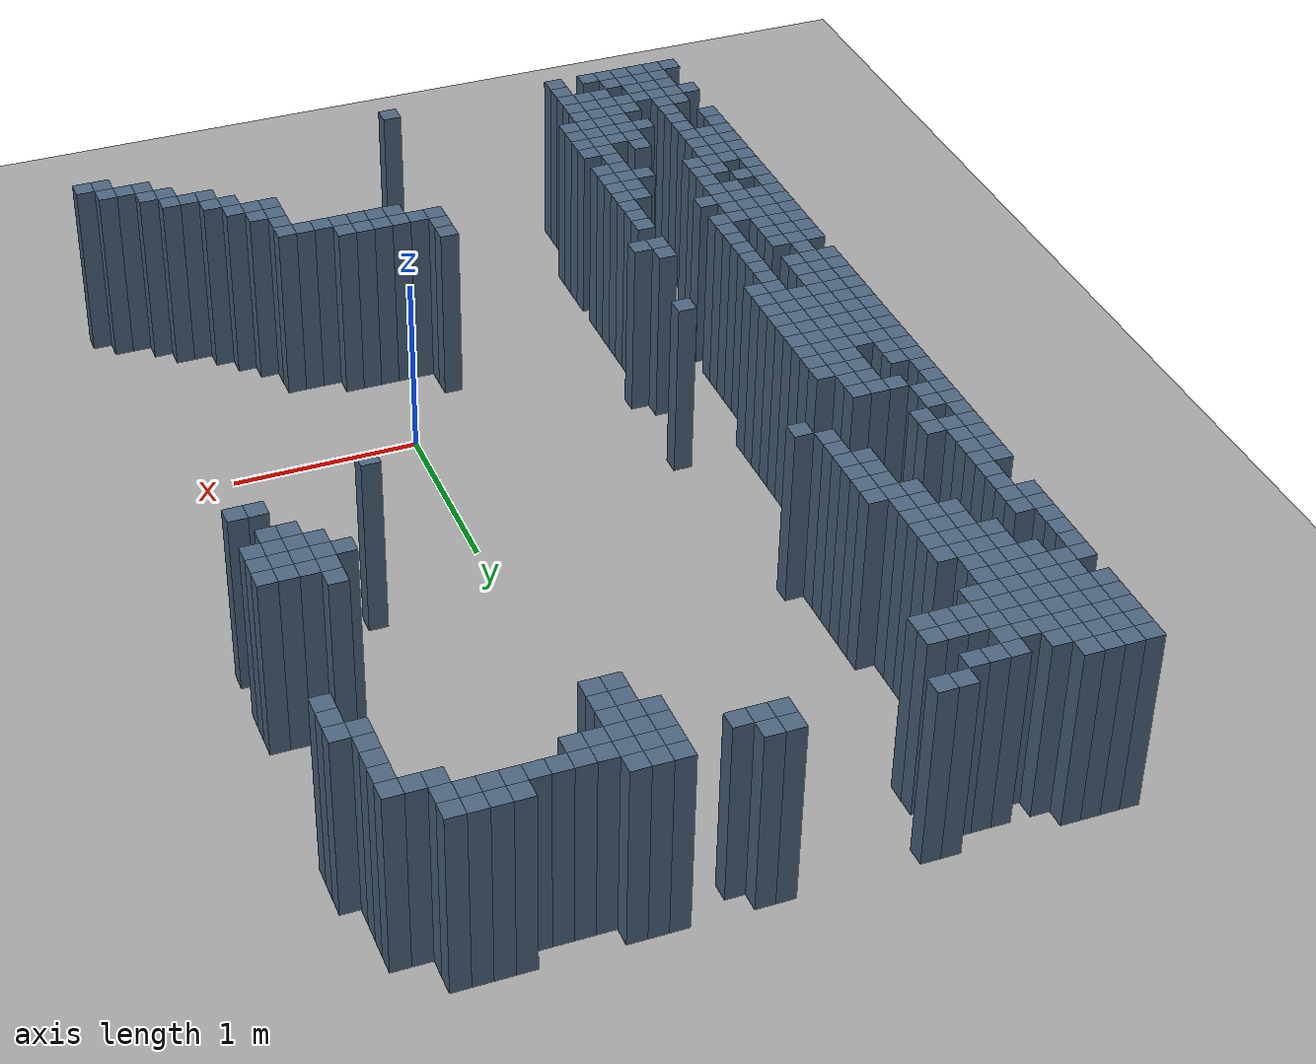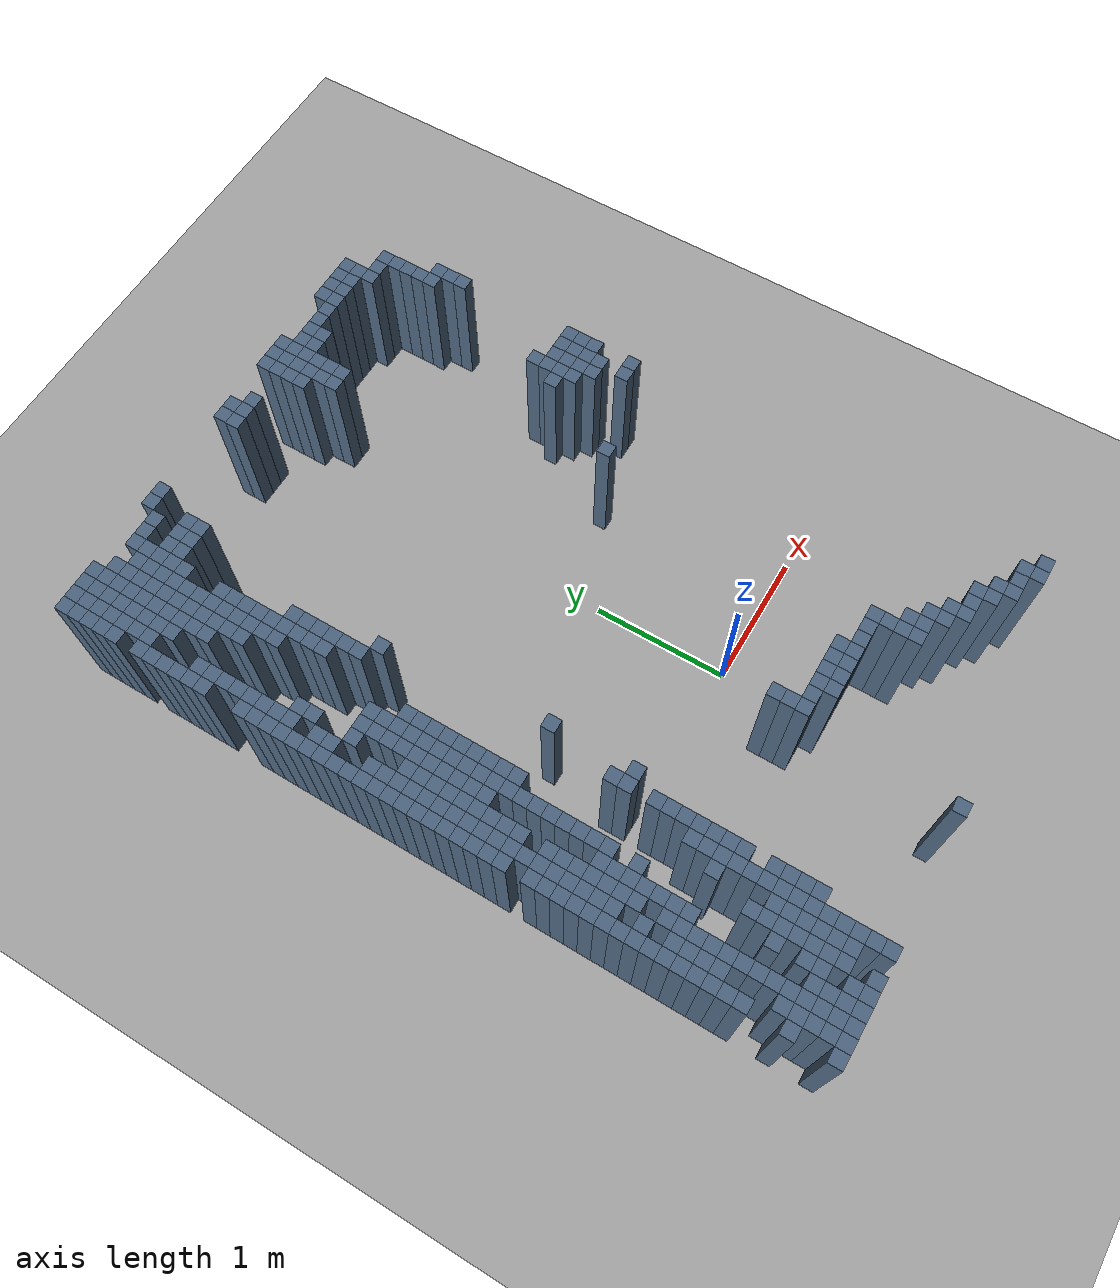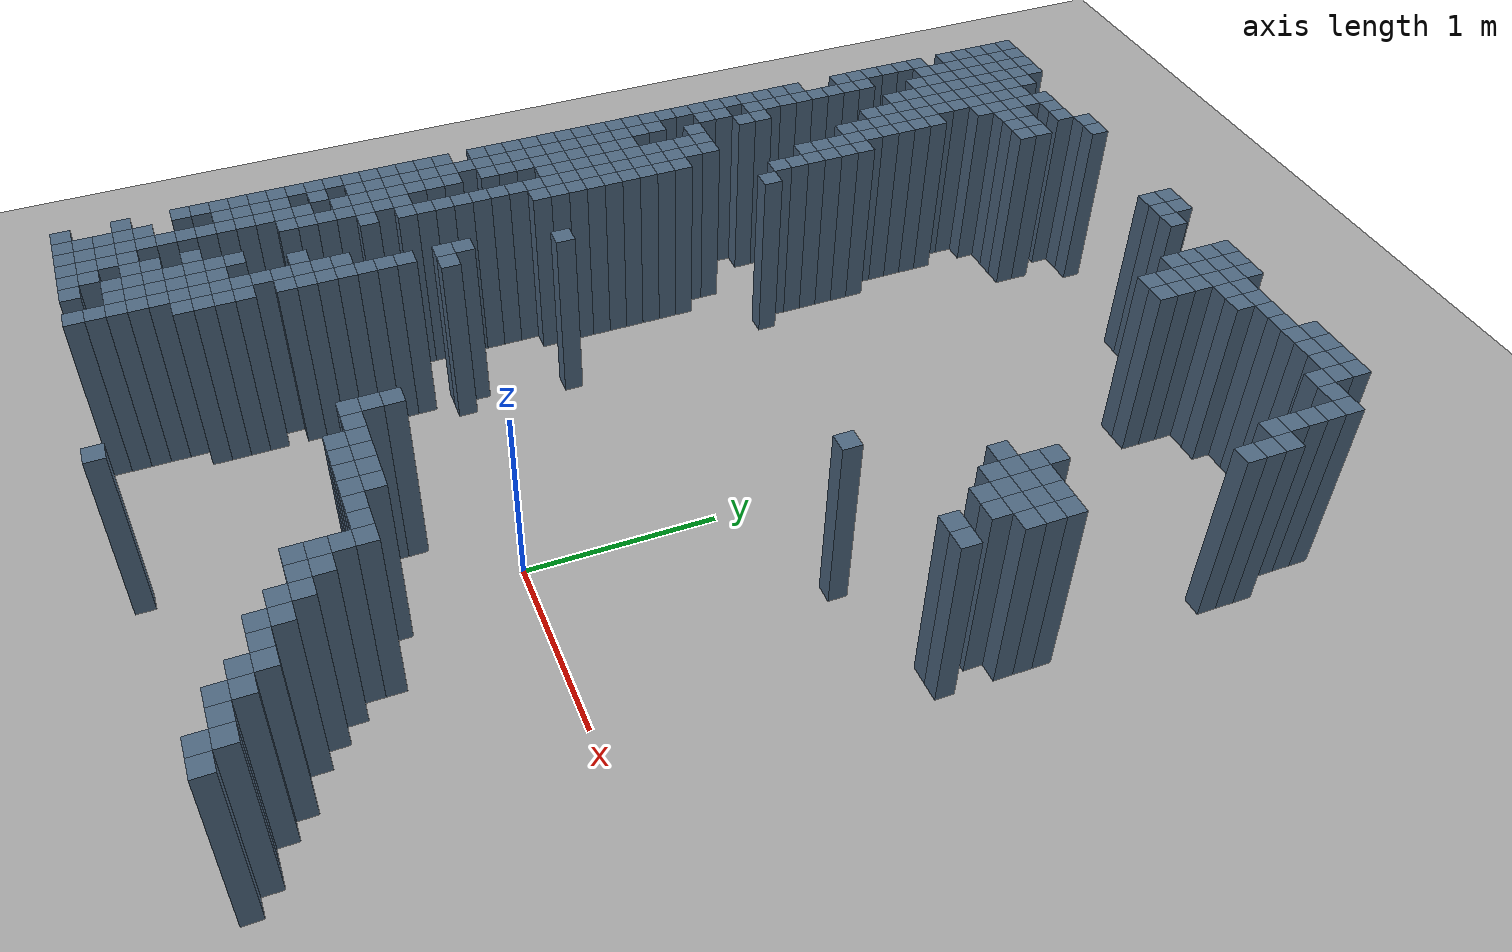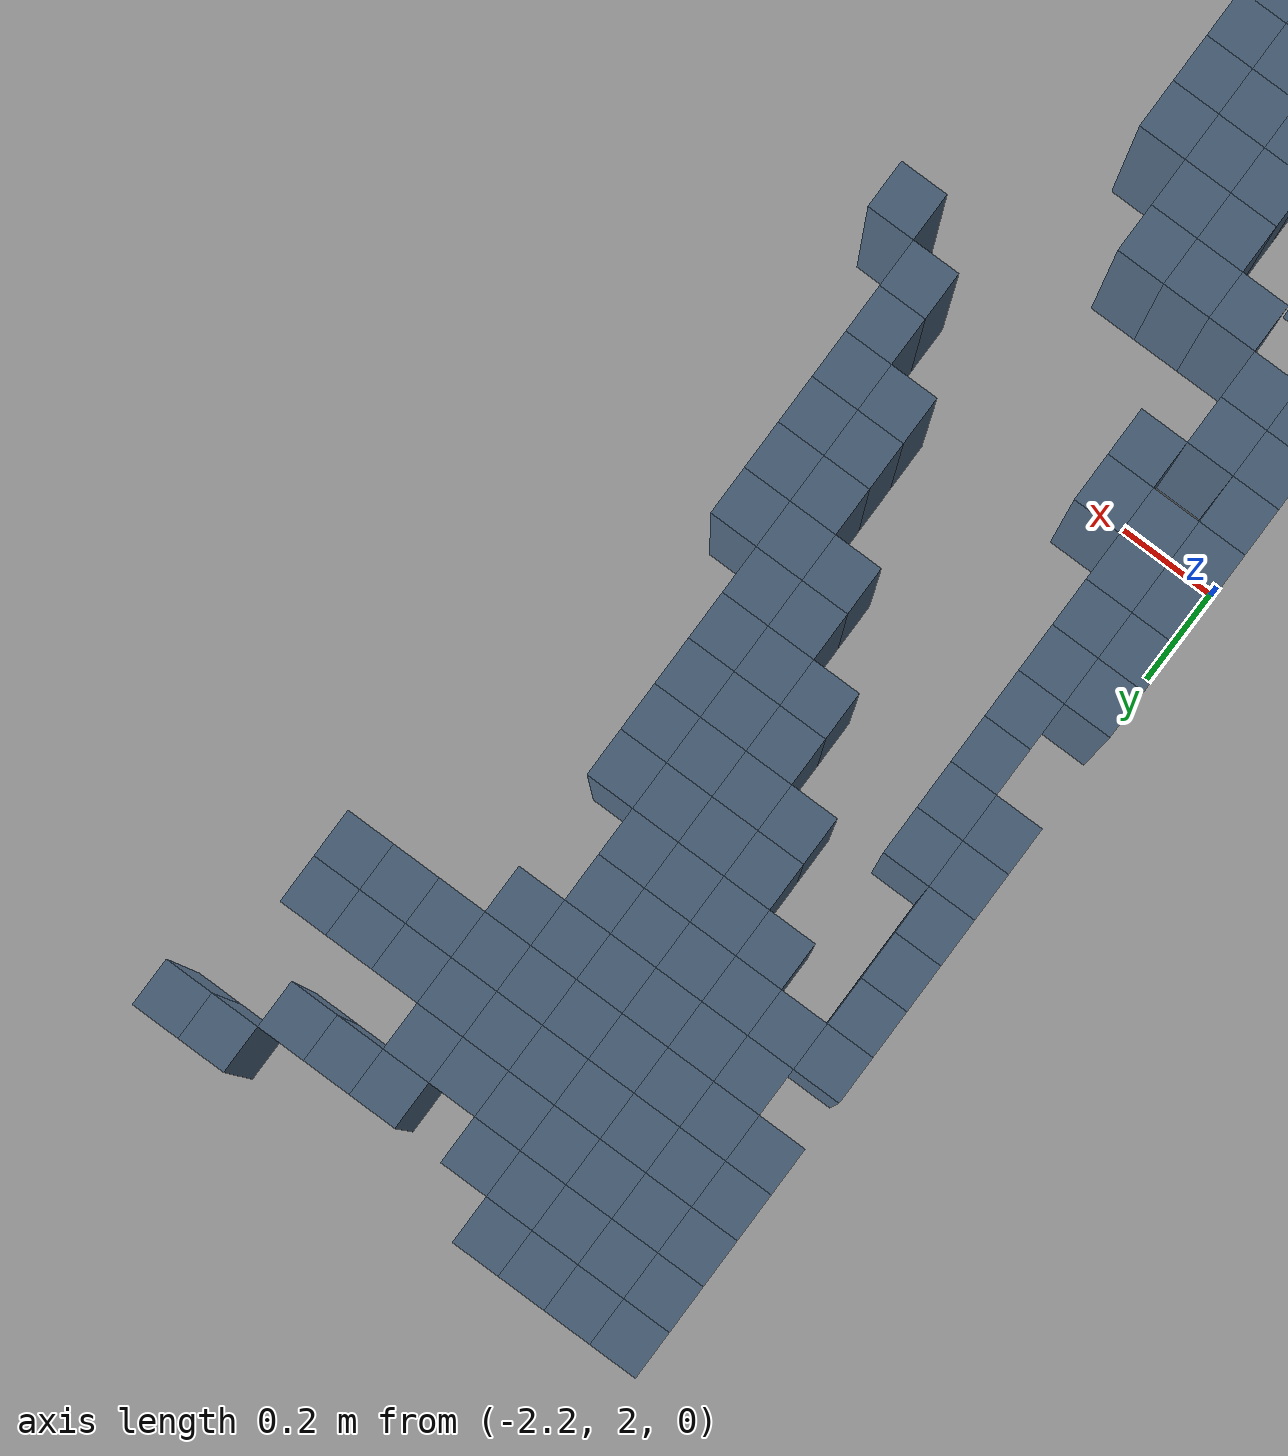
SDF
<?xml version='1.0' encoding='utf-8'?>
<sdf version="1.6">
  <world name="default">
    <gravity>0 0 -9.81</gravity>
    <physics name="default_physics" type="ode">
      <max_step_size>0.001</max_step_size>
      <real_time_update_rate>1000</real_time_update_rate>
    </physics>
    <scene>
      <ambient>0.6 0.6 0.6 1</ambient>
      <shadows>false</shadows>
    </scene>
    <light name="sun" type="directional">
      <pose>0 0 10 0 0 0</pose>
      <diffuse>0.8 0.8 0.8 1</diffuse>
      <direction>-0.5 0.1 -1</direction>
    </light>
    <model name="artificial_flat_ground">
      <static>true</static>
      <link name="ground">
        <collision name="floor_collision">
          <geometry>
            <plane>
              <normal>0 0 1</normal>
              <size>100 100</size>
            </plane>
          </geometry>
        </collision>
        <visual name="floor_visual">
          <geometry>
            <plane>
              <normal>0 0 1</normal>
              <size>100 100</size>
            </plane>
          </geometry>
          <material>
            <ambient>0.65 0.65 0.65 1</ambient>
            <diffuse>0.65 0.65 0.65 1</diffuse>
          </material>
        </visual>
      </link>
    </model>
    <model name="hilti_projected_cells">
      <static>true</static>
      <link name="obstacles">
        <collision name="cell_0_0_collision">
          <pose>-2.15000000 -1.75000000 0.50000000 0 0 0</pose>
          <geometry>
            <box>
              <size>0.10000000 0.10000000 1.00000000</size>
            </box>
          </geometry>
        </collision>
        <visual name="cell_0_0_visual">
          <pose>-2.15000000 -1.75000000 0.50000000 0 0 0</pose>
          <geometry>
            <box>
              <size>0.10000000 0.10000000 1.00000000</size>
            </box>
          </geometry>
          <material>
            <ambient>0.3 0.4 0.5 1</ambient>
            <diffuse>0.3 0.4 0.5 1</diffuse>
          </material>
        </visual>
        <collision name="cell_0_1_collision">
          <pose>-2.05000000 -1.75000000 0.50000000 0 0 0</pose>
          <geometry>
            <box>
              <size>0.10000000 0.10000000 1.00000000</size>
            </box>
          </geometry>
        </collision>
        <visual name="cell_0_1_visual">
          <pose>-2.05000000 -1.75000000 0.50000000 0 0 0</pose>
          <geometry>
            <box>
              <size>0.10000000 0.10000000 1.00000000</size>
            </box>
          </geometry>
          <material>
            <ambient>0.3 0.4 0.5 1</ambient>
            <diffuse>0.3 0.4 0.5 1</diffuse>
          </material>
        </visual>
        <collision name="cell_0_2_collision">
          <pose>-1.95000000 -1.75000000 0.50000000 0 0 0</pose>
          <geometry>
            <box>
              <size>0.10000000 0.10000000 1.00000000</size>
            </box>
          </geometry>
        </collision>
        <visual name="cell_0_2_visual">
          <pose>-1.95000000 -1.75000000 0.50000000 0 0 0</pose>
          <geometry>
            <box>
              <size>0.10000000 0.10000000 1.00000000</size>
            </box>
          </geometry>
          <material>
            <ambient>0.3 0.4 0.5 1</ambient>
            <diffuse>0.3 0.4 0.5 1</diffuse>
          </material>
        </visual>
        <collision name="cell_0_3_collision">
          <pose>-1.85000000 -1.75000000 0.50000000 0 0 0</pose>
          <geometry>
            <box>
              <size>0.10000000 0.10000000 1.00000000</size>
            </box>
          </geometry>
        </collision>
        <visual name="cell_0_3_visual">
          <pose>-1.85000000 -1.75000000 0.50000000 0 0 0</pose>
          <geometry>
            <box>
              <size>0.10000000 0.10000000 1.00000000</size>
            </box>
          </geometry>
          <material>
            <ambient>0.3 0.4 0.5 1</ambient>
            <diffuse>0.3 0.4 0.5 1</diffuse>
          </material>
        </visual>
        <collision name="cell_0_4_collision">
          <pose>-1.75000000 -1.75000000 0.50000000 0 0 0</pose>
          <geometry>
            <box>
              <size>0.10000000 0.10000000 1.00000000</size>
            </box>
          </geometry>
        </collision>
        <visual name="cell_0_4_visual">
          <pose>-1.75000000 -1.75000000 0.50000000 0 0 0</pose>
          <geometry>
            <box>
              <size>0.10000000 0.10000000 1.00000000</size>
            </box>
          </geometry>
          <material>
            <ambient>0.3 0.4 0.5 1</ambient>
            <diffuse>0.3 0.4 0.5 1</diffuse>
          </material>
        </visual>
        <collision name="cell_0_5_collision">
          <pose>-1.65000000 -1.75000000 0.50000000 0 0 0</pose>
          <geometry>
            <box>
              <size>0.10000000 0.10000000 1.00000000</size>
            </box>
          </geometry>
        </collision>
        <visual name="cell_0_5_visual">
          <pose>-1.65000000 -1.75000000 0.50000000 0 0 0</pose>
          <geometry>
            <box>
              <size>0.10000000 0.10000000 1.00000000</size>
            </box>
          </geometry>
          <material>
            <ambient>0.3 0.4 0.5 1</ambient>
            <diffuse>0.3 0.4 0.5 1</diffuse>
          </material>
        </visual>
        <collision name="cell_0_7_collision">
          <pose>-1.45000000 -1.75000000 0.50000000 0 0 0</pose>
          <geometry>
            <box>
              <size>0.10000000 0.10000000 1.00000000</size>
            </box>
          </geometry>
        </collision>
        <visual name="cell_0_7_visual">
          <pose>-1.45000000 -1.75000000 0.50000000 0 0 0</pose>
          <geometry>
            <box>
              <size>0.10000000 0.10000000 1.00000000</size>
            </box>
          </geometry>
          <material>
            <ambient>0.3 0.4 0.5 1</ambient>
            <diffuse>0.3 0.4 0.5 1</diffuse>
          </material>
        </visual>
        <collision name="cell_0_17_collision">
          <pose>-0.45000000 -1.75000000 0.50000000 0 0 0</pose>
          <geometry>
            <box>
              <size>0.10000000 0.10000000 1.00000000</size>
            </box>
          </geometry>
        </collision>
        <visual name="cell_0_17_visual">
          <pose>-0.45000000 -1.75000000 0.50000000 0 0 0</pose>
          <geometry>
            <box>
              <size>0.10000000 0.10000000 1.00000000</size>
            </box>
          </geometry>
          <material>
            <ambient>0.3 0.4 0.5 1</ambient>
            <diffuse>0.3 0.4 0.5 1</diffuse>
          </material>
        </visual>
        <collision name="cell_1_1_collision">
          <pose>-2.05000000 -1.65000000 0.50000000 0 0 0</pose>
          <geometry>
            <box>
              <size>0.10000000 0.10000000 1.00000000</size>
            </box>
          </geometry>
        </collision>
        <visual name="cell_1_1_visual">
          <pose>-2.05000000 -1.65000000 0.50000000 0 0 0</pose>
          <geometry>
            <box>
              <size>0.10000000 0.10000000 1.00000000</size>
            </box>
          </geometry>
          <material>
            <ambient>0.3 0.4 0.5 1</ambient>
            <diffuse>0.3 0.4 0.5 1</diffuse>
          </material>
        </visual>
        <collision name="cell_1_2_collision">
          <pose>-1.95000000 -1.65000000 0.50000000 0 0 0</pose>
          <geometry>
            <box>
              <size>0.10000000 0.10000000 1.00000000</size>
            </box>
          </geometry>
        </collision>
        <visual name="cell_1_2_visual">
          <pose>-1.95000000 -1.65000000 0.50000000 0 0 0</pose>
          <geometry>
            <box>
              <size>0.10000000 0.10000000 1.00000000</size>
            </box>
          </geometry>
          <material>
            <ambient>0.3 0.4 0.5 1</ambient>
            <diffuse>0.3 0.4 0.5 1</diffuse>
          </material>
        </visual>
        <collision name="cell_1_3_collision">
          <pose>-1.85000000 -1.65000000 0.50000000 0 0 0</pose>
          <geometry>
            <box>
              <size>0.10000000 0.10000000 1.00000000</size>
            </box>
          </geometry>
        </collision>
        <visual name="cell_1_3_visual">
          <pose>-1.85000000 -1.65000000 0.50000000 0 0 0</pose>
          <geometry>
            <box>
              <size>0.10000000 0.10000000 1.00000000</size>
            </box>
          </geometry>
          <material>
            <ambient>0.3 0.4 0.5 1</ambient>
            <diffuse>0.3 0.4 0.5 1</diffuse>
          </material>
        </visual>
        <collision name="cell_1_4_collision">
          <pose>-1.75000000 -1.65000000 0.50000000 0 0 0</pose>
          <geometry>
            <box>
              <size>0.10000000 0.10000000 1.00000000</size>
            </box>
          </geometry>
        </collision>
        <visual name="cell_1_4_visual">
          <pose>-1.75000000 -1.65000000 0.50000000 0 0 0</pose>
          <geometry>
            <box>
              <size>0.10000000 0.10000000 1.00000000</size>
            </box>
          </geometry>
          <material>
            <ambient>0.3 0.4 0.5 1</ambient>
            <diffuse>0.3 0.4 0.5 1</diffuse>
          </material>
        </visual>
        <collision name="cell_1_7_collision">
          <pose>-1.45000000 -1.65000000 0.50000000 0 0 0</pose>
          <geometry>
            <box>
              <size>0.10000000 0.10000000 1.00000000</size>
            </box>
          </geometry>
        </collision>
        <visual name="cell_1_7_visual">
          <pose>-1.45000000 -1.65000000 0.50000000 0 0 0</pose>
          <geometry>
            <box>
              <size>0.10000000 0.10000000 1.00000000</size>
            </box>
          </geometry>
          <material>
            <ambient>0.3 0.4 0.5 1</ambient>
            <diffuse>0.3 0.4 0.5 1</diffuse>
          </material>
        </visual>
        <collision name="cell_2_1_collision">
          <pose>-2.05000000 -1.55000000 0.50000000 0 0 0</pose>
          <geometry>
            <box>
              <size>0.10000000 0.10000000 1.00000000</size>
            </box>
          </geometry>
        </collision>
        <visual name="cell_2_1_visual">
          <pose>-2.05000000 -1.55000000 0.50000000 0 0 0</pose>
          <geometry>
            <box>
              <size>0.10000000 0.10000000 1.00000000</size>
            </box>
          </geometry>
          <material>
            <ambient>0.3 0.4 0.5 1</ambient>
            <diffuse>0.3 0.4 0.5 1</diffuse>
          </material>
        </visual>
        <collision name="cell_2_2_collision">
          <pose>-1.95000000 -1.55000000 0.50000000 0 0 0</pose>
          <geometry>
            <box>
              <size>0.10000000 0.10000000 1.00000000</size>
            </box>
          </geometry>
        </collision>
        <visual name="cell_2_2_visual">
          <pose>-1.95000000 -1.55000000 0.50000000 0 0 0</pose>
          <geometry>
            <box>
              <size>0.10000000 0.10000000 1.00000000</size>
            </box>
          </geometry>
          <material>
            <ambient>0.3 0.4 0.5 1</ambient>
            <diffuse>0.3 0.4 0.5 1</diffuse>
          </material>
        </visual>
        <collision name="cell_2_3_collision">
          <pose>-1.85000000 -1.55000000 0.50000000 0 0 0</pose>
          <geometry>
            <box>
              <size>0.10000000 0.10000000 1.00000000</size>
            </box>
          </geometry>
        </collision>
        <visual name="cell_2_3_visual">
          <pose>-1.85000000 -1.55000000 0.50000000 0 0 0</pose>
          <geometry>
            <box>
              <size>0.10000000 0.10000000 1.00000000</size>
            </box>
          </geometry>
          <material>
            <ambient>0.3 0.4 0.5 1</ambient>
            <diffuse>0.3 0.4 0.5 1</diffuse>
          </material>
        </visual>
        <collision name="cell_2_5_collision">
          <pose>-1.65000000 -1.55000000 0.50000000 0 0 0</pose>
          <geometry>
            <box>
              <size>0.10000000 0.10000000 1.00000000</size>
            </box>
          </geometry>
        </collision>
        <visual name="cell_2_5_visual">
          <pose>-1.65000000 -1.55000000 0.50000000 0 0 0</pose>
          <geometry>
            <box>
              <size>0.10000000 0.10000000 1.00000000</size>
            </box>
          </geometry>
          <material>
            <ambient>0.3 0.4 0.5 1</ambient>
            <diffuse>0.3 0.4 0.5 1</diffuse>
          </material>
        </visual>
        <collision name="cell_2_6_collision">
          <pose>-1.55000000 -1.55000000 0.50000000 0 0 0</pose>
          <geometry>
            <box>
              <size>0.10000000 0.10000000 1.00000000</size>
            </box>
          </geometry>
        </collision>
        <visual name="cell_2_6_visual">
          <pose>-1.55000000 -1.55000000 0.50000000 0 0 0</pose>
          <geometry>
            <box>
              <size>0.10000000 0.10000000 1.00000000</size>
            </box>
          </geometry>
          <material>
            <ambient>0.3 0.4 0.5 1</ambient>
            <diffuse>0.3 0.4 0.5 1</diffuse>
          </material>
        </visual>
        <collision name="cell_2_7_collision">
          <pose>-1.45000000 -1.55000000 0.50000000 0 0 0</pose>
          <geometry>
            <box>
              <size>0.10000000 0.10000000 1.00000000</size>
            </box>
          </geometry>
        </collision>
        <visual name="cell_2_7_visual">
          <pose>-1.45000000 -1.55000000 0.50000000 0 0 0</pose>
          <geometry>
            <box>
              <size>0.10000000 0.10000000 1.00000000</size>
            </box>
          </geometry>
          <material>
            <ambient>0.3 0.4 0.5 1</ambient>
            <diffuse>0.3 0.4 0.5 1</diffuse>
          </material>
        </visual>
        <collision name="cell_2_34_collision">
          <pose>1.25000000 -1.55000000 0.50000000 0 0 0</pose>
          <geometry>
            <box>
              <size>0.10000000 0.10000000 1.00000000</size>
            </box>
          </geometry>
        </collision>
        <visual name="cell_2_34_visual">
          <pose>1.25000000 -1.55000000 0.50000000 0 0 0</pose>
          <geometry>
            <box>
              <size>0.10000000 0.10000000 1.00000000</size>
            </box>
          </geometry>
          <material>
            <ambient>0.3 0.4 0.5 1</ambient>
            <diffuse>0.3 0.4 0.5 1</diffuse>
          </material>
        </visual>
        <collision name="cell_2_35_collision">
          <pose>1.35000000 -1.55000000 0.50000000 0 0 0</pose>
          <geometry>
            <box>
              <size>0.10000000 0.10000000 1.00000000</size>
            </box>
          </geometry>
        </collision>
        <visual name="cell_2_35_visual">
          <pose>1.35000000 -1.55000000 0.50000000 0 0 0</pose>
          <geometry>
            <box>
              <size>0.10000000 0.10000000 1.00000000</size>
            </box>
          </geometry>
          <material>
            <ambient>0.3 0.4 0.5 1</ambient>
            <diffuse>0.3 0.4 0.5 1</diffuse>
          </material>
        </visual>
        <collision name="cell_3_0_collision">
          <pose>-2.15000000 -1.45000000 0.50000000 0 0 0</pose>
          <geometry>
            <box>
              <size>0.10000000 0.10000000 1.00000000</size>
            </box>
          </geometry>
        </collision>
        <visual name="cell_3_0_visual">
          <pose>-2.15000000 -1.45000000 0.50000000 0 0 0</pose>
          <geometry>
            <box>
              <size>0.10000000 0.10000000 1.00000000</size>
            </box>
          </geometry>
          <material>
            <ambient>0.3 0.4 0.5 1</ambient>
            <diffuse>0.3 0.4 0.5 1</diffuse>
          </material>
        </visual>
        <collision name="cell_3_1_collision">
          <pose>-2.05000000 -1.45000000 0.50000000 0 0 0</pose>
          <geometry>
            <box>
              <size>0.10000000 0.10000000 1.00000000</size>
            </box>
          </geometry>
        </collision>
        <visual name="cell_3_1_visual">
          <pose>-2.05000000 -1.45000000 0.50000000 0 0 0</pose>
          <geometry>
            <box>
              <size>0.10000000 0.10000000 1.00000000</size>
            </box>
          </geometry>
          <material>
            <ambient>0.3 0.4 0.5 1</ambient>
            <diffuse>0.3 0.4 0.5 1</diffuse>
          </material>
        </visual>
        <collision name="cell_3_2_collision">
          <pose>-1.95000000 -1.45000000 0.50000000 0 0 0</pose>
          <geometry>
            <box>
              <size>0.10000000 0.10000000 1.00000000</size>
            </box>
          </geometry>
        </collision>
        <visual name="cell_3_2_visual">
          <pose>-1.95000000 -1.45000000 0.50000000 0 0 0</pose>
          <geometry>
            <box>
              <size>0.10000000 0.10000000 1.00000000</size>
            </box>
          </geometry>
          <material>
            <ambient>0.3 0.4 0.5 1</ambient>
            <diffuse>0.3 0.4 0.5 1</diffuse>
          </material>
        </visual>
        <collision name="cell_3_3_collision">
          <pose>-1.85000000 -1.45000000 0.50000000 0 0 0</pose>
          <geometry>
            <box>
              <size>0.10000000 0.10000000 1.00000000</size>
            </box>
          </geometry>
        </collision>
        <visual name="cell_3_3_visual">
          <pose>-1.85000000 -1.45000000 0.50000000 0 0 0</pose>
          <geometry>
            <box>
              <size>0.10000000 0.10000000 1.00000000</size>
            </box>
          </geometry>
          <material>
            <ambient>0.3 0.4 0.5 1</ambient>
            <diffuse>0.3 0.4 0.5 1</diffuse>
          </material>
        </visual>
        <collision name="cell_3_4_collision">
          <pose>-1.75000000 -1.45000000 0.50000000 0 0 0</pose>
          <geometry>
            <box>
              <size>0.10000000 0.10000000 1.00000000</size>
            </box>
          </geometry>
        </collision>
        <visual name="cell_3_4_visual">
          <pose>-1.75000000 -1.45000000 0.50000000 0 0 0</pose>
          <geometry>
            <box>
              <size>0.10000000 0.10000000 1.00000000</size>
            </box>
          </geometry>
          <material>
            <ambient>0.3 0.4 0.5 1</ambient>
            <diffuse>0.3 0.4 0.5 1</diffuse>
          </material>
        </visual>
        <collision name="cell_3_5_collision">
          <pose>-1.65000000 -1.45000000 0.50000000 0 0 0</pose>
          <geometry>
            <box>
              <size>0.10000000 0.10000000 1.00000000</size>
            </box>
          </geometry>
        </collision>
        <visual name="cell_3_5_visual">
          <pose>-1.65000000 -1.45000000 0.50000000 0 0 0</pose>
          <geometry>
            <box>
              <size>0.10000000 0.10000000 1.00000000</size>
            </box>
          </geometry>
          <material>
            <ambient>0.3 0.4 0.5 1</ambient>
            <diffuse>0.3 0.4 0.5 1</diffuse>
          </material>
        </visual>
        <collision name="cell_3_6_collision">
          <pose>-1.55000000 -1.45000000 0.50000000 0 0 0</pose>
          <geometry>
            <box>
              <size>0.10000000 0.10000000 1.00000000</size>
            </box>
          </geometry>
        </collision>
        <visual name="cell_3_6_visual">
          <pose>-1.55000000 -1.45000000 0.50000000 0 0 0</pose>
          <geometry>
            <box>
              <size>0.10000000 0.10000000 1.00000000</size>
            </box>
          </geometry>
          <material>
            <ambient>0.3 0.4 0.5 1</ambient>
            <diffuse>0.3 0.4 0.5 1</diffuse>
          </material>
        </visual>
        <collision name="cell_3_7_collision">
          <pose>-1.45000000 -1.45000000 0.50000000 0 0 0</pose>
          <geometry>
            <box>
              <size>0.10000000 0.10000000 1.00000000</size>
            </box>
          </geometry>
        </collision>
        <visual name="cell_3_7_visual">
          <pose>-1.45000000 -1.45000000 0.50000000 0 0 0</pose>
          <geometry>
            <box>
              <size>0.10000000 0.10000000 1.00000000</size>
            </box>
          </geometry>
          <material>
            <ambient>0.3 0.4 0.5 1</ambient>
            <diffuse>0.3 0.4 0.5 1</diffuse>
          </material>
        </visual>
        <collision name="cell_3_32_collision">
          <pose>1.05000000 -1.45000000 0.50000000 0 0 0</pose>
          <geometry>
            <box>
              <size>0.10000000 0.10000000 1.00000000</size>
            </box>
          </geometry>
        </collision>
        <visual name="cell_3_32_visual">
          <pose>1.05000000 -1.45000000 0.50000000 0 0 0</pose>
          <geometry>
            <box>
              <size>0.10000000 0.10000000 1.00000000</size>
            </box>
          </geometry>
          <material>
            <ambient>0.3 0.4 0.5 1</ambient>
            <diffuse>0.3 0.4 0.5 1</diffuse>
          </material>
        </visual>
        <collision name="cell_3_33_collision">
          <pose>1.15000000 -1.45000000 0.50000000 0 0 0</pose>
          <geometry>
            <box>
              <size>0.10000000 0.10000000 1.00000000</size>
            </box>
          </geometry>
        </collision>
        <visual name="cell_3_33_visual">
          <pose>1.15000000 -1.45000000 0.50000000 0 0 0</pose>
          <geometry>
            <box>
              <size>0.10000000 0.10000000 1.00000000</size>
            </box>
          </geometry>
          <material>
            <ambient>0.3 0.4 0.5 1</ambient>
            <diffuse>0.3 0.4 0.5 1</diffuse>
          </material>
        </visual>
        <collision name="cell_3_34_collision">
          <pose>1.25000000 -1.45000000 0.50000000 0 0 0</pose>
          <geometry>
            <box>
              <size>0.10000000 0.10000000 1.00000000</size>
            </box>
          </geometry>
        </collision>
        <visual name="cell_3_34_visual">
          <pose>1.25000000 -1.45000000 0.50000000 0 0 0</pose>
          <geometry>
            <box>
              <size>0.10000000 0.10000000 1.00000000</size>
            </box>
          </geometry>
          <material>
            <ambient>0.3 0.4 0.5 1</ambient>
            <diffuse>0.3 0.4 0.5 1</diffuse>
          </material>
        </visual>
        <collision name="cell_4_1_collision">
          <pose>-2.05000000 -1.35000000 0.50000000 0 0 0</pose>
          <geometry>
            <box>
              <size>0.10000000 0.10000000 1.00000000</size>
            </box>
          </geometry>
        </collision>
        <visual name="cell_4_1_visual">
          <pose>-2.05000000 -1.35000000 0.50000000 0 0 0</pose>
          <geometry>
            <box>
              <size>0.10000000 0.10000000 1.00000000</size>
            </box>
          </geometry>
          <material>
            <ambient>0.3 0.4 0.5 1</ambient>
            <diffuse>0.3 0.4 0.5 1</diffuse>
          </material>
        </visual>
        <collision name="cell_4_2_collision">
          <pose>-1.95000000 -1.35000000 0.50000000 0 0 0</pose>
          <geometry>
            <box>
              <size>0.10000000 0.10000000 1.00000000</size>
            </box>
          </geometry>
        </collision>
        <visual name="cell_4_2_visual">
          <pose>-1.95000000 -1.35000000 0.50000000 0 0 0</pose>
          <geometry>
            <box>
              <size>0.10000000 0.10000000 1.00000000</size>
            </box>
          </geometry>
          <material>
            <ambient>0.3 0.4 0.5 1</ambient>
            <diffuse>0.3 0.4 0.5 1</diffuse>
          </material>
        </visual>
        <collision name="cell_4_4_collision">
          <pose>-1.75000000 -1.35000000 0.50000000 0 0 0</pose>
          <geometry>
            <box>
              <size>0.10000000 0.10000000 1.00000000</size>
            </box>
          </geometry>
        </collision>
        <visual name="cell_4_4_visual">
          <pose>-1.75000000 -1.35000000 0.50000000 0 0 0</pose>
          <geometry>
            <box>
              <size>0.10000000 0.10000000 1.00000000</size>
            </box>
          </geometry>
          <material>
            <ambient>0.3 0.4 0.5 1</ambient>
            <diffuse>0.3 0.4 0.5 1</diffuse>
          </material>
        </visual>
        <collision name="cell_4_5_collision">
          <pose>-1.65000000 -1.35000000 0.50000000 0 0 0</pose>
          <geometry>
            <box>
              <size>0.10000000 0.10000000 1.00000000</size>
            </box>
          </geometry>
        </collision>
        <visual name="cell_4_5_visual">
          <pose>-1.65000000 -1.35000000 0.50000000 0 0 0</pose>
          <geometry>
            <box>
              <size>0.10000000 0.10000000 1.00000000</size>
            </box>
          </geometry>
          <material>
            <ambient>0.3 0.4 0.5 1</ambient>
            <diffuse>0.3 0.4 0.5 1</diffuse>
          </material>
        </visual>
        <collision name="cell_4_6_collision">
          <pose>-1.55000000 -1.35000000 0.50000000 0 0 0</pose>
          <geometry>
            <box>
              <size>0.10000000 0.10000000 1.00000000</size>
            </box>
          </geometry>
        </collision>
        <visual name="cell_4_6_visual">
          <pose>-1.55000000 -1.35000000 0.50000000 0 0 0</pose>
          <geometry>
            <box>
              <size>0.10000000 0.10000000 1.00000000</size>
            </box>
          </geometry>
          <material>
            <ambient>0.3 0.4 0.5 1</ambient>
            <diffuse>0.3 0.4 0.5 1</diffuse>
          </material>
        </visual>
        <collision name="cell_4_7_collision">
          <pose>-1.45000000 -1.35000000 0.50000000 0 0 0</pose>
          <geometry>
            <box>
              <size>0.10000000 0.10000000 1.00000000</size>
            </box>
          </geometry>
        </collision>
        <visual name="cell_4_7_visual">
          <pose>-1.45000000 -1.35000000 0.50000000 0 0 0</pose>
          <geometry>
            <box>
              <size>0.10000000 0.10000000 1.00000000</size>
            </box>
          </geometry>
          <material>
            <ambient>0.3 0.4 0.5 1</ambient>
            <diffuse>0.3 0.4 0.5 1</diffuse>
          </material>
        </visual>
        <collision name="cell_4_31_collision">
          <pose>0.95000000 -1.35000000 0.50000000 0 0 0</pose>
          <geometry>
            <box>
              <size>0.10000000 0.10000000 1.00000000</size>
            </box>
          </geometry>
        </collision>
        <visual name="cell_4_31_visual">
          <pose>0.95000000 -1.35000000 0.50000000 0 0 0</pose>
          <geometry>
            <box>
              <size>0.10000000 0.10000000 1.00000000</size>
            </box>
          </geometry>
          <material>
            <ambient>0.3 0.4 0.5 1</ambient>
            <diffuse>0.3 0.4 0.5 1</diffuse>
          </material>
        </visual>
        <collision name="cell_4_32_collision">
          <pose>1.05000000 -1.35000000 0.50000000 0 0 0</pose>
          <geometry>
            <box>
              <size>0.10000000 0.10000000 1.00000000</size>
            </box>
          </geometry>
        </collision>
        <visual name="cell_4_32_visual">
          <pose>1.05000000 -1.35000000 0.50000000 0 0 0</pose>
          <geometry>
            <box>
              <size>0.10000000 0.10000000 1.00000000</size>
            </box>
          </geometry>
          <material>
            <ambient>0.3 0.4 0.5 1</ambient>
            <diffuse>0.3 0.4 0.5 1</diffuse>
          </material>
        </visual>
        <collision name="cell_5_2_collision">
          <pose>-1.95000000 -1.25000000 0.50000000 0 0 0</pose>
          <geometry>
            <box>
              <size>0.10000000 0.10000000 1.00000000</size>
            </box>
          </geometry>
        </collision>
        <visual name="cell_5_2_visual">
          <pose>-1.95000000 -1.25000000 0.50000000 0 0 0</pose>
          <geometry>
            <box>
              <size>0.10000000 0.10000000 1.00000000</size>
            </box>
          </geometry>
          <material>
            <ambient>0.3 0.4 0.5 1</ambient>
            <diffuse>0.3 0.4 0.5 1</diffuse>
          </material>
        </visual>
        <collision name="cell_5_5_collision">
          <pose>-1.65000000 -1.25000000 0.50000000 0 0 0</pose>
          <geometry>
            <box>
              <size>0.10000000 0.10000000 1.00000000</size>
            </box>
          </geometry>
        </collision>
        <visual name="cell_5_5_visual">
          <pose>-1.65000000 -1.25000000 0.50000000 0 0 0</pose>
          <geometry>
            <box>
              <size>0.10000000 0.10000000 1.00000000</size>
            </box>
          </geometry>
          <material>
            <ambient>0.3 0.4 0.5 1</ambient>
            <diffuse>0.3 0.4 0.5 1</diffuse>
          </material>
        </visual>
        <collision name="cell_5_6_collision">
          <pose>-1.55000000 -1.25000000 0.50000000 0 0 0</pose>
          <geometry>
            <box>
              <size>0.10000000 0.10000000 1.00000000</size>
            </box>
          </geometry>
        </collision>
        <visual name="cell_5_6_visual">
          <pose>-1.55000000 -1.25000000 0.50000000 0 0 0</pose>
          <geometry>
            <box>
              <size>0.10000000 0.10000000 1.00000000</size>
            </box>
          </geometry>
          <material>
            <ambient>0.3 0.4 0.5 1</ambient>
            <diffuse>0.3 0.4 0.5 1</diffuse>
          </material>
        </visual>
        <collision name="cell_5_7_collision">
          <pose>-1.45000000 -1.25000000 0.50000000 0 0 0</pose>
          <geometry>
            <box>
              <size>0.10000000 0.10000000 1.00000000</size>
            </box>
          </geometry>
        </collision>
        <visual name="cell_5_7_visual">
          <pose>-1.45000000 -1.25000000 0.50000000 0 0 0</pose>
          <geometry>
            <box>
              <size>0.10000000 0.10000000 1.00000000</size>
            </box>
          </geometry>
          <material>
            <ambient>0.3 0.4 0.5 1</ambient>
            <diffuse>0.3 0.4 0.5 1</diffuse>
          </material>
        </visual>
        <collision name="cell_5_8_collision">
          <pose>-1.35000000 -1.25000000 0.50000000 0 0 0</pose>
          <geometry>
            <box>
              <size>0.10000000 0.10000000 1.00000000</size>
            </box>
          </geometry>
        </collision>
        <visual name="cell_5_8_visual">
          <pose>-1.35000000 -1.25000000 0.50000000 0 0 0</pose>
          <geometry>
            <box>
              <size>0.10000000 0.10000000 1.00000000</size>
            </box>
          </geometry>
          <material>
            <ambient>0.3 0.4 0.5 1</ambient>
            <diffuse>0.3 0.4 0.5 1</diffuse>
          </material>
        </visual>
        <collision name="cell_5_29_collision">
          <pose>0.75000000 -1.25000000 0.50000000 0 0 0</pose>
          <geometry>
            <box>
              <size>0.10000000 0.10000000 1.00000000</size>
            </box>
          </geometry>
        </collision>
        <visual name="cell_5_29_visual">
          <pose>0.75000000 -1.25000000 0.50000000 0 0 0</pose>
          <geometry>
            <box>
              <size>0.10000000 0.10000000 1.00000000</size>
            </box>
          </geometry>
          <material>
            <ambient>0.3 0.4 0.5 1</ambient>
            <diffuse>0.3 0.4 0.5 1</diffuse>
          </material>
        </visual>
        <collision name="cell_5_30_collision">
          <pose>0.85000000 -1.25000000 0.50000000 0 0 0</pose>
          <geometry>
            <box>
              <size>0.10000000 0.10000000 1.00000000</size>
            </box>
          </geometry>
        </collision>
        <visual name="cell_5_30_visual">
          <pose>0.85000000 -1.25000000 0.50000000 0 0 0</pose>
          <geometry>
            <box>
              <size>0.10000000 0.10000000 1.00000000</size>
            </box>
          </geometry>
          <material>
            <ambient>0.3 0.4 0.5 1</ambient>
            <diffuse>0.3 0.4 0.5 1</diffuse>
          </material>
        </visual>
        <collision name="cell_5_31_collision">
          <pose>0.95000000 -1.25000000 0.50000000 0 0 0</pose>
          <geometry>
            <box>
              <size>0.10000000 0.10000000 1.00000000</size>
            </box>
          </geometry>
        </collision>
        <visual name="cell_5_31_visual">
          <pose>0.95000000 -1.25000000 0.50000000 0 0 0</pose>
          <geometry>
            <box>
              <size>0.10000000 0.10000000 1.00000000</size>
            </box>
          </geometry>
          <material>
            <ambient>0.3 0.4 0.5 1</ambient>
            <diffuse>0.3 0.4 0.5 1</diffuse>
          </material>
        </visual>
        <collision name="cell_6_0_collision">
          <pose>-2.15000000 -1.15000000 0.50000000 0 0 0</pose>
          <geometry>
            <box>
              <size>0.10000000 0.10000000 1.00000000</size>
            </box>
          </geometry>
        </collision>
        <visual name="cell_6_0_visual">
          <pose>-2.15000000 -1.15000000 0.50000000 0 0 0</pose>
          <geometry>
            <box>
              <size>0.10000000 0.10000000 1.00000000</size>
            </box>
          </geometry>
          <material>
            <ambient>0.3 0.4 0.5 1</ambient>
            <diffuse>0.3 0.4 0.5 1</diffuse>
          </material>
        </visual>
        <collision name="cell_6_2_collision">
          <pose>-1.95000000 -1.15000000 0.50000000 0 0 0</pose>
          <geometry>
            <box>
              <size>0.10000000 0.10000000 1.00000000</size>
            </box>
          </geometry>
        </collision>
        <visual name="cell_6_2_visual">
          <pose>-1.95000000 -1.15000000 0.50000000 0 0 0</pose>
          <geometry>
            <box>
              <size>0.10000000 0.10000000 1.00000000</size>
            </box>
          </geometry>
          <material>
            <ambient>0.3 0.4 0.5 1</ambient>
            <diffuse>0.3 0.4 0.5 1</diffuse>
          </material>
        </visual>
        <collision name="cell_6_4_collision">
          <pose>-1.75000000 -1.15000000 0.50000000 0 0 0</pose>
          <geometry>
            <box>
              <size>0.10000000 0.10000000 1.00000000</size>
            </box>
          </geometry>
        </collision>
        <visual name="cell_6_4_visual">
          <pose>-1.75000000 -1.15000000 0.50000000 0 0 0</pose>
          <geometry>
            <box>
              <size>0.10000000 0.10000000 1.00000000</size>
            </box>
          </geometry>
          <material>
            <ambient>0.3 0.4 0.5 1</ambient>
            <diffuse>0.3 0.4 0.5 1</diffuse>
          </material>
        </visual>
        <collision name="cell_6_5_collision">
          <pose>-1.65000000 -1.15000000 0.50000000 0 0 0</pose>
          <geometry>
            <box>
              <size>0.10000000 0.10000000 1.00000000</size>
            </box>
          </geometry>
        </collision>
        <visual name="cell_6_5_visual">
          <pose>-1.65000000 -1.15000000 0.50000000 0 0 0</pose>
          <geometry>
            <box>
              <size>0.10000000 0.10000000 1.00000000</size>
            </box>
          </geometry>
          <material>
            <ambient>0.3 0.4 0.5 1</ambient>
            <diffuse>0.3 0.4 0.5 1</diffuse>
          </material>
        </visual>
        <collision name="cell_6_6_collision">
          <pose>-1.55000000 -1.15000000 0.50000000 0 0 0</pose>
          <geometry>
            <box>
              <size>0.10000000 0.10000000 1.00000000</size>
            </box>
          </geometry>
        </collision>
        <visual name="cell_6_6_visual">
          <pose>-1.55000000 -1.15000000 0.50000000 0 0 0</pose>
          <geometry>
            <box>
              <size>0.10000000 0.10000000 1.00000000</size>
            </box>
          </geometry>
          <material>
            <ambient>0.3 0.4 0.5 1</ambient>
            <diffuse>0.3 0.4 0.5 1</diffuse>
          </material>
        </visual>
        <collision name="cell_6_7_collision">
          <pose>-1.45000000 -1.15000000 0.50000000 0 0 0</pose>
          <geometry>
            <box>
              <size>0.10000000 0.10000000 1.00000000</size>
            </box>
          </geometry>
        </collision>
        <visual name="cell_6_7_visual">
          <pose>-1.45000000 -1.15000000 0.50000000 0 0 0</pose>
          <geometry>
            <box>
              <size>0.10000000 0.10000000 1.00000000</size>
            </box>
          </geometry>
          <material>
            <ambient>0.3 0.4 0.5 1</ambient>
            <diffuse>0.3 0.4 0.5 1</diffuse>
          </material>
        </visual>
        <collision name="cell_6_8_collision">
          <pose>-1.35000000 -1.15000000 0.50000000 0 0 0</pose>
          <geometry>
            <box>
              <size>0.10000000 0.10000000 1.00000000</size>
            </box>
          </geometry>
        </collision>
        <visual name="cell_6_8_visual">
          <pose>-1.35000000 -1.15000000 0.50000000 0 0 0</pose>
          <geometry>
            <box>
              <size>0.10000000 0.10000000 1.00000000</size>
            </box>
          </geometry>
          <material>
            <ambient>0.3 0.4 0.5 1</ambient>
            <diffuse>0.3 0.4 0.5 1</diffuse>
          </material>
        </visual>
        <collision name="cell_6_28_collision">
          <pose>0.65000000 -1.15000000 0.50000000 0 0 0</pose>
          <geometry>
            <box>
              <size>0.10000000 0.10000000 1.00000000</size>
            </box>
          </geometry>
        </collision>
        <visual name="cell_6_28_visual">
          <pose>0.65000000 -1.15000000 0.50000000 0 0 0</pose>
          <geometry>
            <box>
              <size>0.10000000 0.10000000 1.00000000</size>
            </box>
          </geometry>
          <material>
            <ambient>0.3 0.4 0.5 1</ambient>
            <diffuse>0.3 0.4 0.5 1</diffuse>
          </material>
        </visual>
        <collision name="cell_6_29_collision">
          <pose>0.75000000 -1.15000000 0.50000000 0 0 0</pose>
          <geometry>
            <box>
              <size>0.10000000 0.10000000 1.00000000</size>
            </box>
          </geometry>
        </collision>
        <visual name="cell_6_29_visual">
          <pose>0.75000000 -1.15000000 0.50000000 0 0 0</pose>
          <geometry>
            <box>
              <size>0.10000000 0.10000000 1.00000000</size>
            </box>
          </geometry>
          <material>
            <ambient>0.3 0.4 0.5 1</ambient>
            <diffuse>0.3 0.4 0.5 1</diffuse>
          </material>
        </visual>
        <collision name="cell_7_0_collision">
          <pose>-2.15000000 -1.05000000 0.50000000 0 0 0</pose>
          <geometry>
            <box>
              <size>0.10000000 0.10000000 1.00000000</size>
            </box>
          </geometry>
        </collision>
        <visual name="cell_7_0_visual">
          <pose>-2.15000000 -1.05000000 0.50000000 0 0 0</pose>
          <geometry>
            <box>
              <size>0.10000000 0.10000000 1.00000000</size>
            </box>
          </geometry>
          <material>
            <ambient>0.3 0.4 0.5 1</ambient>
            <diffuse>0.3 0.4 0.5 1</diffuse>
          </material>
        </visual>
        <collision name="cell_7_2_collision">
          <pose>-1.95000000 -1.05000000 0.50000000 0 0 0</pose>
          <geometry>
            <box>
              <size>0.10000000 0.10000000 1.00000000</size>
            </box>
          </geometry>
        </collision>
        <visual name="cell_7_2_visual">
          <pose>-1.95000000 -1.05000000 0.50000000 0 0 0</pose>
          <geometry>
            <box>
              <size>0.10000000 0.10000000 1.00000000</size>
            </box>
          </geometry>
          <material>
            <ambient>0.3 0.4 0.5 1</ambient>
            <diffuse>0.3 0.4 0.5 1</diffuse>
          </material>
        </visual>
        <collision name="cell_7_5_collision">
          <pose>-1.65000000 -1.05000000 0.50000000 0 0 0</pose>
          <geometry>
            <box>
              <size>0.10000000 0.10000000 1.00000000</size>
            </box>
          </geometry>
        </collision>
        <visual name="cell_7_5_visual">
          <pose>-1.65000000 -1.05000000 0.50000000 0 0 0</pose>
          <geometry>
            <box>
              <size>0.10000000 0.10000000 1.00000000</size>
            </box>
          </geometry>
          <material>
            <ambient>0.3 0.4 0.5 1</ambient>
            <diffuse>0.3 0.4 0.5 1</diffuse>
          </material>
        </visual>
        <collision name="cell_7_6_collision">
          <pose>-1.55000000 -1.05000000 0.50000000 0 0 0</pose>
          <geometry>
            <box>
              <size>0.10000000 0.10000000 1.00000000</size>
            </box>
          </geometry>
        </collision>
        <visual name="cell_7_6_visual">
          <pose>-1.55000000 -1.05000000 0.50000000 0 0 0</pose>
          <geometry>
            <box>
              <size>0.10000000 0.10000000 1.00000000</size>
            </box>
          </geometry>
          <material>
            <ambient>0.3 0.4 0.5 1</ambient>
            <diffuse>0.3 0.4 0.5 1</diffuse>
          </material>
        </visual>
        <collision name="cell_7_7_collision">
          <pose>-1.45000000 -1.05000000 0.50000000 0 0 0</pose>
          <geometry>
            <box>
              <size>0.10000000 0.10000000 1.00000000</size>
            </box>
          </geometry>
        </collision>
        <visual name="cell_7_7_visual">
          <pose>-1.45000000 -1.05000000 0.50000000 0 0 0</pose>
          <geometry>
            <box>
              <size>0.10000000 0.10000000 1.00000000</size>
            </box>
          </geometry>
          <material>
            <ambient>0.3 0.4 0.5 1</ambient>
            <diffuse>0.3 0.4 0.5 1</diffuse>
          </material>
        </visual>
        <collision name="cell_7_8_collision">
          <pose>-1.35000000 -1.05000000 0.50000000 0 0 0</pose>
          <geometry>
            <box>
              <size>0.10000000 0.10000000 1.00000000</size>
            </box>
          </geometry>
        </collision>
        <visual name="cell_7_8_visual">
          <pose>-1.35000000 -1.05000000 0.50000000 0 0 0</pose>
          <geometry>
            <box>
              <size>0.10000000 0.10000000 1.00000000</size>
            </box>
          </geometry>
          <material>
            <ambient>0.3 0.4 0.5 1</ambient>
            <diffuse>0.3 0.4 0.5 1</diffuse>
          </material>
        </visual>
        <collision name="cell_7_26_collision">
          <pose>0.45000000 -1.05000000 0.50000000 0 0 0</pose>
          <geometry>
            <box>
              <size>0.10000000 0.10000000 1.00000000</size>
            </box>
          </geometry>
        </collision>
        <visual name="cell_7_26_visual">
          <pose>0.45000000 -1.05000000 0.50000000 0 0 0</pose>
          <geometry>
            <box>
              <size>0.10000000 0.10000000 1.00000000</size>
            </box>
          </geometry>
          <material>
            <ambient>0.3 0.4 0.5 1</ambient>
            <diffuse>0.3 0.4 0.5 1</diffuse>
          </material>
        </visual>
        <collision name="cell_7_27_collision">
          <pose>0.55000000 -1.05000000 0.50000000 0 0 0</pose>
          <geometry>
            <box>
              <size>0.10000000 0.10000000 1.00000000</size>
            </box>
          </geometry>
        </collision>
        <visual name="cell_7_27_visual">
          <pose>0.55000000 -1.05000000 0.50000000 0 0 0</pose>
          <geometry>
            <box>
              <size>0.10000000 0.10000000 1.00000000</size>
            </box>
          </geometry>
          <material>
            <ambient>0.3 0.4 0.5 1</ambient>
            <diffuse>0.3 0.4 0.5 1</diffuse>
          </material>
        </visual>
        <collision name="cell_7_28_collision">
          <pose>0.65000000 -1.05000000 0.50000000 0 0 0</pose>
          <geometry>
            <box>
              <size>0.10000000 0.10000000 1.00000000</size>
            </box>
          </geometry>
        </collision>
        <visual name="cell_7_28_visual">
          <pose>0.65000000 -1.05000000 0.50000000 0 0 0</pose>
          <geometry>
            <box>
              <size>0.10000000 0.10000000 1.00000000</size>
            </box>
          </geometry>
          <material>
            <ambient>0.3 0.4 0.5 1</ambient>
            <diffuse>0.3 0.4 0.5 1</diffuse>
          </material>
        </visual>
        <collision name="cell_8_0_collision">
          <pose>-2.15000000 -0.95000000 0.50000000 0 0 0</pose>
          <geometry>
            <box>
              <size>0.10000000 0.10000000 1.00000000</size>
            </box>
          </geometry>
        </collision>
        <visual name="cell_8_0_visual">
          <pose>-2.15000000 -0.95000000 0.50000000 0 0 0</pose>
          <geometry>
            <box>
              <size>0.10000000 0.10000000 1.00000000</size>
            </box>
          </geometry>
          <material>
            <ambient>0.3 0.4 0.5 1</ambient>
            <diffuse>0.3 0.4 0.5 1</diffuse>
          </material>
        </visual>
        <collision name="cell_8_1_collision">
          <pose>-2.05000000 -0.95000000 0.50000000 0 0 0</pose>
          <geometry>
            <box>
              <size>0.10000000 0.10000000 1.00000000</size>
            </box>
          </geometry>
        </collision>
        <visual name="cell_8_1_visual">
          <pose>-2.05000000 -0.95000000 0.50000000 0 0 0</pose>
          <geometry>
            <box>
              <size>0.10000000 0.10000000 1.00000000</size>
            </box>
          </geometry>
          <material>
            <ambient>0.3 0.4 0.5 1</ambient>
            <diffuse>0.3 0.4 0.5 1</diffuse>
          </material>
        </visual>
        <collision name="cell_8_2_collision">
          <pose>-1.95000000 -0.95000000 0.50000000 0 0 0</pose>
          <geometry>
            <box>
              <size>0.10000000 0.10000000 1.00000000</size>
            </box>
          </geometry>
        </collision>
        <visual name="cell_8_2_visual">
          <pose>-1.95000000 -0.95000000 0.50000000 0 0 0</pose>
          <geometry>
            <box>
              <size>0.10000000 0.10000000 1.00000000</size>
            </box>
          </geometry>
          <material>
            <ambient>0.3 0.4 0.5 1</ambient>
            <diffuse>0.3 0.4 0.5 1</diffuse>
          </material>
        </visual>
        <collision name="cell_8_5_collision">
          <pose>-1.65000000 -0.95000000 0.50000000 0 0 0</pose>
          <geometry>
            <box>
              <size>0.10000000 0.10000000 1.00000000</size>
            </box>
          </geometry>
        </collision>
        <visual name="cell_8_5_visual">
          <pose>-1.65000000 -0.95000000 0.50000000 0 0 0</pose>
          <geometry>
            <box>
              <size>0.10000000 0.10000000 1.00000000</size>
            </box>
          </geometry>
          <material>
            <ambient>0.3 0.4 0.5 1</ambient>
            <diffuse>0.3 0.4 0.5 1</diffuse>
          </material>
        </visual>
        <collision name="cell_8_7_collision">
          <pose>-1.45000000 -0.95000000 0.50000000 0 0 0</pose>
          <geometry>
            <box>
              <size>0.10000000 0.10000000 1.00000000</size>
            </box>
          </geometry>
        </collision>
        <visual name="cell_8_7_visual">
          <pose>-1.45000000 -0.95000000 0.50000000 0 0 0</pose>
          <geometry>
            <box>
              <size>0.10000000 0.10000000 1.00000000</size>
            </box>
          </geometry>
          <material>
            <ambient>0.3 0.4 0.5 1</ambient>
            <diffuse>0.3 0.4 0.5 1</diffuse>
          </material>
        </visual>
        <collision name="cell_8_8_collision">
          <pose>-1.35000000 -0.95000000 0.50000000 0 0 0</pose>
          <geometry>
            <box>
              <size>0.10000000 0.10000000 1.00000000</size>
            </box>
          </geometry>
        </collision>
        <visual name="cell_8_8_visual">
          <pose>-1.35000000 -0.95000000 0.50000000 0 0 0</pose>
          <geometry>
            <box>
              <size>0.10000000 0.10000000 1.00000000</size>
            </box>
          </geometry>
          <material>
            <ambient>0.3 0.4 0.5 1</ambient>
            <diffuse>0.3 0.4 0.5 1</diffuse>
          </material>
        </visual>
        <collision name="cell_8_26_collision">
          <pose>0.45000000 -0.95000000 0.50000000 0 0 0</pose>
          <geometry>
            <box>
              <size>0.10000000 0.10000000 1.00000000</size>
            </box>
          </geometry>
        </collision>
        <visual name="cell_8_26_visual">
          <pose>0.45000000 -0.95000000 0.50000000 0 0 0</pose>
          <geometry>
            <box>
              <size>0.10000000 0.10000000 1.00000000</size>
            </box>
          </geometry>
          <material>
            <ambient>0.3 0.4 0.5 1</ambient>
            <diffuse>0.3 0.4 0.5 1</diffuse>
          </material>
        </visual>
        <collision name="cell_8_27_collision">
          <pose>0.55000000 -0.95000000 0.50000000 0 0 0</pose>
          <geometry>
            <box>
              <size>0.10000000 0.10000000 1.00000000</size>
            </box>
          </geometry>
        </collision>
        <visual name="cell_8_27_visual">
          <pose>0.55000000 -0.95000000 0.50000000 0 0 0</pose>
          <geometry>
            <box>
              <size>0.10000000 0.10000000 1.00000000</size>
            </box>
          </geometry>
          <material>
            <ambient>0.3 0.4 0.5 1</ambient>
            <diffuse>0.3 0.4 0.5 1</diffuse>
          </material>
        </visual>
        <collision name="cell_9_0_collision">
          <pose>-2.15000000 -0.85000000 0.50000000 0 0 0</pose>
          <geometry>
            <box>
              <size>0.10000000 0.10000000 1.00000000</size>
            </box>
          </geometry>
        </collision>
        <visual name="cell_9_0_visual">
          <pose>-2.15000000 -0.85000000 0.50000000 0 0 0</pose>
          <geometry>
            <box>
              <size>0.10000000 0.10000000 1.00000000</size>
            </box>
          </geometry>
          <material>
            <ambient>0.3 0.4 0.5 1</ambient>
            <diffuse>0.3 0.4 0.5 1</diffuse>
          </material>
        </visual>
        <collision name="cell_9_1_collision">
          <pose>-2.05000000 -0.85000000 0.50000000 0 0 0</pose>
          <geometry>
            <box>
              <size>0.10000000 0.10000000 1.00000000</size>
            </box>
          </geometry>
        </collision>
        <visual name="cell_9_1_visual">
          <pose>-2.05000000 -0.85000000 0.50000000 0 0 0</pose>
          <geometry>
            <box>
              <size>0.10000000 0.10000000 1.00000000</size>
            </box>
          </geometry>
          <material>
            <ambient>0.3 0.4 0.5 1</ambient>
            <diffuse>0.3 0.4 0.5 1</diffuse>
          </material>
        </visual>
        <collision name="cell_9_2_collision">
          <pose>-1.95000000 -0.85000000 0.50000000 0 0 0</pose>
          <geometry>
            <box>
              <size>0.10000000 0.10000000 1.00000000</size>
            </box>
          </geometry>
        </collision>
        <visual name="cell_9_2_visual">
          <pose>-1.95000000 -0.85000000 0.50000000 0 0 0</pose>
          <geometry>
            <box>
              <size>0.10000000 0.10000000 1.00000000</size>
            </box>
          </geometry>
          <material>
            <ambient>0.3 0.4 0.5 1</ambient>
            <diffuse>0.3 0.4 0.5 1</diffuse>
          </material>
        </visual>
        <collision name="cell_9_7_collision">
          <pose>-1.45000000 -0.85000000 0.50000000 0 0 0</pose>
          <geometry>
            <box>
              <size>0.10000000 0.10000000 1.00000000</size>
            </box>
          </geometry>
        </collision>
        <visual name="cell_9_7_visual">
          <pose>-1.45000000 -0.85000000 0.50000000 0 0 0</pose>
          <geometry>
            <box>
              <size>0.10000000 0.10000000 1.00000000</size>
            </box>
          </geometry>
          <material>
            <ambient>0.3 0.4 0.5 1</ambient>
            <diffuse>0.3 0.4 0.5 1</diffuse>
          </material>
        </visual>
        <collision name="cell_9_26_collision">
          <pose>0.45000000 -0.85000000 0.50000000 0 0 0</pose>
          <geometry>
            <box>
              <size>0.10000000 0.10000000 1.00000000</size>
            </box>
          </geometry>
        </collision>
        <visual name="cell_9_26_visual">
          <pose>0.45000000 -0.85000000 0.50000000 0 0 0</pose>
          <geometry>
            <box>
              <size>0.10000000 0.10000000 1.00000000</size>
            </box>
          </geometry>
          <material>
            <ambient>0.3 0.4 0.5 1</ambient>
            <diffuse>0.3 0.4 0.5 1</diffuse>
          </material>
        </visual>
        <collision name="cell_10_0_collision">
          <pose>-2.15000000 -0.75000000 0.50000000 0 0 0</pose>
          <geometry>
            <box>
              <size>0.10000000 0.10000000 1.00000000</size>
            </box>
          </geometry>
        </collision>
        <visual name="cell_10_0_visual">
          <pose>-2.15000000 -0.75000000 0.50000000 0 0 0</pose>
          <geometry>
            <box>
              <size>0.10000000 0.10000000 1.00000000</size>
            </box>
          </geometry>
          <material>
            <ambient>0.3 0.4 0.5 1</ambient>
            <diffuse>0.3 0.4 0.5 1</diffuse>
          </material>
        </visual>
        <collision name="cell_10_1_collision">
          <pose>-2.05000000 -0.75000000 0.50000000 0 0 0</pose>
          <geometry>
            <box>
              <size>0.10000000 0.10000000 1.00000000</size>
            </box>
          </geometry>
        </collision>
        <visual name="cell_10_1_visual">
          <pose>-2.05000000 -0.75000000 0.50000000 0 0 0</pose>
          <geometry>
            <box>
              <size>0.10000000 0.10000000 1.00000000</size>
            </box>
          </geometry>
          <material>
            <ambient>0.3 0.4 0.5 1</ambient>
            <diffuse>0.3 0.4 0.5 1</diffuse>
          </material>
        </visual>
        <collision name="cell_10_2_collision">
          <pose>-1.95000000 -0.75000000 0.50000000 0 0 0</pose>
          <geometry>
            <box>
              <size>0.10000000 0.10000000 1.00000000</size>
            </box>
          </geometry>
        </collision>
        <visual name="cell_10_2_visual">
          <pose>-1.95000000 -0.75000000 0.50000000 0 0 0</pose>
          <geometry>
            <box>
              <size>0.10000000 0.10000000 1.00000000</size>
            </box>
          </geometry>
          <material>
            <ambient>0.3 0.4 0.5 1</ambient>
            <diffuse>0.3 0.4 0.5 1</diffuse>
          </material>
        </visual>
        <collision name="cell_10_7_collision">
          <pose>-1.45000000 -0.75000000 0.50000000 0 0 0</pose>
          <geometry>
            <box>
              <size>0.10000000 0.10000000 1.00000000</size>
            </box>
          </geometry>
        </collision>
        <visual name="cell_10_7_visual">
          <pose>-1.45000000 -0.75000000 0.50000000 0 0 0</pose>
          <geometry>
            <box>
              <size>0.10000000 0.10000000 1.00000000</size>
            </box>
          </geometry>
          <material>
            <ambient>0.3 0.4 0.5 1</ambient>
            <diffuse>0.3 0.4 0.5 1</diffuse>
          </material>
        </visual>
        <collision name="cell_10_8_collision">
          <pose>-1.35000000 -0.75000000 0.50000000 0 0 0</pose>
          <geometry>
            <box>
              <size>0.10000000 0.10000000 1.00000000</size>
            </box>
          </geometry>
        </collision>
        <visual name="cell_10_8_visual">
          <pose>-1.35000000 -0.75000000 0.50000000 0 0 0</pose>
          <geometry>
            <box>
              <size>0.10000000 0.10000000 1.00000000</size>
            </box>
          </geometry>
          <material>
            <ambient>0.3 0.4 0.5 1</ambient>
            <diffuse>0.3 0.4 0.5 1</diffuse>
          </material>
        </visual>
        <collision name="cell_10_20_collision">
          <pose>-0.15000000 -0.75000000 0.50000000 0 0 0</pose>
          <geometry>
            <box>
              <size>0.10000000 0.10000000 1.00000000</size>
            </box>
          </geometry>
        </collision>
        <visual name="cell_10_20_visual">
          <pose>-0.15000000 -0.75000000 0.50000000 0 0 0</pose>
          <geometry>
            <box>
              <size>0.10000000 0.10000000 1.00000000</size>
            </box>
          </geometry>
          <material>
            <ambient>0.3 0.4 0.5 1</ambient>
            <diffuse>0.3 0.4 0.5 1</diffuse>
          </material>
        </visual>
        <collision name="cell_10_21_collision">
          <pose>-0.05000000 -0.75000000 0.50000000 0 0 0</pose>
          <geometry>
            <box>
              <size>0.10000000 0.10000000 1.00000000</size>
            </box>
          </geometry>
        </collision>
        <visual name="cell_10_21_visual">
          <pose>-0.05000000 -0.75000000 0.50000000 0 0 0</pose>
          <geometry>
            <box>
              <size>0.10000000 0.10000000 1.00000000</size>
            </box>
          </geometry>
          <material>
            <ambient>0.3 0.4 0.5 1</ambient>
            <diffuse>0.3 0.4 0.5 1</diffuse>
          </material>
        </visual>
        <collision name="cell_10_22_collision">
          <pose>0.05000000 -0.75000000 0.50000000 0 0 0</pose>
          <geometry>
            <box>
              <size>0.10000000 0.10000000 1.00000000</size>
            </box>
          </geometry>
        </collision>
        <visual name="cell_10_22_visual">
          <pose>0.05000000 -0.75000000 0.50000000 0 0 0</pose>
          <geometry>
            <box>
              <size>0.10000000 0.10000000 1.00000000</size>
            </box>
          </geometry>
          <material>
            <ambient>0.3 0.4 0.5 1</ambient>
            <diffuse>0.3 0.4 0.5 1</diffuse>
          </material>
        </visual>
        <collision name="cell_10_23_collision">
          <pose>0.15000000 -0.75000000 0.50000000 0 0 0</pose>
          <geometry>
            <box>
              <size>0.10000000 0.10000000 1.00000000</size>
            </box>
          </geometry>
        </collision>
        <visual name="cell_10_23_visual">
          <pose>0.15000000 -0.75000000 0.50000000 0 0 0</pose>
          <geometry>
            <box>
              <size>0.10000000 0.10000000 1.00000000</size>
            </box>
          </geometry>
          <material>
            <ambient>0.3 0.4 0.5 1</ambient>
            <diffuse>0.3 0.4 0.5 1</diffuse>
          </material>
        </visual>
        <collision name="cell_10_24_collision">
          <pose>0.25000000 -0.75000000 0.50000000 0 0 0</pose>
          <geometry>
            <box>
              <size>0.10000000 0.10000000 1.00000000</size>
            </box>
          </geometry>
        </collision>
        <visual name="cell_10_24_visual">
          <pose>0.25000000 -0.75000000 0.50000000 0 0 0</pose>
          <geometry>
            <box>
              <size>0.10000000 0.10000000 1.00000000</size>
            </box>
          </geometry>
          <material>
            <ambient>0.3 0.4 0.5 1</ambient>
            <diffuse>0.3 0.4 0.5 1</diffuse>
          </material>
        </visual>
        <collision name="cell_10_25_collision">
          <pose>0.35000000 -0.75000000 0.50000000 0 0 0</pose>
          <geometry>
            <box>
              <size>0.10000000 0.10000000 1.00000000</size>
            </box>
          </geometry>
        </collision>
        <visual name="cell_10_25_visual">
          <pose>0.35000000 -0.75000000 0.50000000 0 0 0</pose>
          <geometry>
            <box>
              <size>0.10000000 0.10000000 1.00000000</size>
            </box>
          </geometry>
          <material>
            <ambient>0.3 0.4 0.5 1</ambient>
            <diffuse>0.3 0.4 0.5 1</diffuse>
          </material>
        </visual>
        <collision name="cell_10_26_collision">
          <pose>0.45000000 -0.75000000 0.50000000 0 0 0</pose>
          <geometry>
            <box>
              <size>0.10000000 0.10000000 1.00000000</size>
            </box>
          </geometry>
        </collision>
        <visual name="cell_10_26_visual">
          <pose>0.45000000 -0.75000000 0.50000000 0 0 0</pose>
          <geometry>
            <box>
              <size>0.10000000 0.10000000 1.00000000</size>
            </box>
          </geometry>
          <material>
            <ambient>0.3 0.4 0.5 1</ambient>
            <diffuse>0.3 0.4 0.5 1</diffuse>
          </material>
        </visual>
        <collision name="cell_11_0_collision">
          <pose>-2.15000000 -0.65000000 0.50000000 0 0 0</pose>
          <geometry>
            <box>
              <size>0.10000000 0.10000000 1.00000000</size>
            </box>
          </geometry>
        </collision>
        <visual name="cell_11_0_visual">
          <pose>-2.15000000 -0.65000000 0.50000000 0 0 0</pose>
          <geometry>
            <box>
              <size>0.10000000 0.10000000 1.00000000</size>
            </box>
          </geometry>
          <material>
            <ambient>0.3 0.4 0.5 1</ambient>
            <diffuse>0.3 0.4 0.5 1</diffuse>
          </material>
        </visual>
        <collision name="cell_11_1_collision">
          <pose>-2.05000000 -0.65000000 0.50000000 0 0 0</pose>
          <geometry>
            <box>
              <size>0.10000000 0.10000000 1.00000000</size>
            </box>
          </geometry>
        </collision>
        <visual name="cell_11_1_visual">
          <pose>-2.05000000 -0.65000000 0.50000000 0 0 0</pose>
          <geometry>
            <box>
              <size>0.10000000 0.10000000 1.00000000</size>
            </box>
          </geometry>
          <material>
            <ambient>0.3 0.4 0.5 1</ambient>
            <diffuse>0.3 0.4 0.5 1</diffuse>
          </material>
        </visual>
        <collision name="cell_11_2_collision">
          <pose>-1.95000000 -0.65000000 0.50000000 0 0 0</pose>
          <geometry>
            <box>
              <size>0.10000000 0.10000000 1.00000000</size>
            </box>
          </geometry>
        </collision>
        <visual name="cell_11_2_visual">
          <pose>-1.95000000 -0.65000000 0.50000000 0 0 0</pose>
          <geometry>
            <box>
              <size>0.10000000 0.10000000 1.00000000</size>
            </box>
          </geometry>
          <material>
            <ambient>0.3 0.4 0.5 1</ambient>
            <diffuse>0.3 0.4 0.5 1</diffuse>
          </material>
        </visual>
        <collision name="cell_11_3_collision">
          <pose>-1.85000000 -0.65000000 0.50000000 0 0 0</pose>
          <geometry>
            <box>
              <size>0.10000000 0.10000000 1.00000000</size>
            </box>
          </geometry>
        </collision>
        <visual name="cell_11_3_visual">
          <pose>-1.85000000 -0.65000000 0.50000000 0 0 0</pose>
          <geometry>
            <box>
              <size>0.10000000 0.10000000 1.00000000</size>
            </box>
          </geometry>
          <material>
            <ambient>0.3 0.4 0.5 1</ambient>
            <diffuse>0.3 0.4 0.5 1</diffuse>
          </material>
        </visual>
        <collision name="cell_11_6_collision">
          <pose>-1.55000000 -0.65000000 0.50000000 0 0 0</pose>
          <geometry>
            <box>
              <size>0.10000000 0.10000000 1.00000000</size>
            </box>
          </geometry>
        </collision>
        <visual name="cell_11_6_visual">
          <pose>-1.55000000 -0.65000000 0.50000000 0 0 0</pose>
          <geometry>
            <box>
              <size>0.10000000 0.10000000 1.00000000</size>
            </box>
          </geometry>
          <material>
            <ambient>0.3 0.4 0.5 1</ambient>
            <diffuse>0.3 0.4 0.5 1</diffuse>
          </material>
        </visual>
        <collision name="cell_11_7_collision">
          <pose>-1.45000000 -0.65000000 0.50000000 0 0 0</pose>
          <geometry>
            <box>
              <size>0.10000000 0.10000000 1.00000000</size>
            </box>
          </geometry>
        </collision>
        <visual name="cell_11_7_visual">
          <pose>-1.45000000 -0.65000000 0.50000000 0 0 0</pose>
          <geometry>
            <box>
              <size>0.10000000 0.10000000 1.00000000</size>
            </box>
          </geometry>
          <material>
            <ambient>0.3 0.4 0.5 1</ambient>
            <diffuse>0.3 0.4 0.5 1</diffuse>
          </material>
        </visual>
        <collision name="cell_11_8_collision">
          <pose>-1.35000000 -0.65000000 0.50000000 0 0 0</pose>
          <geometry>
            <box>
              <size>0.10000000 0.10000000 1.00000000</size>
            </box>
          </geometry>
        </collision>
        <visual name="cell_11_8_visual">
          <pose>-1.35000000 -0.65000000 0.50000000 0 0 0</pose>
          <geometry>
            <box>
              <size>0.10000000 0.10000000 1.00000000</size>
            </box>
          </geometry>
          <material>
            <ambient>0.3 0.4 0.5 1</ambient>
            <diffuse>0.3 0.4 0.5 1</diffuse>
          </material>
        </visual>
        <collision name="cell_11_18_collision">
          <pose>-0.35000000 -0.65000000 0.50000000 0 0 0</pose>
          <geometry>
            <box>
              <size>0.10000000 0.10000000 1.00000000</size>
            </box>
          </geometry>
        </collision>
        <visual name="cell_11_18_visual">
          <pose>-0.35000000 -0.65000000 0.50000000 0 0 0</pose>
          <geometry>
            <box>
              <size>0.10000000 0.10000000 1.00000000</size>
            </box>
          </geometry>
          <material>
            <ambient>0.3 0.4 0.5 1</ambient>
            <diffuse>0.3 0.4 0.5 1</diffuse>
          </material>
        </visual>
        <collision name="cell_11_19_collision">
          <pose>-0.25000000 -0.65000000 0.50000000 0 0 0</pose>
          <geometry>
            <box>
              <size>0.10000000 0.10000000 1.00000000</size>
            </box>
          </geometry>
        </collision>
        <visual name="cell_11_19_visual">
          <pose>-0.25000000 -0.65000000 0.50000000 0 0 0</pose>
          <geometry>
            <box>
              <size>0.10000000 0.10000000 1.00000000</size>
            </box>
          </geometry>
          <material>
            <ambient>0.3 0.4 0.5 1</ambient>
            <diffuse>0.3 0.4 0.5 1</diffuse>
          </material>
        </visual>
        <collision name="cell_11_20_collision">
          <pose>-0.15000000 -0.65000000 0.50000000 0 0 0</pose>
          <geometry>
            <box>
              <size>0.10000000 0.10000000 1.00000000</size>
            </box>
          </geometry>
        </collision>
        <visual name="cell_11_20_visual">
          <pose>-0.15000000 -0.65000000 0.50000000 0 0 0</pose>
          <geometry>
            <box>
              <size>0.10000000 0.10000000 1.00000000</size>
            </box>
          </geometry>
          <material>
            <ambient>0.3 0.4 0.5 1</ambient>
            <diffuse>0.3 0.4 0.5 1</diffuse>
          </material>
        </visual>
        <collision name="cell_11_21_collision">
          <pose>-0.05000000 -0.65000000 0.50000000 0 0 0</pose>
          <geometry>
            <box>
              <size>0.10000000 0.10000000 1.00000000</size>
            </box>
          </geometry>
        </collision>
        <visual name="cell_11_21_visual">
          <pose>-0.05000000 -0.65000000 0.50000000 0 0 0</pose>
          <geometry>
            <box>
              <size>0.10000000 0.10000000 1.00000000</size>
            </box>
          </geometry>
          <material>
            <ambient>0.3 0.4 0.5 1</ambient>
            <diffuse>0.3 0.4 0.5 1</diffuse>
          </material>
        </visual>
        <collision name="cell_11_22_collision">
          <pose>0.05000000 -0.65000000 0.50000000 0 0 0</pose>
          <geometry>
            <box>
              <size>0.10000000 0.10000000 1.00000000</size>
            </box>
          </geometry>
        </collision>
        <visual name="cell_11_22_visual">
          <pose>0.05000000 -0.65000000 0.50000000 0 0 0</pose>
          <geometry>
            <box>
              <size>0.10000000 0.10000000 1.00000000</size>
            </box>
          </geometry>
          <material>
            <ambient>0.3 0.4 0.5 1</ambient>
            <diffuse>0.3 0.4 0.5 1</diffuse>
          </material>
        </visual>
        <collision name="cell_11_23_collision">
          <pose>0.15000000 -0.65000000 0.50000000 0 0 0</pose>
          <geometry>
            <box>
              <size>0.10000000 0.10000000 1.00000000</size>
            </box>
          </geometry>
        </collision>
        <visual name="cell_11_23_visual">
          <pose>0.15000000 -0.65000000 0.50000000 0 0 0</pose>
          <geometry>
            <box>
              <size>0.10000000 0.10000000 1.00000000</size>
            </box>
          </geometry>
          <material>
            <ambient>0.3 0.4 0.5 1</ambient>
            <diffuse>0.3 0.4 0.5 1</diffuse>
          </material>
        </visual>
        <collision name="cell_12_0_collision">
          <pose>-2.15000000 -0.55000000 0.50000000 0 0 0</pose>
          <geometry>
            <box>
              <size>0.10000000 0.10000000 1.00000000</size>
            </box>
          </geometry>
        </collision>
        <visual name="cell_12_0_visual">
          <pose>-2.15000000 -0.55000000 0.50000000 0 0 0</pose>
          <geometry>
            <box>
              <size>0.10000000 0.10000000 1.00000000</size>
            </box>
          </geometry>
          <material>
            <ambient>0.3 0.4 0.5 1</ambient>
            <diffuse>0.3 0.4 0.5 1</diffuse>
          </material>
        </visual>
        <collision name="cell_12_2_collision">
          <pose>-1.95000000 -0.55000000 0.50000000 0 0 0</pose>
          <geometry>
            <box>
              <size>0.10000000 0.10000000 1.00000000</size>
            </box>
          </geometry>
        </collision>
        <visual name="cell_12_2_visual">
          <pose>-1.95000000 -0.55000000 0.50000000 0 0 0</pose>
          <geometry>
            <box>
              <size>0.10000000 0.10000000 1.00000000</size>
            </box>
          </geometry>
          <material>
            <ambient>0.3 0.4 0.5 1</ambient>
            <diffuse>0.3 0.4 0.5 1</diffuse>
          </material>
        </visual>
        <collision name="cell_12_3_collision">
          <pose>-1.85000000 -0.55000000 0.50000000 0 0 0</pose>
          <geometry>
            <box>
              <size>0.10000000 0.10000000 1.00000000</size>
            </box>
          </geometry>
        </collision>
        <visual name="cell_12_3_visual">
          <pose>-1.85000000 -0.55000000 0.50000000 0 0 0</pose>
          <geometry>
            <box>
              <size>0.10000000 0.10000000 1.00000000</size>
            </box>
          </geometry>
          <material>
            <ambient>0.3 0.4 0.5 1</ambient>
            <diffuse>0.3 0.4 0.5 1</diffuse>
          </material>
        </visual>
        <collision name="cell_12_7_collision">
          <pose>-1.45000000 -0.55000000 0.50000000 0 0 0</pose>
          <geometry>
            <box>
              <size>0.10000000 0.10000000 1.00000000</size>
            </box>
          </geometry>
        </collision>
        <visual name="cell_12_7_visual">
          <pose>-1.45000000 -0.55000000 0.50000000 0 0 0</pose>
          <geometry>
            <box>
              <size>0.10000000 0.10000000 1.00000000</size>
            </box>
          </geometry>
          <material>
            <ambient>0.3 0.4 0.5 1</ambient>
            <diffuse>0.3 0.4 0.5 1</diffuse>
          </material>
        </visual>
        <collision name="cell_12_8_collision">
          <pose>-1.35000000 -0.55000000 0.50000000 0 0 0</pose>
          <geometry>
            <box>
              <size>0.10000000 0.10000000 1.00000000</size>
            </box>
          </geometry>
        </collision>
        <visual name="cell_12_8_visual">
          <pose>-1.35000000 -0.55000000 0.50000000 0 0 0</pose>
          <geometry>
            <box>
              <size>0.10000000 0.10000000 1.00000000</size>
            </box>
          </geometry>
          <material>
            <ambient>0.3 0.4 0.5 1</ambient>
            <diffuse>0.3 0.4 0.5 1</diffuse>
          </material>
        </visual>
        <collision name="cell_12_18_collision">
          <pose>-0.35000000 -0.55000000 0.50000000 0 0 0</pose>
          <geometry>
            <box>
              <size>0.10000000 0.10000000 1.00000000</size>
            </box>
          </geometry>
        </collision>
        <visual name="cell_12_18_visual">
          <pose>-0.35000000 -0.55000000 0.50000000 0 0 0</pose>
          <geometry>
            <box>
              <size>0.10000000 0.10000000 1.00000000</size>
            </box>
          </geometry>
          <material>
            <ambient>0.3 0.4 0.5 1</ambient>
            <diffuse>0.3 0.4 0.5 1</diffuse>
          </material>
        </visual>
        <collision name="cell_13_0_collision">
          <pose>-2.15000000 -0.45000000 0.50000000 0 0 0</pose>
          <geometry>
            <box>
              <size>0.10000000 0.10000000 1.00000000</size>
            </box>
          </geometry>
        </collision>
        <visual name="cell_13_0_visual">
          <pose>-2.15000000 -0.45000000 0.50000000 0 0 0</pose>
          <geometry>
            <box>
              <size>0.10000000 0.10000000 1.00000000</size>
            </box>
          </geometry>
          <material>
            <ambient>0.3 0.4 0.5 1</ambient>
            <diffuse>0.3 0.4 0.5 1</diffuse>
          </material>
        </visual>
        <collision name="cell_13_1_collision">
          <pose>-2.05000000 -0.45000000 0.50000000 0 0 0</pose>
          <geometry>
            <box>
              <size>0.10000000 0.10000000 1.00000000</size>
            </box>
          </geometry>
        </collision>
        <visual name="cell_13_1_visual">
          <pose>-2.05000000 -0.45000000 0.50000000 0 0 0</pose>
          <geometry>
            <box>
              <size>0.10000000 0.10000000 1.00000000</size>
            </box>
          </geometry>
          <material>
            <ambient>0.3 0.4 0.5 1</ambient>
            <diffuse>0.3 0.4 0.5 1</diffuse>
          </material>
        </visual>
        <collision name="cell_13_3_collision">
          <pose>-1.85000000 -0.45000000 0.50000000 0 0 0</pose>
          <geometry>
            <box>
              <size>0.10000000 0.10000000 1.00000000</size>
            </box>
          </geometry>
        </collision>
        <visual name="cell_13_3_visual">
          <pose>-1.85000000 -0.45000000 0.50000000 0 0 0</pose>
          <geometry>
            <box>
              <size>0.10000000 0.10000000 1.00000000</size>
            </box>
          </geometry>
          <material>
            <ambient>0.3 0.4 0.5 1</ambient>
            <diffuse>0.3 0.4 0.5 1</diffuse>
          </material>
        </visual>
        <collision name="cell_13_7_collision">
          <pose>-1.45000000 -0.45000000 0.50000000 0 0 0</pose>
          <geometry>
            <box>
              <size>0.10000000 0.10000000 1.00000000</size>
            </box>
          </geometry>
        </collision>
        <visual name="cell_13_7_visual">
          <pose>-1.45000000 -0.45000000 0.50000000 0 0 0</pose>
          <geometry>
            <box>
              <size>0.10000000 0.10000000 1.00000000</size>
            </box>
          </geometry>
          <material>
            <ambient>0.3 0.4 0.5 1</ambient>
            <diffuse>0.3 0.4 0.5 1</diffuse>
          </material>
        </visual>
        <collision name="cell_13_8_collision">
          <pose>-1.35000000 -0.45000000 0.50000000 0 0 0</pose>
          <geometry>
            <box>
              <size>0.10000000 0.10000000 1.00000000</size>
            </box>
          </geometry>
        </collision>
        <visual name="cell_13_8_visual">
          <pose>-1.35000000 -0.45000000 0.50000000 0 0 0</pose>
          <geometry>
            <box>
              <size>0.10000000 0.10000000 1.00000000</size>
            </box>
          </geometry>
          <material>
            <ambient>0.3 0.4 0.5 1</ambient>
            <diffuse>0.3 0.4 0.5 1</diffuse>
          </material>
        </visual>
        <collision name="cell_13_18_collision">
          <pose>-0.35000000 -0.45000000 0.50000000 0 0 0</pose>
          <geometry>
            <box>
              <size>0.10000000 0.10000000 1.00000000</size>
            </box>
          </geometry>
        </collision>
        <visual name="cell_13_18_visual">
          <pose>-0.35000000 -0.45000000 0.50000000 0 0 0</pose>
          <geometry>
            <box>
              <size>0.10000000 0.10000000 1.00000000</size>
            </box>
          </geometry>
          <material>
            <ambient>0.3 0.4 0.5 1</ambient>
            <diffuse>0.3 0.4 0.5 1</diffuse>
          </material>
        </visual>
        <collision name="cell_14_0_collision">
          <pose>-2.15000000 -0.35000000 0.50000000 0 0 0</pose>
          <geometry>
            <box>
              <size>0.10000000 0.10000000 1.00000000</size>
            </box>
          </geometry>
        </collision>
        <visual name="cell_14_0_visual">
          <pose>-2.15000000 -0.35000000 0.50000000 0 0 0</pose>
          <geometry>
            <box>
              <size>0.10000000 0.10000000 1.00000000</size>
            </box>
          </geometry>
          <material>
            <ambient>0.3 0.4 0.5 1</ambient>
            <diffuse>0.3 0.4 0.5 1</diffuse>
          </material>
        </visual>
        <collision name="cell_14_2_collision">
          <pose>-1.95000000 -0.35000000 0.50000000 0 0 0</pose>
          <geometry>
            <box>
              <size>0.10000000 0.10000000 1.00000000</size>
            </box>
          </geometry>
        </collision>
        <visual name="cell_14_2_visual">
          <pose>-1.95000000 -0.35000000 0.50000000 0 0 0</pose>
          <geometry>
            <box>
              <size>0.10000000 0.10000000 1.00000000</size>
            </box>
          </geometry>
          <material>
            <ambient>0.3 0.4 0.5 1</ambient>
            <diffuse>0.3 0.4 0.5 1</diffuse>
          </material>
        </visual>
        <collision name="cell_14_3_collision">
          <pose>-1.85000000 -0.35000000 0.50000000 0 0 0</pose>
          <geometry>
            <box>
              <size>0.10000000 0.10000000 1.00000000</size>
            </box>
          </geometry>
        </collision>
        <visual name="cell_14_3_visual">
          <pose>-1.85000000 -0.35000000 0.50000000 0 0 0</pose>
          <geometry>
            <box>
              <size>0.10000000 0.10000000 1.00000000</size>
            </box>
          </geometry>
          <material>
            <ambient>0.3 0.4 0.5 1</ambient>
            <diffuse>0.3 0.4 0.5 1</diffuse>
          </material>
        </visual>
        <collision name="cell_14_8_collision">
          <pose>-1.35000000 -0.35000000 0.50000000 0 0 0</pose>
          <geometry>
            <box>
              <size>0.10000000 0.10000000 1.00000000</size>
            </box>
          </geometry>
        </collision>
        <visual name="cell_14_8_visual">
          <pose>-1.35000000 -0.35000000 0.50000000 0 0 0</pose>
          <geometry>
            <box>
              <size>0.10000000 0.10000000 1.00000000</size>
            </box>
          </geometry>
          <material>
            <ambient>0.3 0.4 0.5 1</ambient>
            <diffuse>0.3 0.4 0.5 1</diffuse>
          </material>
        </visual>
        <collision name="cell_15_0_collision">
          <pose>-2.15000000 -0.25000000 0.50000000 0 0 0</pose>
          <geometry>
            <box>
              <size>0.10000000 0.10000000 1.00000000</size>
            </box>
          </geometry>
        </collision>
        <visual name="cell_15_0_visual">
          <pose>-2.15000000 -0.25000000 0.50000000 0 0 0</pose>
          <geometry>
            <box>
              <size>0.10000000 0.10000000 1.00000000</size>
            </box>
          </geometry>
          <material>
            <ambient>0.3 0.4 0.5 1</ambient>
            <diffuse>0.3 0.4 0.5 1</diffuse>
          </material>
        </visual>
        <collision name="cell_15_1_collision">
          <pose>-2.05000000 -0.25000000 0.50000000 0 0 0</pose>
          <geometry>
            <box>
              <size>0.10000000 0.10000000 1.00000000</size>
            </box>
          </geometry>
        </collision>
        <visual name="cell_15_1_visual">
          <pose>-2.05000000 -0.25000000 0.50000000 0 0 0</pose>
          <geometry>
            <box>
              <size>0.10000000 0.10000000 1.00000000</size>
            </box>
          </geometry>
          <material>
            <ambient>0.3 0.4 0.5 1</ambient>
            <diffuse>0.3 0.4 0.5 1</diffuse>
          </material>
        </visual>
        <collision name="cell_15_2_collision">
          <pose>-1.95000000 -0.25000000 0.50000000 0 0 0</pose>
          <geometry>
            <box>
              <size>0.10000000 0.10000000 1.00000000</size>
            </box>
          </geometry>
        </collision>
        <visual name="cell_15_2_visual">
          <pose>-1.95000000 -0.25000000 0.50000000 0 0 0</pose>
          <geometry>
            <box>
              <size>0.10000000 0.10000000 1.00000000</size>
            </box>
          </geometry>
          <material>
            <ambient>0.3 0.4 0.5 1</ambient>
            <diffuse>0.3 0.4 0.5 1</diffuse>
          </material>
        </visual>
        <collision name="cell_15_3_collision">
          <pose>-1.85000000 -0.25000000 0.50000000 0 0 0</pose>
          <geometry>
            <box>
              <size>0.10000000 0.10000000 1.00000000</size>
            </box>
          </geometry>
        </collision>
        <visual name="cell_15_3_visual">
          <pose>-1.85000000 -0.25000000 0.50000000 0 0 0</pose>
          <geometry>
            <box>
              <size>0.10000000 0.10000000 1.00000000</size>
            </box>
          </geometry>
          <material>
            <ambient>0.3 0.4 0.5 1</ambient>
            <diffuse>0.3 0.4 0.5 1</diffuse>
          </material>
        </visual>
        <collision name="cell_15_4_collision">
          <pose>-1.75000000 -0.25000000 0.50000000 0 0 0</pose>
          <geometry>
            <box>
              <size>0.10000000 0.10000000 1.00000000</size>
            </box>
          </geometry>
        </collision>
        <visual name="cell_15_4_visual">
          <pose>-1.75000000 -0.25000000 0.50000000 0 0 0</pose>
          <geometry>
            <box>
              <size>0.10000000 0.10000000 1.00000000</size>
            </box>
          </geometry>
          <material>
            <ambient>0.3 0.4 0.5 1</ambient>
            <diffuse>0.3 0.4 0.5 1</diffuse>
          </material>
        </visual>
        <collision name="cell_15_8_collision">
          <pose>-1.35000000 -0.25000000 0.50000000 0 0 0</pose>
          <geometry>
            <box>
              <size>0.10000000 0.10000000 1.00000000</size>
            </box>
          </geometry>
        </collision>
        <visual name="cell_15_8_visual">
          <pose>-1.35000000 -0.25000000 0.50000000 0 0 0</pose>
          <geometry>
            <box>
              <size>0.10000000 0.10000000 1.00000000</size>
            </box>
          </geometry>
          <material>
            <ambient>0.3 0.4 0.5 1</ambient>
            <diffuse>0.3 0.4 0.5 1</diffuse>
          </material>
        </visual>
        <collision name="cell_16_0_collision">
          <pose>-2.15000000 -0.15000000 0.50000000 0 0 0</pose>
          <geometry>
            <box>
              <size>0.10000000 0.10000000 1.00000000</size>
            </box>
          </geometry>
        </collision>
        <visual name="cell_16_0_visual">
          <pose>-2.15000000 -0.15000000 0.50000000 0 0 0</pose>
          <geometry>
            <box>
              <size>0.10000000 0.10000000 1.00000000</size>
            </box>
          </geometry>
          <material>
            <ambient>0.3 0.4 0.5 1</ambient>
            <diffuse>0.3 0.4 0.5 1</diffuse>
          </material>
        </visual>
        <collision name="cell_16_1_collision">
          <pose>-2.05000000 -0.15000000 0.50000000 0 0 0</pose>
          <geometry>
            <box>
              <size>0.10000000 0.10000000 1.00000000</size>
            </box>
          </geometry>
        </collision>
        <visual name="cell_16_1_visual">
          <pose>-2.05000000 -0.15000000 0.50000000 0 0 0</pose>
          <geometry>
            <box>
              <size>0.10000000 0.10000000 1.00000000</size>
            </box>
          </geometry>
          <material>
            <ambient>0.3 0.4 0.5 1</ambient>
            <diffuse>0.3 0.4 0.5 1</diffuse>
          </material>
        </visual>
        <collision name="cell_16_2_collision">
          <pose>-1.95000000 -0.15000000 0.50000000 0 0 0</pose>
          <geometry>
            <box>
              <size>0.10000000 0.10000000 1.00000000</size>
            </box>
          </geometry>
        </collision>
        <visual name="cell_16_2_visual">
          <pose>-1.95000000 -0.15000000 0.50000000 0 0 0</pose>
          <geometry>
            <box>
              <size>0.10000000 0.10000000 1.00000000</size>
            </box>
          </geometry>
          <material>
            <ambient>0.3 0.4 0.5 1</ambient>
            <diffuse>0.3 0.4 0.5 1</diffuse>
          </material>
        </visual>
        <collision name="cell_16_3_collision">
          <pose>-1.85000000 -0.15000000 0.50000000 0 0 0</pose>
          <geometry>
            <box>
              <size>0.10000000 0.10000000 1.00000000</size>
            </box>
          </geometry>
        </collision>
        <visual name="cell_16_3_visual">
          <pose>-1.85000000 -0.15000000 0.50000000 0 0 0</pose>
          <geometry>
            <box>
              <size>0.10000000 0.10000000 1.00000000</size>
            </box>
          </geometry>
          <material>
            <ambient>0.3 0.4 0.5 1</ambient>
            <diffuse>0.3 0.4 0.5 1</diffuse>
          </material>
        </visual>
        <collision name="cell_16_8_collision">
          <pose>-1.35000000 -0.15000000 0.50000000 0 0 0</pose>
          <geometry>
            <box>
              <size>0.10000000 0.10000000 1.00000000</size>
            </box>
          </geometry>
        </collision>
        <visual name="cell_16_8_visual">
          <pose>-1.35000000 -0.15000000 0.50000000 0 0 0</pose>
          <geometry>
            <box>
              <size>0.10000000 0.10000000 1.00000000</size>
            </box>
          </geometry>
          <material>
            <ambient>0.3 0.4 0.5 1</ambient>
            <diffuse>0.3 0.4 0.5 1</diffuse>
          </material>
        </visual>
        <collision name="cell_17_0_collision">
          <pose>-2.15000000 -0.05000000 0.50000000 0 0 0</pose>
          <geometry>
            <box>
              <size>0.10000000 0.10000000 1.00000000</size>
            </box>
          </geometry>
        </collision>
        <visual name="cell_17_0_visual">
          <pose>-2.15000000 -0.05000000 0.50000000 0 0 0</pose>
          <geometry>
            <box>
              <size>0.10000000 0.10000000 1.00000000</size>
            </box>
          </geometry>
          <material>
            <ambient>0.3 0.4 0.5 1</ambient>
            <diffuse>0.3 0.4 0.5 1</diffuse>
          </material>
        </visual>
        <collision name="cell_17_1_collision">
          <pose>-2.05000000 -0.05000000 0.50000000 0 0 0</pose>
          <geometry>
            <box>
              <size>0.10000000 0.10000000 1.00000000</size>
            </box>
          </geometry>
        </collision>
        <visual name="cell_17_1_visual">
          <pose>-2.05000000 -0.05000000 0.50000000 0 0 0</pose>
          <geometry>
            <box>
              <size>0.10000000 0.10000000 1.00000000</size>
            </box>
          </geometry>
          <material>
            <ambient>0.3 0.4 0.5 1</ambient>
            <diffuse>0.3 0.4 0.5 1</diffuse>
          </material>
        </visual>
        <collision name="cell_17_2_collision">
          <pose>-1.95000000 -0.05000000 0.50000000 0 0 0</pose>
          <geometry>
            <box>
              <size>0.10000000 0.10000000 1.00000000</size>
            </box>
          </geometry>
        </collision>
        <visual name="cell_17_2_visual">
          <pose>-1.95000000 -0.05000000 0.50000000 0 0 0</pose>
          <geometry>
            <box>
              <size>0.10000000 0.10000000 1.00000000</size>
            </box>
          </geometry>
          <material>
            <ambient>0.3 0.4 0.5 1</ambient>
            <diffuse>0.3 0.4 0.5 1</diffuse>
          </material>
        </visual>
        <collision name="cell_17_3_collision">
          <pose>-1.85000000 -0.05000000 0.50000000 0 0 0</pose>
          <geometry>
            <box>
              <size>0.10000000 0.10000000 1.00000000</size>
            </box>
          </geometry>
        </collision>
        <visual name="cell_17_3_visual">
          <pose>-1.85000000 -0.05000000 0.50000000 0 0 0</pose>
          <geometry>
            <box>
              <size>0.10000000 0.10000000 1.00000000</size>
            </box>
          </geometry>
          <material>
            <ambient>0.3 0.4 0.5 1</ambient>
            <diffuse>0.3 0.4 0.5 1</diffuse>
          </material>
        </visual>
        <collision name="cell_17_4_collision">
          <pose>-1.75000000 -0.05000000 0.50000000 0 0 0</pose>
          <geometry>
            <box>
              <size>0.10000000 0.10000000 1.00000000</size>
            </box>
          </geometry>
        </collision>
        <visual name="cell_17_4_visual">
          <pose>-1.75000000 -0.05000000 0.50000000 0 0 0</pose>
          <geometry>
            <box>
              <size>0.10000000 0.10000000 1.00000000</size>
            </box>
          </geometry>
          <material>
            <ambient>0.3 0.4 0.5 1</ambient>
            <diffuse>0.3 0.4 0.5 1</diffuse>
          </material>
        </visual>
        <collision name="cell_18_0_collision">
          <pose>-2.15000000 0.05000000 0.50000000 0 0 0</pose>
          <geometry>
            <box>
              <size>0.10000000 0.10000000 1.00000000</size>
            </box>
          </geometry>
        </collision>
        <visual name="cell_18_0_visual">
          <pose>-2.15000000 0.05000000 0.50000000 0 0 0</pose>
          <geometry>
            <box>
              <size>0.10000000 0.10000000 1.00000000</size>
            </box>
          </geometry>
          <material>
            <ambient>0.3 0.4 0.5 1</ambient>
            <diffuse>0.3 0.4 0.5 1</diffuse>
          </material>
        </visual>
        <collision name="cell_18_1_collision">
          <pose>-2.05000000 0.05000000 0.50000000 0 0 0</pose>
          <geometry>
            <box>
              <size>0.10000000 0.10000000 1.00000000</size>
            </box>
          </geometry>
        </collision>
        <visual name="cell_18_1_visual">
          <pose>-2.05000000 0.05000000 0.50000000 0 0 0</pose>
          <geometry>
            <box>
              <size>0.10000000 0.10000000 1.00000000</size>
            </box>
          </geometry>
          <material>
            <ambient>0.3 0.4 0.5 1</ambient>
            <diffuse>0.3 0.4 0.5 1</diffuse>
          </material>
        </visual>
        <collision name="cell_18_2_collision">
          <pose>-1.95000000 0.05000000 0.50000000 0 0 0</pose>
          <geometry>
            <box>
              <size>0.10000000 0.10000000 1.00000000</size>
            </box>
          </geometry>
        </collision>
        <visual name="cell_18_2_visual">
          <pose>-1.95000000 0.05000000 0.50000000 0 0 0</pose>
          <geometry>
            <box>
              <size>0.10000000 0.10000000 1.00000000</size>
            </box>
          </geometry>
          <material>
            <ambient>0.3 0.4 0.5 1</ambient>
            <diffuse>0.3 0.4 0.5 1</diffuse>
          </material>
        </visual>
        <collision name="cell_18_4_collision">
          <pose>-1.75000000 0.05000000 0.50000000 0 0 0</pose>
          <geometry>
            <box>
              <size>0.10000000 0.10000000 1.00000000</size>
            </box>
          </geometry>
        </collision>
        <visual name="cell_18_4_visual">
          <pose>-1.75000000 0.05000000 0.50000000 0 0 0</pose>
          <geometry>
            <box>
              <size>0.10000000 0.10000000 1.00000000</size>
            </box>
          </geometry>
          <material>
            <ambient>0.3 0.4 0.5 1</ambient>
            <diffuse>0.3 0.4 0.5 1</diffuse>
          </material>
        </visual>
        <collision name="cell_18_8_collision">
          <pose>-1.35000000 0.05000000 0.50000000 0 0 0</pose>
          <geometry>
            <box>
              <size>0.10000000 0.10000000 1.00000000</size>
            </box>
          </geometry>
        </collision>
        <visual name="cell_18_8_visual">
          <pose>-1.35000000 0.05000000 0.50000000 0 0 0</pose>
          <geometry>
            <box>
              <size>0.10000000 0.10000000 1.00000000</size>
            </box>
          </geometry>
          <material>
            <ambient>0.3 0.4 0.5 1</ambient>
            <diffuse>0.3 0.4 0.5 1</diffuse>
          </material>
        </visual>
        <collision name="cell_18_9_collision">
          <pose>-1.25000000 0.05000000 0.50000000 0 0 0</pose>
          <geometry>
            <box>
              <size>0.10000000 0.10000000 1.00000000</size>
            </box>
          </geometry>
        </collision>
        <visual name="cell_18_9_visual">
          <pose>-1.25000000 0.05000000 0.50000000 0 0 0</pose>
          <geometry>
            <box>
              <size>0.10000000 0.10000000 1.00000000</size>
            </box>
          </geometry>
          <material>
            <ambient>0.3 0.4 0.5 1</ambient>
            <diffuse>0.3 0.4 0.5 1</diffuse>
          </material>
        </visual>
        <collision name="cell_19_0_collision">
          <pose>-2.15000000 0.15000000 0.50000000 0 0 0</pose>
          <geometry>
            <box>
              <size>0.10000000 0.10000000 1.00000000</size>
            </box>
          </geometry>
        </collision>
        <visual name="cell_19_0_visual">
          <pose>-2.15000000 0.15000000 0.50000000 0 0 0</pose>
          <geometry>
            <box>
              <size>0.10000000 0.10000000 1.00000000</size>
            </box>
          </geometry>
          <material>
            <ambient>0.3 0.4 0.5 1</ambient>
            <diffuse>0.3 0.4 0.5 1</diffuse>
          </material>
        </visual>
        <collision name="cell_19_1_collision">
          <pose>-2.05000000 0.15000000 0.50000000 0 0 0</pose>
          <geometry>
            <box>
              <size>0.10000000 0.10000000 1.00000000</size>
            </box>
          </geometry>
        </collision>
        <visual name="cell_19_1_visual">
          <pose>-2.05000000 0.15000000 0.50000000 0 0 0</pose>
          <geometry>
            <box>
              <size>0.10000000 0.10000000 1.00000000</size>
            </box>
          </geometry>
          <material>
            <ambient>0.3 0.4 0.5 1</ambient>
            <diffuse>0.3 0.4 0.5 1</diffuse>
          </material>
        </visual>
        <collision name="cell_19_2_collision">
          <pose>-1.95000000 0.15000000 0.50000000 0 0 0</pose>
          <geometry>
            <box>
              <size>0.10000000 0.10000000 1.00000000</size>
            </box>
          </geometry>
        </collision>
        <visual name="cell_19_2_visual">
          <pose>-1.95000000 0.15000000 0.50000000 0 0 0</pose>
          <geometry>
            <box>
              <size>0.10000000 0.10000000 1.00000000</size>
            </box>
          </geometry>
          <material>
            <ambient>0.3 0.4 0.5 1</ambient>
            <diffuse>0.3 0.4 0.5 1</diffuse>
          </material>
        </visual>
        <collision name="cell_19_4_collision">
          <pose>-1.75000000 0.15000000 0.50000000 0 0 0</pose>
          <geometry>
            <box>
              <size>0.10000000 0.10000000 1.00000000</size>
            </box>
          </geometry>
        </collision>
        <visual name="cell_19_4_visual">
          <pose>-1.75000000 0.15000000 0.50000000 0 0 0</pose>
          <geometry>
            <box>
              <size>0.10000000 0.10000000 1.00000000</size>
            </box>
          </geometry>
          <material>
            <ambient>0.3 0.4 0.5 1</ambient>
            <diffuse>0.3 0.4 0.5 1</diffuse>
          </material>
        </visual>
        <collision name="cell_19_8_collision">
          <pose>-1.35000000 0.15000000 0.50000000 0 0 0</pose>
          <geometry>
            <box>
              <size>0.10000000 0.10000000 1.00000000</size>
            </box>
          </geometry>
        </collision>
        <visual name="cell_19_8_visual">
          <pose>-1.35000000 0.15000000 0.50000000 0 0 0</pose>
          <geometry>
            <box>
              <size>0.10000000 0.10000000 1.00000000</size>
            </box>
          </geometry>
          <material>
            <ambient>0.3 0.4 0.5 1</ambient>
            <diffuse>0.3 0.4 0.5 1</diffuse>
          </material>
        </visual>
        <collision name="cell_20_0_collision">
          <pose>-2.15000000 0.25000000 0.50000000 0 0 0</pose>
          <geometry>
            <box>
              <size>0.10000000 0.10000000 1.00000000</size>
            </box>
          </geometry>
        </collision>
        <visual name="cell_20_0_visual">
          <pose>-2.15000000 0.25000000 0.50000000 0 0 0</pose>
          <geometry>
            <box>
              <size>0.10000000 0.10000000 1.00000000</size>
            </box>
          </geometry>
          <material>
            <ambient>0.3 0.4 0.5 1</ambient>
            <diffuse>0.3 0.4 0.5 1</diffuse>
          </material>
        </visual>
        <collision name="cell_20_1_collision">
          <pose>-2.05000000 0.25000000 0.50000000 0 0 0</pose>
          <geometry>
            <box>
              <size>0.10000000 0.10000000 1.00000000</size>
            </box>
          </geometry>
        </collision>
        <visual name="cell_20_1_visual">
          <pose>-2.05000000 0.25000000 0.50000000 0 0 0</pose>
          <geometry>
            <box>
              <size>0.10000000 0.10000000 1.00000000</size>
            </box>
          </geometry>
          <material>
            <ambient>0.3 0.4 0.5 1</ambient>
            <diffuse>0.3 0.4 0.5 1</diffuse>
          </material>
        </visual>
        <collision name="cell_20_2_collision">
          <pose>-1.95000000 0.25000000 0.50000000 0 0 0</pose>
          <geometry>
            <box>
              <size>0.10000000 0.10000000 1.00000000</size>
            </box>
          </geometry>
        </collision>
        <visual name="cell_20_2_visual">
          <pose>-1.95000000 0.25000000 0.50000000 0 0 0</pose>
          <geometry>
            <box>
              <size>0.10000000 0.10000000 1.00000000</size>
            </box>
          </geometry>
          <material>
            <ambient>0.3 0.4 0.5 1</ambient>
            <diffuse>0.3 0.4 0.5 1</diffuse>
          </material>
        </visual>
        <collision name="cell_20_4_collision">
          <pose>-1.75000000 0.25000000 0.50000000 0 0 0</pose>
          <geometry>
            <box>
              <size>0.10000000 0.10000000 1.00000000</size>
            </box>
          </geometry>
        </collision>
        <visual name="cell_20_4_visual">
          <pose>-1.75000000 0.25000000 0.50000000 0 0 0</pose>
          <geometry>
            <box>
              <size>0.10000000 0.10000000 1.00000000</size>
            </box>
          </geometry>
          <material>
            <ambient>0.3 0.4 0.5 1</ambient>
            <diffuse>0.3 0.4 0.5 1</diffuse>
          </material>
        </visual>
        <collision name="cell_21_1_collision">
          <pose>-2.05000000 0.35000000 0.50000000 0 0 0</pose>
          <geometry>
            <box>
              <size>0.10000000 0.10000000 1.00000000</size>
            </box>
          </geometry>
        </collision>
        <visual name="cell_21_1_visual">
          <pose>-2.05000000 0.35000000 0.50000000 0 0 0</pose>
          <geometry>
            <box>
              <size>0.10000000 0.10000000 1.00000000</size>
            </box>
          </geometry>
          <material>
            <ambient>0.3 0.4 0.5 1</ambient>
            <diffuse>0.3 0.4 0.5 1</diffuse>
          </material>
        </visual>
        <collision name="cell_21_4_collision">
          <pose>-1.75000000 0.35000000 0.50000000 0 0 0</pose>
          <geometry>
            <box>
              <size>0.10000000 0.10000000 1.00000000</size>
            </box>
          </geometry>
        </collision>
        <visual name="cell_21_4_visual">
          <pose>-1.75000000 0.35000000 0.50000000 0 0 0</pose>
          <geometry>
            <box>
              <size>0.10000000 0.10000000 1.00000000</size>
            </box>
          </geometry>
          <material>
            <ambient>0.3 0.4 0.5 1</ambient>
            <diffuse>0.3 0.4 0.5 1</diffuse>
          </material>
        </visual>
        <collision name="cell_22_0_collision">
          <pose>-2.15000000 0.45000000 0.50000000 0 0 0</pose>
          <geometry>
            <box>
              <size>0.10000000 0.10000000 1.00000000</size>
            </box>
          </geometry>
        </collision>
        <visual name="cell_22_0_visual">
          <pose>-2.15000000 0.45000000 0.50000000 0 0 0</pose>
          <geometry>
            <box>
              <size>0.10000000 0.10000000 1.00000000</size>
            </box>
          </geometry>
          <material>
            <ambient>0.3 0.4 0.5 1</ambient>
            <diffuse>0.3 0.4 0.5 1</diffuse>
          </material>
        </visual>
        <collision name="cell_22_1_collision">
          <pose>-2.05000000 0.45000000 0.50000000 0 0 0</pose>
          <geometry>
            <box>
              <size>0.10000000 0.10000000 1.00000000</size>
            </box>
          </geometry>
        </collision>
        <visual name="cell_22_1_visual">
          <pose>-2.05000000 0.45000000 0.50000000 0 0 0</pose>
          <geometry>
            <box>
              <size>0.10000000 0.10000000 1.00000000</size>
            </box>
          </geometry>
          <material>
            <ambient>0.3 0.4 0.5 1</ambient>
            <diffuse>0.3 0.4 0.5 1</diffuse>
          </material>
        </visual>
        <collision name="cell_22_2_collision">
          <pose>-1.95000000 0.45000000 0.50000000 0 0 0</pose>
          <geometry>
            <box>
              <size>0.10000000 0.10000000 1.00000000</size>
            </box>
          </geometry>
        </collision>
        <visual name="cell_22_2_visual">
          <pose>-1.95000000 0.45000000 0.50000000 0 0 0</pose>
          <geometry>
            <box>
              <size>0.10000000 0.10000000 1.00000000</size>
            </box>
          </geometry>
          <material>
            <ambient>0.3 0.4 0.5 1</ambient>
            <diffuse>0.3 0.4 0.5 1</diffuse>
          </material>
        </visual>
        <collision name="cell_22_4_collision">
          <pose>-1.75000000 0.45000000 0.50000000 0 0 0</pose>
          <geometry>
            <box>
              <size>0.10000000 0.10000000 1.00000000</size>
            </box>
          </geometry>
        </collision>
        <visual name="cell_22_4_visual">
          <pose>-1.75000000 0.45000000 0.50000000 0 0 0</pose>
          <geometry>
            <box>
              <size>0.10000000 0.10000000 1.00000000</size>
            </box>
          </geometry>
          <material>
            <ambient>0.3 0.4 0.5 1</ambient>
            <diffuse>0.3 0.4 0.5 1</diffuse>
          </material>
        </visual>
        <collision name="cell_23_0_collision">
          <pose>-2.15000000 0.55000000 0.50000000 0 0 0</pose>
          <geometry>
            <box>
              <size>0.10000000 0.10000000 1.00000000</size>
            </box>
          </geometry>
        </collision>
        <visual name="cell_23_0_visual">
          <pose>-2.15000000 0.55000000 0.50000000 0 0 0</pose>
          <geometry>
            <box>
              <size>0.10000000 0.10000000 1.00000000</size>
            </box>
          </geometry>
          <material>
            <ambient>0.3 0.4 0.5 1</ambient>
            <diffuse>0.3 0.4 0.5 1</diffuse>
          </material>
        </visual>
        <collision name="cell_23_1_collision">
          <pose>-2.05000000 0.55000000 0.50000000 0 0 0</pose>
          <geometry>
            <box>
              <size>0.10000000 0.10000000 1.00000000</size>
            </box>
          </geometry>
        </collision>
        <visual name="cell_23_1_visual">
          <pose>-2.05000000 0.55000000 0.50000000 0 0 0</pose>
          <geometry>
            <box>
              <size>0.10000000 0.10000000 1.00000000</size>
            </box>
          </geometry>
          <material>
            <ambient>0.3 0.4 0.5 1</ambient>
            <diffuse>0.3 0.4 0.5 1</diffuse>
          </material>
        </visual>
        <collision name="cell_23_2_collision">
          <pose>-1.95000000 0.55000000 0.50000000 0 0 0</pose>
          <geometry>
            <box>
              <size>0.10000000 0.10000000 1.00000000</size>
            </box>
          </geometry>
        </collision>
        <visual name="cell_23_2_visual">
          <pose>-1.95000000 0.55000000 0.50000000 0 0 0</pose>
          <geometry>
            <box>
              <size>0.10000000 0.10000000 1.00000000</size>
            </box>
          </geometry>
          <material>
            <ambient>0.3 0.4 0.5 1</ambient>
            <diffuse>0.3 0.4 0.5 1</diffuse>
          </material>
        </visual>
        <collision name="cell_23_4_collision">
          <pose>-1.75000000 0.55000000 0.50000000 0 0 0</pose>
          <geometry>
            <box>
              <size>0.10000000 0.10000000 1.00000000</size>
            </box>
          </geometry>
        </collision>
        <visual name="cell_23_4_visual">
          <pose>-1.75000000 0.55000000 0.50000000 0 0 0</pose>
          <geometry>
            <box>
              <size>0.10000000 0.10000000 1.00000000</size>
            </box>
          </geometry>
          <material>
            <ambient>0.3 0.4 0.5 1</ambient>
            <diffuse>0.3 0.4 0.5 1</diffuse>
          </material>
        </visual>
        <collision name="cell_24_0_collision">
          <pose>-2.15000000 0.65000000 0.50000000 0 0 0</pose>
          <geometry>
            <box>
              <size>0.10000000 0.10000000 1.00000000</size>
            </box>
          </geometry>
        </collision>
        <visual name="cell_24_0_visual">
          <pose>-2.15000000 0.65000000 0.50000000 0 0 0</pose>
          <geometry>
            <box>
              <size>0.10000000 0.10000000 1.00000000</size>
            </box>
          </geometry>
          <material>
            <ambient>0.3 0.4 0.5 1</ambient>
            <diffuse>0.3 0.4 0.5 1</diffuse>
          </material>
        </visual>
        <collision name="cell_24_1_collision">
          <pose>-2.05000000 0.65000000 0.50000000 0 0 0</pose>
          <geometry>
            <box>
              <size>0.10000000 0.10000000 1.00000000</size>
            </box>
          </geometry>
        </collision>
        <visual name="cell_24_1_visual">
          <pose>-2.05000000 0.65000000 0.50000000 0 0 0</pose>
          <geometry>
            <box>
              <size>0.10000000 0.10000000 1.00000000</size>
            </box>
          </geometry>
          <material>
            <ambient>0.3 0.4 0.5 1</ambient>
            <diffuse>0.3 0.4 0.5 1</diffuse>
          </material>
        </visual>
        <collision name="cell_24_2_collision">
          <pose>-1.95000000 0.65000000 0.50000000 0 0 0</pose>
          <geometry>
            <box>
              <size>0.10000000 0.10000000 1.00000000</size>
            </box>
          </geometry>
        </collision>
        <visual name="cell_24_2_visual">
          <pose>-1.95000000 0.65000000 0.50000000 0 0 0</pose>
          <geometry>
            <box>
              <size>0.10000000 0.10000000 1.00000000</size>
            </box>
          </geometry>
          <material>
            <ambient>0.3 0.4 0.5 1</ambient>
            <diffuse>0.3 0.4 0.5 1</diffuse>
          </material>
        </visual>
        <collision name="cell_24_4_collision">
          <pose>-1.75000000 0.65000000 0.50000000 0 0 0</pose>
          <geometry>
            <box>
              <size>0.10000000 0.10000000 1.00000000</size>
            </box>
          </geometry>
        </collision>
        <visual name="cell_24_4_visual">
          <pose>-1.75000000 0.65000000 0.50000000 0 0 0</pose>
          <geometry>
            <box>
              <size>0.10000000 0.10000000 1.00000000</size>
            </box>
          </geometry>
          <material>
            <ambient>0.3 0.4 0.5 1</ambient>
            <diffuse>0.3 0.4 0.5 1</diffuse>
          </material>
        </visual>
        <collision name="cell_24_5_collision">
          <pose>-1.65000000 0.65000000 0.50000000 0 0 0</pose>
          <geometry>
            <box>
              <size>0.10000000 0.10000000 1.00000000</size>
            </box>
          </geometry>
        </collision>
        <visual name="cell_24_5_visual">
          <pose>-1.65000000 0.65000000 0.50000000 0 0 0</pose>
          <geometry>
            <box>
              <size>0.10000000 0.10000000 1.00000000</size>
            </box>
          </geometry>
          <material>
            <ambient>0.3 0.4 0.5 1</ambient>
            <diffuse>0.3 0.4 0.5 1</diffuse>
          </material>
        </visual>
        <collision name="cell_24_9_collision">
          <pose>-1.25000000 0.65000000 0.50000000 0 0 0</pose>
          <geometry>
            <box>
              <size>0.10000000 0.10000000 1.00000000</size>
            </box>
          </geometry>
        </collision>
        <visual name="cell_24_9_visual">
          <pose>-1.25000000 0.65000000 0.50000000 0 0 0</pose>
          <geometry>
            <box>
              <size>0.10000000 0.10000000 1.00000000</size>
            </box>
          </geometry>
          <material>
            <ambient>0.3 0.4 0.5 1</ambient>
            <diffuse>0.3 0.4 0.5 1</diffuse>
          </material>
        </visual>
        <collision name="cell_25_0_collision">
          <pose>-2.15000000 0.75000000 0.50000000 0 0 0</pose>
          <geometry>
            <box>
              <size>0.10000000 0.10000000 1.00000000</size>
            </box>
          </geometry>
        </collision>
        <visual name="cell_25_0_visual">
          <pose>-2.15000000 0.75000000 0.50000000 0 0 0</pose>
          <geometry>
            <box>
              <size>0.10000000 0.10000000 1.00000000</size>
            </box>
          </geometry>
          <material>
            <ambient>0.3 0.4 0.5 1</ambient>
            <diffuse>0.3 0.4 0.5 1</diffuse>
          </material>
        </visual>
        <collision name="cell_25_1_collision">
          <pose>-2.05000000 0.75000000 0.50000000 0 0 0</pose>
          <geometry>
            <box>
              <size>0.10000000 0.10000000 1.00000000</size>
            </box>
          </geometry>
        </collision>
        <visual name="cell_25_1_visual">
          <pose>-2.05000000 0.75000000 0.50000000 0 0 0</pose>
          <geometry>
            <box>
              <size>0.10000000 0.10000000 1.00000000</size>
            </box>
          </geometry>
          <material>
            <ambient>0.3 0.4 0.5 1</ambient>
            <diffuse>0.3 0.4 0.5 1</diffuse>
          </material>
        </visual>
        <collision name="cell_25_2_collision">
          <pose>-1.95000000 0.75000000 0.50000000 0 0 0</pose>
          <geometry>
            <box>
              <size>0.10000000 0.10000000 1.00000000</size>
            </box>
          </geometry>
        </collision>
        <visual name="cell_25_2_visual">
          <pose>-1.95000000 0.75000000 0.50000000 0 0 0</pose>
          <geometry>
            <box>
              <size>0.10000000 0.10000000 1.00000000</size>
            </box>
          </geometry>
          <material>
            <ambient>0.3 0.4 0.5 1</ambient>
            <diffuse>0.3 0.4 0.5 1</diffuse>
          </material>
        </visual>
        <collision name="cell_25_3_collision">
          <pose>-1.85000000 0.75000000 0.50000000 0 0 0</pose>
          <geometry>
            <box>
              <size>0.10000000 0.10000000 1.00000000</size>
            </box>
          </geometry>
        </collision>
        <visual name="cell_25_3_visual">
          <pose>-1.85000000 0.75000000 0.50000000 0 0 0</pose>
          <geometry>
            <box>
              <size>0.10000000 0.10000000 1.00000000</size>
            </box>
          </geometry>
          <material>
            <ambient>0.3 0.4 0.5 1</ambient>
            <diffuse>0.3 0.4 0.5 1</diffuse>
          </material>
        </visual>
        <collision name="cell_25_4_collision">
          <pose>-1.75000000 0.75000000 0.50000000 0 0 0</pose>
          <geometry>
            <box>
              <size>0.10000000 0.10000000 1.00000000</size>
            </box>
          </geometry>
        </collision>
        <visual name="cell_25_4_visual">
          <pose>-1.75000000 0.75000000 0.50000000 0 0 0</pose>
          <geometry>
            <box>
              <size>0.10000000 0.10000000 1.00000000</size>
            </box>
          </geometry>
          <material>
            <ambient>0.3 0.4 0.5 1</ambient>
            <diffuse>0.3 0.4 0.5 1</diffuse>
          </material>
        </visual>
        <collision name="cell_25_5_collision">
          <pose>-1.65000000 0.75000000 0.50000000 0 0 0</pose>
          <geometry>
            <box>
              <size>0.10000000 0.10000000 1.00000000</size>
            </box>
          </geometry>
        </collision>
        <visual name="cell_25_5_visual">
          <pose>-1.65000000 0.75000000 0.50000000 0 0 0</pose>
          <geometry>
            <box>
              <size>0.10000000 0.10000000 1.00000000</size>
            </box>
          </geometry>
          <material>
            <ambient>0.3 0.4 0.5 1</ambient>
            <diffuse>0.3 0.4 0.5 1</diffuse>
          </material>
        </visual>
        <collision name="cell_26_0_collision">
          <pose>-2.15000000 0.85000000 0.50000000 0 0 0</pose>
          <geometry>
            <box>
              <size>0.10000000 0.10000000 1.00000000</size>
            </box>
          </geometry>
        </collision>
        <visual name="cell_26_0_visual">
          <pose>-2.15000000 0.85000000 0.50000000 0 0 0</pose>
          <geometry>
            <box>
              <size>0.10000000 0.10000000 1.00000000</size>
            </box>
          </geometry>
          <material>
            <ambient>0.3 0.4 0.5 1</ambient>
            <diffuse>0.3 0.4 0.5 1</diffuse>
          </material>
        </visual>
        <collision name="cell_26_1_collision">
          <pose>-2.05000000 0.85000000 0.50000000 0 0 0</pose>
          <geometry>
            <box>
              <size>0.10000000 0.10000000 1.00000000</size>
            </box>
          </geometry>
        </collision>
        <visual name="cell_26_1_visual">
          <pose>-2.05000000 0.85000000 0.50000000 0 0 0</pose>
          <geometry>
            <box>
              <size>0.10000000 0.10000000 1.00000000</size>
            </box>
          </geometry>
          <material>
            <ambient>0.3 0.4 0.5 1</ambient>
            <diffuse>0.3 0.4 0.5 1</diffuse>
          </material>
        </visual>
        <collision name="cell_26_2_collision">
          <pose>-1.95000000 0.85000000 0.50000000 0 0 0</pose>
          <geometry>
            <box>
              <size>0.10000000 0.10000000 1.00000000</size>
            </box>
          </geometry>
        </collision>
        <visual name="cell_26_2_visual">
          <pose>-1.95000000 0.85000000 0.50000000 0 0 0</pose>
          <geometry>
            <box>
              <size>0.10000000 0.10000000 1.00000000</size>
            </box>
          </geometry>
          <material>
            <ambient>0.3 0.4 0.5 1</ambient>
            <diffuse>0.3 0.4 0.5 1</diffuse>
          </material>
        </visual>
        <collision name="cell_26_3_collision">
          <pose>-1.85000000 0.85000000 0.50000000 0 0 0</pose>
          <geometry>
            <box>
              <size>0.10000000 0.10000000 1.00000000</size>
            </box>
          </geometry>
        </collision>
        <visual name="cell_26_3_visual">
          <pose>-1.85000000 0.85000000 0.50000000 0 0 0</pose>
          <geometry>
            <box>
              <size>0.10000000 0.10000000 1.00000000</size>
            </box>
          </geometry>
          <material>
            <ambient>0.3 0.4 0.5 1</ambient>
            <diffuse>0.3 0.4 0.5 1</diffuse>
          </material>
        </visual>
        <collision name="cell_26_4_collision">
          <pose>-1.75000000 0.85000000 0.50000000 0 0 0</pose>
          <geometry>
            <box>
              <size>0.10000000 0.10000000 1.00000000</size>
            </box>
          </geometry>
        </collision>
        <visual name="cell_26_4_visual">
          <pose>-1.75000000 0.85000000 0.50000000 0 0 0</pose>
          <geometry>
            <box>
              <size>0.10000000 0.10000000 1.00000000</size>
            </box>
          </geometry>
          <material>
            <ambient>0.3 0.4 0.5 1</ambient>
            <diffuse>0.3 0.4 0.5 1</diffuse>
          </material>
        </visual>
        <collision name="cell_26_5_collision">
          <pose>-1.65000000 0.85000000 0.50000000 0 0 0</pose>
          <geometry>
            <box>
              <size>0.10000000 0.10000000 1.00000000</size>
            </box>
          </geometry>
        </collision>
        <visual name="cell_26_5_visual">
          <pose>-1.65000000 0.85000000 0.50000000 0 0 0</pose>
          <geometry>
            <box>
              <size>0.10000000 0.10000000 1.00000000</size>
            </box>
          </geometry>
          <material>
            <ambient>0.3 0.4 0.5 1</ambient>
            <diffuse>0.3 0.4 0.5 1</diffuse>
          </material>
        </visual>
        <collision name="cell_27_0_collision">
          <pose>-2.15000000 0.95000000 0.50000000 0 0 0</pose>
          <geometry>
            <box>
              <size>0.10000000 0.10000000 1.00000000</size>
            </box>
          </geometry>
        </collision>
        <visual name="cell_27_0_visual">
          <pose>-2.15000000 0.95000000 0.50000000 0 0 0</pose>
          <geometry>
            <box>
              <size>0.10000000 0.10000000 1.00000000</size>
            </box>
          </geometry>
          <material>
            <ambient>0.3 0.4 0.5 1</ambient>
            <diffuse>0.3 0.4 0.5 1</diffuse>
          </material>
        </visual>
        <collision name="cell_27_1_collision">
          <pose>-2.05000000 0.95000000 0.50000000 0 0 0</pose>
          <geometry>
            <box>
              <size>0.10000000 0.10000000 1.00000000</size>
            </box>
          </geometry>
        </collision>
        <visual name="cell_27_1_visual">
          <pose>-2.05000000 0.95000000 0.50000000 0 0 0</pose>
          <geometry>
            <box>
              <size>0.10000000 0.10000000 1.00000000</size>
            </box>
          </geometry>
          <material>
            <ambient>0.3 0.4 0.5 1</ambient>
            <diffuse>0.3 0.4 0.5 1</diffuse>
          </material>
        </visual>
        <collision name="cell_27_2_collision">
          <pose>-1.95000000 0.95000000 0.50000000 0 0 0</pose>
          <geometry>
            <box>
              <size>0.10000000 0.10000000 1.00000000</size>
            </box>
          </geometry>
        </collision>
        <visual name="cell_27_2_visual">
          <pose>-1.95000000 0.95000000 0.50000000 0 0 0</pose>
          <geometry>
            <box>
              <size>0.10000000 0.10000000 1.00000000</size>
            </box>
          </geometry>
          <material>
            <ambient>0.3 0.4 0.5 1</ambient>
            <diffuse>0.3 0.4 0.5 1</diffuse>
          </material>
        </visual>
        <collision name="cell_27_3_collision">
          <pose>-1.85000000 0.95000000 0.50000000 0 0 0</pose>
          <geometry>
            <box>
              <size>0.10000000 0.10000000 1.00000000</size>
            </box>
          </geometry>
        </collision>
        <visual name="cell_27_3_visual">
          <pose>-1.85000000 0.95000000 0.50000000 0 0 0</pose>
          <geometry>
            <box>
              <size>0.10000000 0.10000000 1.00000000</size>
            </box>
          </geometry>
          <material>
            <ambient>0.3 0.4 0.5 1</ambient>
            <diffuse>0.3 0.4 0.5 1</diffuse>
          </material>
        </visual>
        <collision name="cell_27_4_collision">
          <pose>-1.75000000 0.95000000 0.50000000 0 0 0</pose>
          <geometry>
            <box>
              <size>0.10000000 0.10000000 1.00000000</size>
            </box>
          </geometry>
        </collision>
        <visual name="cell_27_4_visual">
          <pose>-1.75000000 0.95000000 0.50000000 0 0 0</pose>
          <geometry>
            <box>
              <size>0.10000000 0.10000000 1.00000000</size>
            </box>
          </geometry>
          <material>
            <ambient>0.3 0.4 0.5 1</ambient>
            <diffuse>0.3 0.4 0.5 1</diffuse>
          </material>
        </visual>
        <collision name="cell_27_5_collision">
          <pose>-1.65000000 0.95000000 0.50000000 0 0 0</pose>
          <geometry>
            <box>
              <size>0.10000000 0.10000000 1.00000000</size>
            </box>
          </geometry>
        </collision>
        <visual name="cell_27_5_visual">
          <pose>-1.65000000 0.95000000 0.50000000 0 0 0</pose>
          <geometry>
            <box>
              <size>0.10000000 0.10000000 1.00000000</size>
            </box>
          </geometry>
          <material>
            <ambient>0.3 0.4 0.5 1</ambient>
            <diffuse>0.3 0.4 0.5 1</diffuse>
          </material>
        </visual>
        <collision name="cell_28_0_collision">
          <pose>-2.15000000 1.05000000 0.50000000 0 0 0</pose>
          <geometry>
            <box>
              <size>0.10000000 0.10000000 1.00000000</size>
            </box>
          </geometry>
        </collision>
        <visual name="cell_28_0_visual">
          <pose>-2.15000000 1.05000000 0.50000000 0 0 0</pose>
          <geometry>
            <box>
              <size>0.10000000 0.10000000 1.00000000</size>
            </box>
          </geometry>
          <material>
            <ambient>0.3 0.4 0.5 1</ambient>
            <diffuse>0.3 0.4 0.5 1</diffuse>
          </material>
        </visual>
        <collision name="cell_28_1_collision">
          <pose>-2.05000000 1.05000000 0.50000000 0 0 0</pose>
          <geometry>
            <box>
              <size>0.10000000 0.10000000 1.00000000</size>
            </box>
          </geometry>
        </collision>
        <visual name="cell_28_1_visual">
          <pose>-2.05000000 1.05000000 0.50000000 0 0 0</pose>
          <geometry>
            <box>
              <size>0.10000000 0.10000000 1.00000000</size>
            </box>
          </geometry>
          <material>
            <ambient>0.3 0.4 0.5 1</ambient>
            <diffuse>0.3 0.4 0.5 1</diffuse>
          </material>
        </visual>
        <collision name="cell_28_2_collision">
          <pose>-1.95000000 1.05000000 0.50000000 0 0 0</pose>
          <geometry>
            <box>
              <size>0.10000000 0.10000000 1.00000000</size>
            </box>
          </geometry>
        </collision>
        <visual name="cell_28_2_visual">
          <pose>-1.95000000 1.05000000 0.50000000 0 0 0</pose>
          <geometry>
            <box>
              <size>0.10000000 0.10000000 1.00000000</size>
            </box>
          </geometry>
          <material>
            <ambient>0.3 0.4 0.5 1</ambient>
            <diffuse>0.3 0.4 0.5 1</diffuse>
          </material>
        </visual>
        <collision name="cell_28_3_collision">
          <pose>-1.85000000 1.05000000 0.50000000 0 0 0</pose>
          <geometry>
            <box>
              <size>0.10000000 0.10000000 1.00000000</size>
            </box>
          </geometry>
        </collision>
        <visual name="cell_28_3_visual">
          <pose>-1.85000000 1.05000000 0.50000000 0 0 0</pose>
          <geometry>
            <box>
              <size>0.10000000 0.10000000 1.00000000</size>
            </box>
          </geometry>
          <material>
            <ambient>0.3 0.4 0.5 1</ambient>
            <diffuse>0.3 0.4 0.5 1</diffuse>
          </material>
        </visual>
        <collision name="cell_28_4_collision">
          <pose>-1.75000000 1.05000000 0.50000000 0 0 0</pose>
          <geometry>
            <box>
              <size>0.10000000 0.10000000 1.00000000</size>
            </box>
          </geometry>
        </collision>
        <visual name="cell_28_4_visual">
          <pose>-1.75000000 1.05000000 0.50000000 0 0 0</pose>
          <geometry>
            <box>
              <size>0.10000000 0.10000000 1.00000000</size>
            </box>
          </geometry>
          <material>
            <ambient>0.3 0.4 0.5 1</ambient>
            <diffuse>0.3 0.4 0.5 1</diffuse>
          </material>
        </visual>
        <collision name="cell_28_5_collision">
          <pose>-1.65000000 1.05000000 0.50000000 0 0 0</pose>
          <geometry>
            <box>
              <size>0.10000000 0.10000000 1.00000000</size>
            </box>
          </geometry>
        </collision>
        <visual name="cell_28_5_visual">
          <pose>-1.65000000 1.05000000 0.50000000 0 0 0</pose>
          <geometry>
            <box>
              <size>0.10000000 0.10000000 1.00000000</size>
            </box>
          </geometry>
          <material>
            <ambient>0.3 0.4 0.5 1</ambient>
            <diffuse>0.3 0.4 0.5 1</diffuse>
          </material>
        </visual>
        <collision name="cell_29_0_collision">
          <pose>-2.15000000 1.15000000 0.50000000 0 0 0</pose>
          <geometry>
            <box>
              <size>0.10000000 0.10000000 1.00000000</size>
            </box>
          </geometry>
        </collision>
        <visual name="cell_29_0_visual">
          <pose>-2.15000000 1.15000000 0.50000000 0 0 0</pose>
          <geometry>
            <box>
              <size>0.10000000 0.10000000 1.00000000</size>
            </box>
          </geometry>
          <material>
            <ambient>0.3 0.4 0.5 1</ambient>
            <diffuse>0.3 0.4 0.5 1</diffuse>
          </material>
        </visual>
        <collision name="cell_29_1_collision">
          <pose>-2.05000000 1.15000000 0.50000000 0 0 0</pose>
          <geometry>
            <box>
              <size>0.10000000 0.10000000 1.00000000</size>
            </box>
          </geometry>
        </collision>
        <visual name="cell_29_1_visual">
          <pose>-2.05000000 1.15000000 0.50000000 0 0 0</pose>
          <geometry>
            <box>
              <size>0.10000000 0.10000000 1.00000000</size>
            </box>
          </geometry>
          <material>
            <ambient>0.3 0.4 0.5 1</ambient>
            <diffuse>0.3 0.4 0.5 1</diffuse>
          </material>
        </visual>
        <collision name="cell_29_2_collision">
          <pose>-1.95000000 1.15000000 0.50000000 0 0 0</pose>
          <geometry>
            <box>
              <size>0.10000000 0.10000000 1.00000000</size>
            </box>
          </geometry>
        </collision>
        <visual name="cell_29_2_visual">
          <pose>-1.95000000 1.15000000 0.50000000 0 0 0</pose>
          <geometry>
            <box>
              <size>0.10000000 0.10000000 1.00000000</size>
            </box>
          </geometry>
          <material>
            <ambient>0.3 0.4 0.5 1</ambient>
            <diffuse>0.3 0.4 0.5 1</diffuse>
          </material>
        </visual>
        <collision name="cell_29_3_collision">
          <pose>-1.85000000 1.15000000 0.50000000 0 0 0</pose>
          <geometry>
            <box>
              <size>0.10000000 0.10000000 1.00000000</size>
            </box>
          </geometry>
        </collision>
        <visual name="cell_29_3_visual">
          <pose>-1.85000000 1.15000000 0.50000000 0 0 0</pose>
          <geometry>
            <box>
              <size>0.10000000 0.10000000 1.00000000</size>
            </box>
          </geometry>
          <material>
            <ambient>0.3 0.4 0.5 1</ambient>
            <diffuse>0.3 0.4 0.5 1</diffuse>
          </material>
        </visual>
        <collision name="cell_29_4_collision">
          <pose>-1.75000000 1.15000000 0.50000000 0 0 0</pose>
          <geometry>
            <box>
              <size>0.10000000 0.10000000 1.00000000</size>
            </box>
          </geometry>
        </collision>
        <visual name="cell_29_4_visual">
          <pose>-1.75000000 1.15000000 0.50000000 0 0 0</pose>
          <geometry>
            <box>
              <size>0.10000000 0.10000000 1.00000000</size>
            </box>
          </geometry>
          <material>
            <ambient>0.3 0.4 0.5 1</ambient>
            <diffuse>0.3 0.4 0.5 1</diffuse>
          </material>
        </visual>
        <collision name="cell_29_5_collision">
          <pose>-1.65000000 1.15000000 0.50000000 0 0 0</pose>
          <geometry>
            <box>
              <size>0.10000000 0.10000000 1.00000000</size>
            </box>
          </geometry>
        </collision>
        <visual name="cell_29_5_visual">
          <pose>-1.65000000 1.15000000 0.50000000 0 0 0</pose>
          <geometry>
            <box>
              <size>0.10000000 0.10000000 1.00000000</size>
            </box>
          </geometry>
          <material>
            <ambient>0.3 0.4 0.5 1</ambient>
            <diffuse>0.3 0.4 0.5 1</diffuse>
          </material>
        </visual>
        <collision name="cell_30_0_collision">
          <pose>-2.15000000 1.25000000 0.50000000 0 0 0</pose>
          <geometry>
            <box>
              <size>0.10000000 0.10000000 1.00000000</size>
            </box>
          </geometry>
        </collision>
        <visual name="cell_30_0_visual">
          <pose>-2.15000000 1.25000000 0.50000000 0 0 0</pose>
          <geometry>
            <box>
              <size>0.10000000 0.10000000 1.00000000</size>
            </box>
          </geometry>
          <material>
            <ambient>0.3 0.4 0.5 1</ambient>
            <diffuse>0.3 0.4 0.5 1</diffuse>
          </material>
        </visual>
        <collision name="cell_30_1_collision">
          <pose>-2.05000000 1.25000000 0.50000000 0 0 0</pose>
          <geometry>
            <box>
              <size>0.10000000 0.10000000 1.00000000</size>
            </box>
          </geometry>
        </collision>
        <visual name="cell_30_1_visual">
          <pose>-2.05000000 1.25000000 0.50000000 0 0 0</pose>
          <geometry>
            <box>
              <size>0.10000000 0.10000000 1.00000000</size>
            </box>
          </geometry>
          <material>
            <ambient>0.3 0.4 0.5 1</ambient>
            <diffuse>0.3 0.4 0.5 1</diffuse>
          </material>
        </visual>
        <collision name="cell_30_2_collision">
          <pose>-1.95000000 1.25000000 0.50000000 0 0 0</pose>
          <geometry>
            <box>
              <size>0.10000000 0.10000000 1.00000000</size>
            </box>
          </geometry>
        </collision>
        <visual name="cell_30_2_visual">
          <pose>-1.95000000 1.25000000 0.50000000 0 0 0</pose>
          <geometry>
            <box>
              <size>0.10000000 0.10000000 1.00000000</size>
            </box>
          </geometry>
          <material>
            <ambient>0.3 0.4 0.5 1</ambient>
            <diffuse>0.3 0.4 0.5 1</diffuse>
          </material>
        </visual>
        <collision name="cell_30_3_collision">
          <pose>-1.85000000 1.25000000 0.50000000 0 0 0</pose>
          <geometry>
            <box>
              <size>0.10000000 0.10000000 1.00000000</size>
            </box>
          </geometry>
        </collision>
        <visual name="cell_30_3_visual">
          <pose>-1.85000000 1.25000000 0.50000000 0 0 0</pose>
          <geometry>
            <box>
              <size>0.10000000 0.10000000 1.00000000</size>
            </box>
          </geometry>
          <material>
            <ambient>0.3 0.4 0.5 1</ambient>
            <diffuse>0.3 0.4 0.5 1</diffuse>
          </material>
        </visual>
        <collision name="cell_30_4_collision">
          <pose>-1.75000000 1.25000000 0.50000000 0 0 0</pose>
          <geometry>
            <box>
              <size>0.10000000 0.10000000 1.00000000</size>
            </box>
          </geometry>
        </collision>
        <visual name="cell_30_4_visual">
          <pose>-1.75000000 1.25000000 0.50000000 0 0 0</pose>
          <geometry>
            <box>
              <size>0.10000000 0.10000000 1.00000000</size>
            </box>
          </geometry>
          <material>
            <ambient>0.3 0.4 0.5 1</ambient>
            <diffuse>0.3 0.4 0.5 1</diffuse>
          </material>
        </visual>
        <collision name="cell_30_5_collision">
          <pose>-1.65000000 1.25000000 0.50000000 0 0 0</pose>
          <geometry>
            <box>
              <size>0.10000000 0.10000000 1.00000000</size>
            </box>
          </geometry>
        </collision>
        <visual name="cell_30_5_visual">
          <pose>-1.65000000 1.25000000 0.50000000 0 0 0</pose>
          <geometry>
            <box>
              <size>0.10000000 0.10000000 1.00000000</size>
            </box>
          </geometry>
          <material>
            <ambient>0.3 0.4 0.5 1</ambient>
            <diffuse>0.3 0.4 0.5 1</diffuse>
          </material>
        </visual>
        <collision name="cell_31_0_collision">
          <pose>-2.15000000 1.35000000 0.50000000 0 0 0</pose>
          <geometry>
            <box>
              <size>0.10000000 0.10000000 1.00000000</size>
            </box>
          </geometry>
        </collision>
        <visual name="cell_31_0_visual">
          <pose>-2.15000000 1.35000000 0.50000000 0 0 0</pose>
          <geometry>
            <box>
              <size>0.10000000 0.10000000 1.00000000</size>
            </box>
          </geometry>
          <material>
            <ambient>0.3 0.4 0.5 1</ambient>
            <diffuse>0.3 0.4 0.5 1</diffuse>
          </material>
        </visual>
        <collision name="cell_31_1_collision">
          <pose>-2.05000000 1.35000000 0.50000000 0 0 0</pose>
          <geometry>
            <box>
              <size>0.10000000 0.10000000 1.00000000</size>
            </box>
          </geometry>
        </collision>
        <visual name="cell_31_1_visual">
          <pose>-2.05000000 1.35000000 0.50000000 0 0 0</pose>
          <geometry>
            <box>
              <size>0.10000000 0.10000000 1.00000000</size>
            </box>
          </geometry>
          <material>
            <ambient>0.3 0.4 0.5 1</ambient>
            <diffuse>0.3 0.4 0.5 1</diffuse>
          </material>
        </visual>
        <collision name="cell_31_3_collision">
          <pose>-1.85000000 1.35000000 0.50000000 0 0 0</pose>
          <geometry>
            <box>
              <size>0.10000000 0.10000000 1.00000000</size>
            </box>
          </geometry>
        </collision>
        <visual name="cell_31_3_visual">
          <pose>-1.85000000 1.35000000 0.50000000 0 0 0</pose>
          <geometry>
            <box>
              <size>0.10000000 0.10000000 1.00000000</size>
            </box>
          </geometry>
          <material>
            <ambient>0.3 0.4 0.5 1</ambient>
            <diffuse>0.3 0.4 0.5 1</diffuse>
          </material>
        </visual>
        <collision name="cell_31_4_collision">
          <pose>-1.75000000 1.35000000 0.50000000 0 0 0</pose>
          <geometry>
            <box>
              <size>0.10000000 0.10000000 1.00000000</size>
            </box>
          </geometry>
        </collision>
        <visual name="cell_31_4_visual">
          <pose>-1.75000000 1.35000000 0.50000000 0 0 0</pose>
          <geometry>
            <box>
              <size>0.10000000 0.10000000 1.00000000</size>
            </box>
          </geometry>
          <material>
            <ambient>0.3 0.4 0.5 1</ambient>
            <diffuse>0.3 0.4 0.5 1</diffuse>
          </material>
        </visual>
        <collision name="cell_31_5_collision">
          <pose>-1.65000000 1.35000000 0.50000000 0 0 0</pose>
          <geometry>
            <box>
              <size>0.10000000 0.10000000 1.00000000</size>
            </box>
          </geometry>
        </collision>
        <visual name="cell_31_5_visual">
          <pose>-1.65000000 1.35000000 0.50000000 0 0 0</pose>
          <geometry>
            <box>
              <size>0.10000000 0.10000000 1.00000000</size>
            </box>
          </geometry>
          <material>
            <ambient>0.3 0.4 0.5 1</ambient>
            <diffuse>0.3 0.4 0.5 1</diffuse>
          </material>
        </visual>
        <collision name="cell_31_28_collision">
          <pose>0.65000000 1.35000000 0.50000000 0 0 0</pose>
          <geometry>
            <box>
              <size>0.10000000 0.10000000 1.00000000</size>
            </box>
          </geometry>
        </collision>
        <visual name="cell_31_28_visual">
          <pose>0.65000000 1.35000000 0.50000000 0 0 0</pose>
          <geometry>
            <box>
              <size>0.10000000 0.10000000 1.00000000</size>
            </box>
          </geometry>
          <material>
            <ambient>0.3 0.4 0.5 1</ambient>
            <diffuse>0.3 0.4 0.5 1</diffuse>
          </material>
        </visual>
        <collision name="cell_32_0_collision">
          <pose>-2.15000000 1.45000000 0.50000000 0 0 0</pose>
          <geometry>
            <box>
              <size>0.10000000 0.10000000 1.00000000</size>
            </box>
          </geometry>
        </collision>
        <visual name="cell_32_0_visual">
          <pose>-2.15000000 1.45000000 0.50000000 0 0 0</pose>
          <geometry>
            <box>
              <size>0.10000000 0.10000000 1.00000000</size>
            </box>
          </geometry>
          <material>
            <ambient>0.3 0.4 0.5 1</ambient>
            <diffuse>0.3 0.4 0.5 1</diffuse>
          </material>
        </visual>
        <collision name="cell_32_1_collision">
          <pose>-2.05000000 1.45000000 0.50000000 0 0 0</pose>
          <geometry>
            <box>
              <size>0.10000000 0.10000000 1.00000000</size>
            </box>
          </geometry>
        </collision>
        <visual name="cell_32_1_visual">
          <pose>-2.05000000 1.45000000 0.50000000 0 0 0</pose>
          <geometry>
            <box>
              <size>0.10000000 0.10000000 1.00000000</size>
            </box>
          </geometry>
          <material>
            <ambient>0.3 0.4 0.5 1</ambient>
            <diffuse>0.3 0.4 0.5 1</diffuse>
          </material>
        </visual>
        <collision name="cell_32_3_collision">
          <pose>-1.85000000 1.45000000 0.50000000 0 0 0</pose>
          <geometry>
            <box>
              <size>0.10000000 0.10000000 1.00000000</size>
            </box>
          </geometry>
        </collision>
        <visual name="cell_32_3_visual">
          <pose>-1.85000000 1.45000000 0.50000000 0 0 0</pose>
          <geometry>
            <box>
              <size>0.10000000 0.10000000 1.00000000</size>
            </box>
          </geometry>
          <material>
            <ambient>0.3 0.4 0.5 1</ambient>
            <diffuse>0.3 0.4 0.5 1</diffuse>
          </material>
        </visual>
        <collision name="cell_32_4_collision">
          <pose>-1.75000000 1.45000000 0.50000000 0 0 0</pose>
          <geometry>
            <box>
              <size>0.10000000 0.10000000 1.00000000</size>
            </box>
          </geometry>
        </collision>
        <visual name="cell_32_4_visual">
          <pose>-1.75000000 1.45000000 0.50000000 0 0 0</pose>
          <geometry>
            <box>
              <size>0.10000000 0.10000000 1.00000000</size>
            </box>
          </geometry>
          <material>
            <ambient>0.3 0.4 0.5 1</ambient>
            <diffuse>0.3 0.4 0.5 1</diffuse>
          </material>
        </visual>
        <collision name="cell_32_5_collision">
          <pose>-1.65000000 1.45000000 0.50000000 0 0 0</pose>
          <geometry>
            <box>
              <size>0.10000000 0.10000000 1.00000000</size>
            </box>
          </geometry>
        </collision>
        <visual name="cell_32_5_visual">
          <pose>-1.65000000 1.45000000 0.50000000 0 0 0</pose>
          <geometry>
            <box>
              <size>0.10000000 0.10000000 1.00000000</size>
            </box>
          </geometry>
          <material>
            <ambient>0.3 0.4 0.5 1</ambient>
            <diffuse>0.3 0.4 0.5 1</diffuse>
          </material>
        </visual>
        <collision name="cell_33_0_collision">
          <pose>-2.15000000 1.55000000 0.50000000 0 0 0</pose>
          <geometry>
            <box>
              <size>0.10000000 0.10000000 1.00000000</size>
            </box>
          </geometry>
        </collision>
        <visual name="cell_33_0_visual">
          <pose>-2.15000000 1.55000000 0.50000000 0 0 0</pose>
          <geometry>
            <box>
              <size>0.10000000 0.10000000 1.00000000</size>
            </box>
          </geometry>
          <material>
            <ambient>0.3 0.4 0.5 1</ambient>
            <diffuse>0.3 0.4 0.5 1</diffuse>
          </material>
        </visual>
        <collision name="cell_33_3_collision">
          <pose>-1.85000000 1.55000000 0.50000000 0 0 0</pose>
          <geometry>
            <box>
              <size>0.10000000 0.10000000 1.00000000</size>
            </box>
          </geometry>
        </collision>
        <visual name="cell_33_3_visual">
          <pose>-1.85000000 1.55000000 0.50000000 0 0 0</pose>
          <geometry>
            <box>
              <size>0.10000000 0.10000000 1.00000000</size>
            </box>
          </geometry>
          <material>
            <ambient>0.3 0.4 0.5 1</ambient>
            <diffuse>0.3 0.4 0.5 1</diffuse>
          </material>
        </visual>
        <collision name="cell_33_4_collision">
          <pose>-1.75000000 1.55000000 0.50000000 0 0 0</pose>
          <geometry>
            <box>
              <size>0.10000000 0.10000000 1.00000000</size>
            </box>
          </geometry>
        </collision>
        <visual name="cell_33_4_visual">
          <pose>-1.75000000 1.55000000 0.50000000 0 0 0</pose>
          <geometry>
            <box>
              <size>0.10000000 0.10000000 1.00000000</size>
            </box>
          </geometry>
          <material>
            <ambient>0.3 0.4 0.5 1</ambient>
            <diffuse>0.3 0.4 0.5 1</diffuse>
          </material>
        </visual>
        <collision name="cell_33_34_collision">
          <pose>1.25000000 1.55000000 0.50000000 0 0 0</pose>
          <geometry>
            <box>
              <size>0.10000000 0.10000000 1.00000000</size>
            </box>
          </geometry>
        </collision>
        <visual name="cell_33_34_visual">
          <pose>1.25000000 1.55000000 0.50000000 0 0 0</pose>
          <geometry>
            <box>
              <size>0.10000000 0.10000000 1.00000000</size>
            </box>
          </geometry>
          <material>
            <ambient>0.3 0.4 0.5 1</ambient>
            <diffuse>0.3 0.4 0.5 1</diffuse>
          </material>
        </visual>
        <collision name="cell_33_35_collision">
          <pose>1.35000000 1.55000000 0.50000000 0 0 0</pose>
          <geometry>
            <box>
              <size>0.10000000 0.10000000 1.00000000</size>
            </box>
          </geometry>
        </collision>
        <visual name="cell_33_35_visual">
          <pose>1.35000000 1.55000000 0.50000000 0 0 0</pose>
          <geometry>
            <box>
              <size>0.10000000 0.10000000 1.00000000</size>
            </box>
          </geometry>
          <material>
            <ambient>0.3 0.4 0.5 1</ambient>
            <diffuse>0.3 0.4 0.5 1</diffuse>
          </material>
        </visual>
        <collision name="cell_34_0_collision">
          <pose>-2.15000000 1.65000000 0.50000000 0 0 0</pose>
          <geometry>
            <box>
              <size>0.10000000 0.10000000 1.00000000</size>
            </box>
          </geometry>
        </collision>
        <visual name="cell_34_0_visual">
          <pose>-2.15000000 1.65000000 0.50000000 0 0 0</pose>
          <geometry>
            <box>
              <size>0.10000000 0.10000000 1.00000000</size>
            </box>
          </geometry>
          <material>
            <ambient>0.3 0.4 0.5 1</ambient>
            <diffuse>0.3 0.4 0.5 1</diffuse>
          </material>
        </visual>
        <collision name="cell_34_2_collision">
          <pose>-1.95000000 1.65000000 0.50000000 0 0 0</pose>
          <geometry>
            <box>
              <size>0.10000000 0.10000000 1.00000000</size>
            </box>
          </geometry>
        </collision>
        <visual name="cell_34_2_visual">
          <pose>-1.95000000 1.65000000 0.50000000 0 0 0</pose>
          <geometry>
            <box>
              <size>0.10000000 0.10000000 1.00000000</size>
            </box>
          </geometry>
          <material>
            <ambient>0.3 0.4 0.5 1</ambient>
            <diffuse>0.3 0.4 0.5 1</diffuse>
          </material>
        </visual>
        <collision name="cell_34_3_collision">
          <pose>-1.85000000 1.65000000 0.50000000 0 0 0</pose>
          <geometry>
            <box>
              <size>0.10000000 0.10000000 1.00000000</size>
            </box>
          </geometry>
        </collision>
        <visual name="cell_34_3_visual">
          <pose>-1.85000000 1.65000000 0.50000000 0 0 0</pose>
          <geometry>
            <box>
              <size>0.10000000 0.10000000 1.00000000</size>
            </box>
          </geometry>
          <material>
            <ambient>0.3 0.4 0.5 1</ambient>
            <diffuse>0.3 0.4 0.5 1</diffuse>
          </material>
        </visual>
        <collision name="cell_34_4_collision">
          <pose>-1.75000000 1.65000000 0.50000000 0 0 0</pose>
          <geometry>
            <box>
              <size>0.10000000 0.10000000 1.00000000</size>
            </box>
          </geometry>
        </collision>
        <visual name="cell_34_4_visual">
          <pose>-1.75000000 1.65000000 0.50000000 0 0 0</pose>
          <geometry>
            <box>
              <size>0.10000000 0.10000000 1.00000000</size>
            </box>
          </geometry>
          <material>
            <ambient>0.3 0.4 0.5 1</ambient>
            <diffuse>0.3 0.4 0.5 1</diffuse>
          </material>
        </visual>
        <collision name="cell_35_0_collision">
          <pose>-2.15000000 1.75000000 0.50000000 0 0 0</pose>
          <geometry>
            <box>
              <size>0.10000000 0.10000000 1.00000000</size>
            </box>
          </geometry>
        </collision>
        <visual name="cell_35_0_visual">
          <pose>-2.15000000 1.75000000 0.50000000 0 0 0</pose>
          <geometry>
            <box>
              <size>0.10000000 0.10000000 1.00000000</size>
            </box>
          </geometry>
          <material>
            <ambient>0.3 0.4 0.5 1</ambient>
            <diffuse>0.3 0.4 0.5 1</diffuse>
          </material>
        </visual>
        <collision name="cell_35_1_collision">
          <pose>-2.05000000 1.75000000 0.50000000 0 0 0</pose>
          <geometry>
            <box>
              <size>0.10000000 0.10000000 1.00000000</size>
            </box>
          </geometry>
        </collision>
        <visual name="cell_35_1_visual">
          <pose>-2.05000000 1.75000000 0.50000000 0 0 0</pose>
          <geometry>
            <box>
              <size>0.10000000 0.10000000 1.00000000</size>
            </box>
          </geometry>
          <material>
            <ambient>0.3 0.4 0.5 1</ambient>
            <diffuse>0.3 0.4 0.5 1</diffuse>
          </material>
        </visual>
        <collision name="cell_35_33_collision">
          <pose>1.15000000 1.75000000 0.50000000 0 0 0</pose>
          <geometry>
            <box>
              <size>0.10000000 0.10000000 1.00000000</size>
            </box>
          </geometry>
        </collision>
        <visual name="cell_35_33_visual">
          <pose>1.15000000 1.75000000 0.50000000 0 0 0</pose>
          <geometry>
            <box>
              <size>0.10000000 0.10000000 1.00000000</size>
            </box>
          </geometry>
          <material>
            <ambient>0.3 0.4 0.5 1</ambient>
            <diffuse>0.3 0.4 0.5 1</diffuse>
          </material>
        </visual>
        <collision name="cell_35_34_collision">
          <pose>1.25000000 1.75000000 0.50000000 0 0 0</pose>
          <geometry>
            <box>
              <size>0.10000000 0.10000000 1.00000000</size>
            </box>
          </geometry>
        </collision>
        <visual name="cell_35_34_visual">
          <pose>1.25000000 1.75000000 0.50000000 0 0 0</pose>
          <geometry>
            <box>
              <size>0.10000000 0.10000000 1.00000000</size>
            </box>
          </geometry>
          <material>
            <ambient>0.3 0.4 0.5 1</ambient>
            <diffuse>0.3 0.4 0.5 1</diffuse>
          </material>
        </visual>
        <collision name="cell_36_0_collision">
          <pose>-2.15000000 1.85000000 0.50000000 0 0 0</pose>
          <geometry>
            <box>
              <size>0.10000000 0.10000000 1.00000000</size>
            </box>
          </geometry>
        </collision>
        <visual name="cell_36_0_visual">
          <pose>-2.15000000 1.85000000 0.50000000 0 0 0</pose>
          <geometry>
            <box>
              <size>0.10000000 0.10000000 1.00000000</size>
            </box>
          </geometry>
          <material>
            <ambient>0.3 0.4 0.5 1</ambient>
            <diffuse>0.3 0.4 0.5 1</diffuse>
          </material>
        </visual>
        <collision name="cell_36_1_collision">
          <pose>-2.05000000 1.85000000 0.50000000 0 0 0</pose>
          <geometry>
            <box>
              <size>0.10000000 0.10000000 1.00000000</size>
            </box>
          </geometry>
        </collision>
        <visual name="cell_36_1_visual">
          <pose>-2.05000000 1.85000000 0.50000000 0 0 0</pose>
          <geometry>
            <box>
              <size>0.10000000 0.10000000 1.00000000</size>
            </box>
          </geometry>
          <material>
            <ambient>0.3 0.4 0.5 1</ambient>
            <diffuse>0.3 0.4 0.5 1</diffuse>
          </material>
        </visual>
        <collision name="cell_36_8_collision">
          <pose>-1.35000000 1.85000000 0.50000000 0 0 0</pose>
          <geometry>
            <box>
              <size>0.10000000 0.10000000 1.00000000</size>
            </box>
          </geometry>
        </collision>
        <visual name="cell_36_8_visual">
          <pose>-1.35000000 1.85000000 0.50000000 0 0 0</pose>
          <geometry>
            <box>
              <size>0.10000000 0.10000000 1.00000000</size>
            </box>
          </geometry>
          <material>
            <ambient>0.3 0.4 0.5 1</ambient>
            <diffuse>0.3 0.4 0.5 1</diffuse>
          </material>
        </visual>
        <collision name="cell_36_32_collision">
          <pose>1.05000000 1.85000000 0.50000000 0 0 0</pose>
          <geometry>
            <box>
              <size>0.10000000 0.10000000 1.00000000</size>
            </box>
          </geometry>
        </collision>
        <visual name="cell_36_32_visual">
          <pose>1.05000000 1.85000000 0.50000000 0 0 0</pose>
          <geometry>
            <box>
              <size>0.10000000 0.10000000 1.00000000</size>
            </box>
          </geometry>
          <material>
            <ambient>0.3 0.4 0.5 1</ambient>
            <diffuse>0.3 0.4 0.5 1</diffuse>
          </material>
        </visual>
        <collision name="cell_36_33_collision">
          <pose>1.15000000 1.85000000 0.50000000 0 0 0</pose>
          <geometry>
            <box>
              <size>0.10000000 0.10000000 1.00000000</size>
            </box>
          </geometry>
        </collision>
        <visual name="cell_36_33_visual">
          <pose>1.15000000 1.85000000 0.50000000 0 0 0</pose>
          <geometry>
            <box>
              <size>0.10000000 0.10000000 1.00000000</size>
            </box>
          </geometry>
          <material>
            <ambient>0.3 0.4 0.5 1</ambient>
            <diffuse>0.3 0.4 0.5 1</diffuse>
          </material>
        </visual>
        <collision name="cell_36_34_collision">
          <pose>1.25000000 1.85000000 0.50000000 0 0 0</pose>
          <geometry>
            <box>
              <size>0.10000000 0.10000000 1.00000000</size>
            </box>
          </geometry>
        </collision>
        <visual name="cell_36_34_visual">
          <pose>1.25000000 1.85000000 0.50000000 0 0 0</pose>
          <geometry>
            <box>
              <size>0.10000000 0.10000000 1.00000000</size>
            </box>
          </geometry>
          <material>
            <ambient>0.3 0.4 0.5 1</ambient>
            <diffuse>0.3 0.4 0.5 1</diffuse>
          </material>
        </visual>
        <collision name="cell_36_35_collision">
          <pose>1.35000000 1.85000000 0.50000000 0 0 0</pose>
          <geometry>
            <box>
              <size>0.10000000 0.10000000 1.00000000</size>
            </box>
          </geometry>
        </collision>
        <visual name="cell_36_35_visual">
          <pose>1.35000000 1.85000000 0.50000000 0 0 0</pose>
          <geometry>
            <box>
              <size>0.10000000 0.10000000 1.00000000</size>
            </box>
          </geometry>
          <material>
            <ambient>0.3 0.4 0.5 1</ambient>
            <diffuse>0.3 0.4 0.5 1</diffuse>
          </material>
        </visual>
        <collision name="cell_37_0_collision">
          <pose>-2.15000000 1.95000000 0.50000000 0 0 0</pose>
          <geometry>
            <box>
              <size>0.10000000 0.10000000 1.00000000</size>
            </box>
          </geometry>
        </collision>
        <visual name="cell_37_0_visual">
          <pose>-2.15000000 1.95000000 0.50000000 0 0 0</pose>
          <geometry>
            <box>
              <size>0.10000000 0.10000000 1.00000000</size>
            </box>
          </geometry>
          <material>
            <ambient>0.3 0.4 0.5 1</ambient>
            <diffuse>0.3 0.4 0.5 1</diffuse>
          </material>
        </visual>
        <collision name="cell_37_2_collision">
          <pose>-1.95000000 1.95000000 0.50000000 0 0 0</pose>
          <geometry>
            <box>
              <size>0.10000000 0.10000000 1.00000000</size>
            </box>
          </geometry>
        </collision>
        <visual name="cell_37_2_visual">
          <pose>-1.95000000 1.95000000 0.50000000 0 0 0</pose>
          <geometry>
            <box>
              <size>0.10000000 0.10000000 1.00000000</size>
            </box>
          </geometry>
          <material>
            <ambient>0.3 0.4 0.5 1</ambient>
            <diffuse>0.3 0.4 0.5 1</diffuse>
          </material>
        </visual>
        <collision name="cell_37_7_collision">
          <pose>-1.45000000 1.95000000 0.50000000 0 0 0</pose>
          <geometry>
            <box>
              <size>0.10000000 0.10000000 1.00000000</size>
            </box>
          </geometry>
        </collision>
        <visual name="cell_37_7_visual">
          <pose>-1.45000000 1.95000000 0.50000000 0 0 0</pose>
          <geometry>
            <box>
              <size>0.10000000 0.10000000 1.00000000</size>
            </box>
          </geometry>
          <material>
            <ambient>0.3 0.4 0.5 1</ambient>
            <diffuse>0.3 0.4 0.5 1</diffuse>
          </material>
        </visual>
        <collision name="cell_37_31_collision">
          <pose>0.95000000 1.95000000 0.50000000 0 0 0</pose>
          <geometry>
            <box>
              <size>0.10000000 0.10000000 1.00000000</size>
            </box>
          </geometry>
        </collision>
        <visual name="cell_37_31_visual">
          <pose>0.95000000 1.95000000 0.50000000 0 0 0</pose>
          <geometry>
            <box>
              <size>0.10000000 0.10000000 1.00000000</size>
            </box>
          </geometry>
          <material>
            <ambient>0.3 0.4 0.5 1</ambient>
            <diffuse>0.3 0.4 0.5 1</diffuse>
          </material>
        </visual>
        <collision name="cell_37_32_collision">
          <pose>1.05000000 1.95000000 0.50000000 0 0 0</pose>
          <geometry>
            <box>
              <size>0.10000000 0.10000000 1.00000000</size>
            </box>
          </geometry>
        </collision>
        <visual name="cell_37_32_visual">
          <pose>1.05000000 1.95000000 0.50000000 0 0 0</pose>
          <geometry>
            <box>
              <size>0.10000000 0.10000000 1.00000000</size>
            </box>
          </geometry>
          <material>
            <ambient>0.3 0.4 0.5 1</ambient>
            <diffuse>0.3 0.4 0.5 1</diffuse>
          </material>
        </visual>
        <collision name="cell_37_33_collision">
          <pose>1.15000000 1.95000000 0.50000000 0 0 0</pose>
          <geometry>
            <box>
              <size>0.10000000 0.10000000 1.00000000</size>
            </box>
          </geometry>
        </collision>
        <visual name="cell_37_33_visual">
          <pose>1.15000000 1.95000000 0.50000000 0 0 0</pose>
          <geometry>
            <box>
              <size>0.10000000 0.10000000 1.00000000</size>
            </box>
          </geometry>
          <material>
            <ambient>0.3 0.4 0.5 1</ambient>
            <diffuse>0.3 0.4 0.5 1</diffuse>
          </material>
        </visual>
        <collision name="cell_37_34_collision">
          <pose>1.25000000 1.95000000 0.50000000 0 0 0</pose>
          <geometry>
            <box>
              <size>0.10000000 0.10000000 1.00000000</size>
            </box>
          </geometry>
        </collision>
        <visual name="cell_37_34_visual">
          <pose>1.25000000 1.95000000 0.50000000 0 0 0</pose>
          <geometry>
            <box>
              <size>0.10000000 0.10000000 1.00000000</size>
            </box>
          </geometry>
          <material>
            <ambient>0.3 0.4 0.5 1</ambient>
            <diffuse>0.3 0.4 0.5 1</diffuse>
          </material>
        </visual>
        <collision name="cell_37_35_collision">
          <pose>1.35000000 1.95000000 0.50000000 0 0 0</pose>
          <geometry>
            <box>
              <size>0.10000000 0.10000000 1.00000000</size>
            </box>
          </geometry>
        </collision>
        <visual name="cell_37_35_visual">
          <pose>1.35000000 1.95000000 0.50000000 0 0 0</pose>
          <geometry>
            <box>
              <size>0.10000000 0.10000000 1.00000000</size>
            </box>
          </geometry>
          <material>
            <ambient>0.3 0.4 0.5 1</ambient>
            <diffuse>0.3 0.4 0.5 1</diffuse>
          </material>
        </visual>
        <collision name="cell_38_0_collision">
          <pose>-2.15000000 2.05000000 0.50000000 0 0 0</pose>
          <geometry>
            <box>
              <size>0.10000000 0.10000000 1.00000000</size>
            </box>
          </geometry>
        </collision>
        <visual name="cell_38_0_visual">
          <pose>-2.15000000 2.05000000 0.50000000 0 0 0</pose>
          <geometry>
            <box>
              <size>0.10000000 0.10000000 1.00000000</size>
            </box>
          </geometry>
          <material>
            <ambient>0.3 0.4 0.5 1</ambient>
            <diffuse>0.3 0.4 0.5 1</diffuse>
          </material>
        </visual>
        <collision name="cell_38_1_collision">
          <pose>-2.05000000 2.05000000 0.50000000 0 0 0</pose>
          <geometry>
            <box>
              <size>0.10000000 0.10000000 1.00000000</size>
            </box>
          </geometry>
        </collision>
        <visual name="cell_38_1_visual">
          <pose>-2.05000000 2.05000000 0.50000000 0 0 0</pose>
          <geometry>
            <box>
              <size>0.10000000 0.10000000 1.00000000</size>
            </box>
          </geometry>
          <material>
            <ambient>0.3 0.4 0.5 1</ambient>
            <diffuse>0.3 0.4 0.5 1</diffuse>
          </material>
        </visual>
        <collision name="cell_38_2_collision">
          <pose>-1.95000000 2.05000000 0.50000000 0 0 0</pose>
          <geometry>
            <box>
              <size>0.10000000 0.10000000 1.00000000</size>
            </box>
          </geometry>
        </collision>
        <visual name="cell_38_2_visual">
          <pose>-1.95000000 2.05000000 0.50000000 0 0 0</pose>
          <geometry>
            <box>
              <size>0.10000000 0.10000000 1.00000000</size>
            </box>
          </geometry>
          <material>
            <ambient>0.3 0.4 0.5 1</ambient>
            <diffuse>0.3 0.4 0.5 1</diffuse>
          </material>
        </visual>
        <collision name="cell_38_7_collision">
          <pose>-1.45000000 2.05000000 0.50000000 0 0 0</pose>
          <geometry>
            <box>
              <size>0.10000000 0.10000000 1.00000000</size>
            </box>
          </geometry>
        </collision>
        <visual name="cell_38_7_visual">
          <pose>-1.45000000 2.05000000 0.50000000 0 0 0</pose>
          <geometry>
            <box>
              <size>0.10000000 0.10000000 1.00000000</size>
            </box>
          </geometry>
          <material>
            <ambient>0.3 0.4 0.5 1</ambient>
            <diffuse>0.3 0.4 0.5 1</diffuse>
          </material>
        </visual>
        <collision name="cell_38_32_collision">
          <pose>1.05000000 2.05000000 0.50000000 0 0 0</pose>
          <geometry>
            <box>
              <size>0.10000000 0.10000000 1.00000000</size>
            </box>
          </geometry>
        </collision>
        <visual name="cell_38_32_visual">
          <pose>1.05000000 2.05000000 0.50000000 0 0 0</pose>
          <geometry>
            <box>
              <size>0.10000000 0.10000000 1.00000000</size>
            </box>
          </geometry>
          <material>
            <ambient>0.3 0.4 0.5 1</ambient>
            <diffuse>0.3 0.4 0.5 1</diffuse>
          </material>
        </visual>
        <collision name="cell_38_33_collision">
          <pose>1.15000000 2.05000000 0.50000000 0 0 0</pose>
          <geometry>
            <box>
              <size>0.10000000 0.10000000 1.00000000</size>
            </box>
          </geometry>
        </collision>
        <visual name="cell_38_33_visual">
          <pose>1.15000000 2.05000000 0.50000000 0 0 0</pose>
          <geometry>
            <box>
              <size>0.10000000 0.10000000 1.00000000</size>
            </box>
          </geometry>
          <material>
            <ambient>0.3 0.4 0.5 1</ambient>
            <diffuse>0.3 0.4 0.5 1</diffuse>
          </material>
        </visual>
        <collision name="cell_38_34_collision">
          <pose>1.25000000 2.05000000 0.50000000 0 0 0</pose>
          <geometry>
            <box>
              <size>0.10000000 0.10000000 1.00000000</size>
            </box>
          </geometry>
        </collision>
        <visual name="cell_38_34_visual">
          <pose>1.25000000 2.05000000 0.50000000 0 0 0</pose>
          <geometry>
            <box>
              <size>0.10000000 0.10000000 1.00000000</size>
            </box>
          </geometry>
          <material>
            <ambient>0.3 0.4 0.5 1</ambient>
            <diffuse>0.3 0.4 0.5 1</diffuse>
          </material>
        </visual>
        <collision name="cell_38_35_collision">
          <pose>1.35000000 2.05000000 0.50000000 0 0 0</pose>
          <geometry>
            <box>
              <size>0.10000000 0.10000000 1.00000000</size>
            </box>
          </geometry>
        </collision>
        <visual name="cell_38_35_visual">
          <pose>1.35000000 2.05000000 0.50000000 0 0 0</pose>
          <geometry>
            <box>
              <size>0.10000000 0.10000000 1.00000000</size>
            </box>
          </geometry>
          <material>
            <ambient>0.3 0.4 0.5 1</ambient>
            <diffuse>0.3 0.4 0.5 1</diffuse>
          </material>
        </visual>
        <collision name="cell_39_0_collision">
          <pose>-2.15000000 2.15000000 0.50000000 0 0 0</pose>
          <geometry>
            <box>
              <size>0.10000000 0.10000000 1.00000000</size>
            </box>
          </geometry>
        </collision>
        <visual name="cell_39_0_visual">
          <pose>-2.15000000 2.15000000 0.50000000 0 0 0</pose>
          <geometry>
            <box>
              <size>0.10000000 0.10000000 1.00000000</size>
            </box>
          </geometry>
          <material>
            <ambient>0.3 0.4 0.5 1</ambient>
            <diffuse>0.3 0.4 0.5 1</diffuse>
          </material>
        </visual>
        <collision name="cell_39_1_collision">
          <pose>-2.05000000 2.15000000 0.50000000 0 0 0</pose>
          <geometry>
            <box>
              <size>0.10000000 0.10000000 1.00000000</size>
            </box>
          </geometry>
        </collision>
        <visual name="cell_39_1_visual">
          <pose>-2.05000000 2.15000000 0.50000000 0 0 0</pose>
          <geometry>
            <box>
              <size>0.10000000 0.10000000 1.00000000</size>
            </box>
          </geometry>
          <material>
            <ambient>0.3 0.4 0.5 1</ambient>
            <diffuse>0.3 0.4 0.5 1</diffuse>
          </material>
        </visual>
        <collision name="cell_39_6_collision">
          <pose>-1.55000000 2.15000000 0.50000000 0 0 0</pose>
          <geometry>
            <box>
              <size>0.10000000 0.10000000 1.00000000</size>
            </box>
          </geometry>
        </collision>
        <visual name="cell_39_6_visual">
          <pose>-1.55000000 2.15000000 0.50000000 0 0 0</pose>
          <geometry>
            <box>
              <size>0.10000000 0.10000000 1.00000000</size>
            </box>
          </geometry>
          <material>
            <ambient>0.3 0.4 0.5 1</ambient>
            <diffuse>0.3 0.4 0.5 1</diffuse>
          </material>
        </visual>
        <collision name="cell_39_7_collision">
          <pose>-1.45000000 2.15000000 0.50000000 0 0 0</pose>
          <geometry>
            <box>
              <size>0.10000000 0.10000000 1.00000000</size>
            </box>
          </geometry>
        </collision>
        <visual name="cell_39_7_visual">
          <pose>-1.45000000 2.15000000 0.50000000 0 0 0</pose>
          <geometry>
            <box>
              <size>0.10000000 0.10000000 1.00000000</size>
            </box>
          </geometry>
          <material>
            <ambient>0.3 0.4 0.5 1</ambient>
            <diffuse>0.3 0.4 0.5 1</diffuse>
          </material>
        </visual>
        <collision name="cell_39_32_collision">
          <pose>1.05000000 2.15000000 0.50000000 0 0 0</pose>
          <geometry>
            <box>
              <size>0.10000000 0.10000000 1.00000000</size>
            </box>
          </geometry>
        </collision>
        <visual name="cell_39_32_visual">
          <pose>1.05000000 2.15000000 0.50000000 0 0 0</pose>
          <geometry>
            <box>
              <size>0.10000000 0.10000000 1.00000000</size>
            </box>
          </geometry>
          <material>
            <ambient>0.3 0.4 0.5 1</ambient>
            <diffuse>0.3 0.4 0.5 1</diffuse>
          </material>
        </visual>
        <collision name="cell_40_0_collision">
          <pose>-2.15000000 2.25000000 0.50000000 0 0 0</pose>
          <geometry>
            <box>
              <size>0.10000000 0.10000000 1.00000000</size>
            </box>
          </geometry>
        </collision>
        <visual name="cell_40_0_visual">
          <pose>-2.15000000 2.25000000 0.50000000 0 0 0</pose>
          <geometry>
            <box>
              <size>0.10000000 0.10000000 1.00000000</size>
            </box>
          </geometry>
          <material>
            <ambient>0.3 0.4 0.5 1</ambient>
            <diffuse>0.3 0.4 0.5 1</diffuse>
          </material>
        </visual>
        <collision name="cell_40_1_collision">
          <pose>-2.05000000 2.25000000 0.50000000 0 0 0</pose>
          <geometry>
            <box>
              <size>0.10000000 0.10000000 1.00000000</size>
            </box>
          </geometry>
        </collision>
        <visual name="cell_40_1_visual">
          <pose>-2.05000000 2.25000000 0.50000000 0 0 0</pose>
          <geometry>
            <box>
              <size>0.10000000 0.10000000 1.00000000</size>
            </box>
          </geometry>
          <material>
            <ambient>0.3 0.4 0.5 1</ambient>
            <diffuse>0.3 0.4 0.5 1</diffuse>
          </material>
        </visual>
        <collision name="cell_40_6_collision">
          <pose>-1.55000000 2.25000000 0.50000000 0 0 0</pose>
          <geometry>
            <box>
              <size>0.10000000 0.10000000 1.00000000</size>
            </box>
          </geometry>
        </collision>
        <visual name="cell_40_6_visual">
          <pose>-1.55000000 2.25000000 0.50000000 0 0 0</pose>
          <geometry>
            <box>
              <size>0.10000000 0.10000000 1.00000000</size>
            </box>
          </geometry>
          <material>
            <ambient>0.3 0.4 0.5 1</ambient>
            <diffuse>0.3 0.4 0.5 1</diffuse>
          </material>
        </visual>
        <collision name="cell_40_7_collision">
          <pose>-1.45000000 2.25000000 0.50000000 0 0 0</pose>
          <geometry>
            <box>
              <size>0.10000000 0.10000000 1.00000000</size>
            </box>
          </geometry>
        </collision>
        <visual name="cell_40_7_visual">
          <pose>-1.45000000 2.25000000 0.50000000 0 0 0</pose>
          <geometry>
            <box>
              <size>0.10000000 0.10000000 1.00000000</size>
            </box>
          </geometry>
          <material>
            <ambient>0.3 0.4 0.5 1</ambient>
            <diffuse>0.3 0.4 0.5 1</diffuse>
          </material>
        </visual>
        <collision name="cell_41_0_collision">
          <pose>-2.15000000 2.35000000 0.50000000 0 0 0</pose>
          <geometry>
            <box>
              <size>0.10000000 0.10000000 1.00000000</size>
            </box>
          </geometry>
        </collision>
        <visual name="cell_41_0_visual">
          <pose>-2.15000000 2.35000000 0.50000000 0 0 0</pose>
          <geometry>
            <box>
              <size>0.10000000 0.10000000 1.00000000</size>
            </box>
          </geometry>
          <material>
            <ambient>0.3 0.4 0.5 1</ambient>
            <diffuse>0.3 0.4 0.5 1</diffuse>
          </material>
        </visual>
        <collision name="cell_41_1_collision">
          <pose>-2.05000000 2.35000000 0.50000000 0 0 0</pose>
          <geometry>
            <box>
              <size>0.10000000 0.10000000 1.00000000</size>
            </box>
          </geometry>
        </collision>
        <visual name="cell_41_1_visual">
          <pose>-2.05000000 2.35000000 0.50000000 0 0 0</pose>
          <geometry>
            <box>
              <size>0.10000000 0.10000000 1.00000000</size>
            </box>
          </geometry>
          <material>
            <ambient>0.3 0.4 0.5 1</ambient>
            <diffuse>0.3 0.4 0.5 1</diffuse>
          </material>
        </visual>
        <collision name="cell_41_6_collision">
          <pose>-1.55000000 2.35000000 0.50000000 0 0 0</pose>
          <geometry>
            <box>
              <size>0.10000000 0.10000000 1.00000000</size>
            </box>
          </geometry>
        </collision>
        <visual name="cell_41_6_visual">
          <pose>-1.55000000 2.35000000 0.50000000 0 0 0</pose>
          <geometry>
            <box>
              <size>0.10000000 0.10000000 1.00000000</size>
            </box>
          </geometry>
          <material>
            <ambient>0.3 0.4 0.5 1</ambient>
            <diffuse>0.3 0.4 0.5 1</diffuse>
          </material>
        </visual>
        <collision name="cell_41_7_collision">
          <pose>-1.45000000 2.35000000 0.50000000 0 0 0</pose>
          <geometry>
            <box>
              <size>0.10000000 0.10000000 1.00000000</size>
            </box>
          </geometry>
        </collision>
        <visual name="cell_41_7_visual">
          <pose>-1.45000000 2.35000000 0.50000000 0 0 0</pose>
          <geometry>
            <box>
              <size>0.10000000 0.10000000 1.00000000</size>
            </box>
          </geometry>
          <material>
            <ambient>0.3 0.4 0.5 1</ambient>
            <diffuse>0.3 0.4 0.5 1</diffuse>
          </material>
        </visual>
        <collision name="cell_42_1_collision">
          <pose>-2.05000000 2.45000000 0.50000000 0 0 0</pose>
          <geometry>
            <box>
              <size>0.10000000 0.10000000 1.00000000</size>
            </box>
          </geometry>
        </collision>
        <visual name="cell_42_1_visual">
          <pose>-2.05000000 2.45000000 0.50000000 0 0 0</pose>
          <geometry>
            <box>
              <size>0.10000000 0.10000000 1.00000000</size>
            </box>
          </geometry>
          <material>
            <ambient>0.3 0.4 0.5 1</ambient>
            <diffuse>0.3 0.4 0.5 1</diffuse>
          </material>
        </visual>
        <collision name="cell_42_5_collision">
          <pose>-1.65000000 2.45000000 0.50000000 0 0 0</pose>
          <geometry>
            <box>
              <size>0.10000000 0.10000000 1.00000000</size>
            </box>
          </geometry>
        </collision>
        <visual name="cell_42_5_visual">
          <pose>-1.65000000 2.45000000 0.50000000 0 0 0</pose>
          <geometry>
            <box>
              <size>0.10000000 0.10000000 1.00000000</size>
            </box>
          </geometry>
          <material>
            <ambient>0.3 0.4 0.5 1</ambient>
            <diffuse>0.3 0.4 0.5 1</diffuse>
          </material>
        </visual>
        <collision name="cell_42_6_collision">
          <pose>-1.55000000 2.45000000 0.50000000 0 0 0</pose>
          <geometry>
            <box>
              <size>0.10000000 0.10000000 1.00000000</size>
            </box>
          </geometry>
        </collision>
        <visual name="cell_42_6_visual">
          <pose>-1.55000000 2.45000000 0.50000000 0 0 0</pose>
          <geometry>
            <box>
              <size>0.10000000 0.10000000 1.00000000</size>
            </box>
          </geometry>
          <material>
            <ambient>0.3 0.4 0.5 1</ambient>
            <diffuse>0.3 0.4 0.5 1</diffuse>
          </material>
        </visual>
        <collision name="cell_42_7_collision">
          <pose>-1.45000000 2.45000000 0.50000000 0 0 0</pose>
          <geometry>
            <box>
              <size>0.10000000 0.10000000 1.00000000</size>
            </box>
          </geometry>
        </collision>
        <visual name="cell_42_7_visual">
          <pose>-1.45000000 2.45000000 0.50000000 0 0 0</pose>
          <geometry>
            <box>
              <size>0.10000000 0.10000000 1.00000000</size>
            </box>
          </geometry>
          <material>
            <ambient>0.3 0.4 0.5 1</ambient>
            <diffuse>0.3 0.4 0.5 1</diffuse>
          </material>
        </visual>
        <collision name="cell_43_1_collision">
          <pose>-2.05000000 2.55000000 0.50000000 0 0 0</pose>
          <geometry>
            <box>
              <size>0.10000000 0.10000000 1.00000000</size>
            </box>
          </geometry>
        </collision>
        <visual name="cell_43_1_visual">
          <pose>-2.05000000 2.55000000 0.50000000 0 0 0</pose>
          <geometry>
            <box>
              <size>0.10000000 0.10000000 1.00000000</size>
            </box>
          </geometry>
          <material>
            <ambient>0.3 0.4 0.5 1</ambient>
            <diffuse>0.3 0.4 0.5 1</diffuse>
          </material>
        </visual>
        <collision name="cell_43_5_collision">
          <pose>-1.65000000 2.55000000 0.50000000 0 0 0</pose>
          <geometry>
            <box>
              <size>0.10000000 0.10000000 1.00000000</size>
            </box>
          </geometry>
        </collision>
        <visual name="cell_43_5_visual">
          <pose>-1.65000000 2.55000000 0.50000000 0 0 0</pose>
          <geometry>
            <box>
              <size>0.10000000 0.10000000 1.00000000</size>
            </box>
          </geometry>
          <material>
            <ambient>0.3 0.4 0.5 1</ambient>
            <diffuse>0.3 0.4 0.5 1</diffuse>
          </material>
        </visual>
        <collision name="cell_43_6_collision">
          <pose>-1.55000000 2.55000000 0.50000000 0 0 0</pose>
          <geometry>
            <box>
              <size>0.10000000 0.10000000 1.00000000</size>
            </box>
          </geometry>
        </collision>
        <visual name="cell_43_6_visual">
          <pose>-1.55000000 2.55000000 0.50000000 0 0 0</pose>
          <geometry>
            <box>
              <size>0.10000000 0.10000000 1.00000000</size>
            </box>
          </geometry>
          <material>
            <ambient>0.3 0.4 0.5 1</ambient>
            <diffuse>0.3 0.4 0.5 1</diffuse>
          </material>
        </visual>
        <collision name="cell_44_0_collision">
          <pose>-2.15000000 2.65000000 0.50000000 0 0 0</pose>
          <geometry>
            <box>
              <size>0.10000000 0.10000000 1.00000000</size>
            </box>
          </geometry>
        </collision>
        <visual name="cell_44_0_visual">
          <pose>-2.15000000 2.65000000 0.50000000 0 0 0</pose>
          <geometry>
            <box>
              <size>0.10000000 0.10000000 1.00000000</size>
            </box>
          </geometry>
          <material>
            <ambient>0.3 0.4 0.5 1</ambient>
            <diffuse>0.3 0.4 0.5 1</diffuse>
          </material>
        </visual>
        <collision name="cell_44_1_collision">
          <pose>-2.05000000 2.65000000 0.50000000 0 0 0</pose>
          <geometry>
            <box>
              <size>0.10000000 0.10000000 1.00000000</size>
            </box>
          </geometry>
        </collision>
        <visual name="cell_44_1_visual">
          <pose>-2.05000000 2.65000000 0.50000000 0 0 0</pose>
          <geometry>
            <box>
              <size>0.10000000 0.10000000 1.00000000</size>
            </box>
          </geometry>
          <material>
            <ambient>0.3 0.4 0.5 1</ambient>
            <diffuse>0.3 0.4 0.5 1</diffuse>
          </material>
        </visual>
        <collision name="cell_44_4_collision">
          <pose>-1.75000000 2.65000000 0.50000000 0 0 0</pose>
          <geometry>
            <box>
              <size>0.10000000 0.10000000 1.00000000</size>
            </box>
          </geometry>
        </collision>
        <visual name="cell_44_4_visual">
          <pose>-1.75000000 2.65000000 0.50000000 0 0 0</pose>
          <geometry>
            <box>
              <size>0.10000000 0.10000000 1.00000000</size>
            </box>
          </geometry>
          <material>
            <ambient>0.3 0.4 0.5 1</ambient>
            <diffuse>0.3 0.4 0.5 1</diffuse>
          </material>
        </visual>
        <collision name="cell_44_5_collision">
          <pose>-1.65000000 2.65000000 0.50000000 0 0 0</pose>
          <geometry>
            <box>
              <size>0.10000000 0.10000000 1.00000000</size>
            </box>
          </geometry>
        </collision>
        <visual name="cell_44_5_visual">
          <pose>-1.65000000 2.65000000 0.50000000 0 0 0</pose>
          <geometry>
            <box>
              <size>0.10000000 0.10000000 1.00000000</size>
            </box>
          </geometry>
          <material>
            <ambient>0.3 0.4 0.5 1</ambient>
            <diffuse>0.3 0.4 0.5 1</diffuse>
          </material>
        </visual>
        <collision name="cell_44_6_collision">
          <pose>-1.55000000 2.65000000 0.50000000 0 0 0</pose>
          <geometry>
            <box>
              <size>0.10000000 0.10000000 1.00000000</size>
            </box>
          </geometry>
        </collision>
        <visual name="cell_44_6_visual">
          <pose>-1.55000000 2.65000000 0.50000000 0 0 0</pose>
          <geometry>
            <box>
              <size>0.10000000 0.10000000 1.00000000</size>
            </box>
          </geometry>
          <material>
            <ambient>0.3 0.4 0.5 1</ambient>
            <diffuse>0.3 0.4 0.5 1</diffuse>
          </material>
        </visual>
        <collision name="cell_45_0_collision">
          <pose>-2.15000000 2.75000000 0.50000000 0 0 0</pose>
          <geometry>
            <box>
              <size>0.10000000 0.10000000 1.00000000</size>
            </box>
          </geometry>
        </collision>
        <visual name="cell_45_0_visual">
          <pose>-2.15000000 2.75000000 0.50000000 0 0 0</pose>
          <geometry>
            <box>
              <size>0.10000000 0.10000000 1.00000000</size>
            </box>
          </geometry>
          <material>
            <ambient>0.3 0.4 0.5 1</ambient>
            <diffuse>0.3 0.4 0.5 1</diffuse>
          </material>
        </visual>
        <collision name="cell_45_1_collision">
          <pose>-2.05000000 2.75000000 0.50000000 0 0 0</pose>
          <geometry>
            <box>
              <size>0.10000000 0.10000000 1.00000000</size>
            </box>
          </geometry>
        </collision>
        <visual name="cell_45_1_visual">
          <pose>-2.05000000 2.75000000 0.50000000 0 0 0</pose>
          <geometry>
            <box>
              <size>0.10000000 0.10000000 1.00000000</size>
            </box>
          </geometry>
          <material>
            <ambient>0.3 0.4 0.5 1</ambient>
            <diffuse>0.3 0.4 0.5 1</diffuse>
          </material>
        </visual>
        <collision name="cell_45_4_collision">
          <pose>-1.75000000 2.75000000 0.50000000 0 0 0</pose>
          <geometry>
            <box>
              <size>0.10000000 0.10000000 1.00000000</size>
            </box>
          </geometry>
        </collision>
        <visual name="cell_45_4_visual">
          <pose>-1.75000000 2.75000000 0.50000000 0 0 0</pose>
          <geometry>
            <box>
              <size>0.10000000 0.10000000 1.00000000</size>
            </box>
          </geometry>
          <material>
            <ambient>0.3 0.4 0.5 1</ambient>
            <diffuse>0.3 0.4 0.5 1</diffuse>
          </material>
        </visual>
        <collision name="cell_45_5_collision">
          <pose>-1.65000000 2.75000000 0.50000000 0 0 0</pose>
          <geometry>
            <box>
              <size>0.10000000 0.10000000 1.00000000</size>
            </box>
          </geometry>
        </collision>
        <visual name="cell_45_5_visual">
          <pose>-1.65000000 2.75000000 0.50000000 0 0 0</pose>
          <geometry>
            <box>
              <size>0.10000000 0.10000000 1.00000000</size>
            </box>
          </geometry>
          <material>
            <ambient>0.3 0.4 0.5 1</ambient>
            <diffuse>0.3 0.4 0.5 1</diffuse>
          </material>
        </visual>
        <collision name="cell_45_6_collision">
          <pose>-1.55000000 2.75000000 0.50000000 0 0 0</pose>
          <geometry>
            <box>
              <size>0.10000000 0.10000000 1.00000000</size>
            </box>
          </geometry>
        </collision>
        <visual name="cell_45_6_visual">
          <pose>-1.55000000 2.75000000 0.50000000 0 0 0</pose>
          <geometry>
            <box>
              <size>0.10000000 0.10000000 1.00000000</size>
            </box>
          </geometry>
          <material>
            <ambient>0.3 0.4 0.5 1</ambient>
            <diffuse>0.3 0.4 0.5 1</diffuse>
          </material>
        </visual>
        <collision name="cell_46_0_collision">
          <pose>-2.15000000 2.85000000 0.50000000 0 0 0</pose>
          <geometry>
            <box>
              <size>0.10000000 0.10000000 1.00000000</size>
            </box>
          </geometry>
        </collision>
        <visual name="cell_46_0_visual">
          <pose>-2.15000000 2.85000000 0.50000000 0 0 0</pose>
          <geometry>
            <box>
              <size>0.10000000 0.10000000 1.00000000</size>
            </box>
          </geometry>
          <material>
            <ambient>0.3 0.4 0.5 1</ambient>
            <diffuse>0.3 0.4 0.5 1</diffuse>
          </material>
        </visual>
        <collision name="cell_46_3_collision">
          <pose>-1.85000000 2.85000000 0.50000000 0 0 0</pose>
          <geometry>
            <box>
              <size>0.10000000 0.10000000 1.00000000</size>
            </box>
          </geometry>
        </collision>
        <visual name="cell_46_3_visual">
          <pose>-1.85000000 2.85000000 0.50000000 0 0 0</pose>
          <geometry>
            <box>
              <size>0.10000000 0.10000000 1.00000000</size>
            </box>
          </geometry>
          <material>
            <ambient>0.3 0.4 0.5 1</ambient>
            <diffuse>0.3 0.4 0.5 1</diffuse>
          </material>
        </visual>
        <collision name="cell_46_4_collision">
          <pose>-1.75000000 2.85000000 0.50000000 0 0 0</pose>
          <geometry>
            <box>
              <size>0.10000000 0.10000000 1.00000000</size>
            </box>
          </geometry>
        </collision>
        <visual name="cell_46_4_visual">
          <pose>-1.75000000 2.85000000 0.50000000 0 0 0</pose>
          <geometry>
            <box>
              <size>0.10000000 0.10000000 1.00000000</size>
            </box>
          </geometry>
          <material>
            <ambient>0.3 0.4 0.5 1</ambient>
            <diffuse>0.3 0.4 0.5 1</diffuse>
          </material>
        </visual>
        <collision name="cell_46_5_collision">
          <pose>-1.65000000 2.85000000 0.50000000 0 0 0</pose>
          <geometry>
            <box>
              <size>0.10000000 0.10000000 1.00000000</size>
            </box>
          </geometry>
        </collision>
        <visual name="cell_46_5_visual">
          <pose>-1.65000000 2.85000000 0.50000000 0 0 0</pose>
          <geometry>
            <box>
              <size>0.10000000 0.10000000 1.00000000</size>
            </box>
          </geometry>
          <material>
            <ambient>0.3 0.4 0.5 1</ambient>
            <diffuse>0.3 0.4 0.5 1</diffuse>
          </material>
        </visual>
        <collision name="cell_46_6_collision">
          <pose>-1.55000000 2.85000000 0.50000000 0 0 0</pose>
          <geometry>
            <box>
              <size>0.10000000 0.10000000 1.00000000</size>
            </box>
          </geometry>
        </collision>
        <visual name="cell_46_6_visual">
          <pose>-1.55000000 2.85000000 0.50000000 0 0 0</pose>
          <geometry>
            <box>
              <size>0.10000000 0.10000000 1.00000000</size>
            </box>
          </geometry>
          <material>
            <ambient>0.3 0.4 0.5 1</ambient>
            <diffuse>0.3 0.4 0.5 1</diffuse>
          </material>
        </visual>
        <collision name="cell_47_0_collision">
          <pose>-2.15000000 2.95000000 0.50000000 0 0 0</pose>
          <geometry>
            <box>
              <size>0.10000000 0.10000000 1.00000000</size>
            </box>
          </geometry>
        </collision>
        <visual name="cell_47_0_visual">
          <pose>-2.15000000 2.95000000 0.50000000 0 0 0</pose>
          <geometry>
            <box>
              <size>0.10000000 0.10000000 1.00000000</size>
            </box>
          </geometry>
          <material>
            <ambient>0.3 0.4 0.5 1</ambient>
            <diffuse>0.3 0.4 0.5 1</diffuse>
          </material>
        </visual>
        <collision name="cell_47_3_collision">
          <pose>-1.85000000 2.95000000 0.50000000 0 0 0</pose>
          <geometry>
            <box>
              <size>0.10000000 0.10000000 1.00000000</size>
            </box>
          </geometry>
        </collision>
        <visual name="cell_47_3_visual">
          <pose>-1.85000000 2.95000000 0.50000000 0 0 0</pose>
          <geometry>
            <box>
              <size>0.10000000 0.10000000 1.00000000</size>
            </box>
          </geometry>
          <material>
            <ambient>0.3 0.4 0.5 1</ambient>
            <diffuse>0.3 0.4 0.5 1</diffuse>
          </material>
        </visual>
        <collision name="cell_47_4_collision">
          <pose>-1.75000000 2.95000000 0.50000000 0 0 0</pose>
          <geometry>
            <box>
              <size>0.10000000 0.10000000 1.00000000</size>
            </box>
          </geometry>
        </collision>
        <visual name="cell_47_4_visual">
          <pose>-1.75000000 2.95000000 0.50000000 0 0 0</pose>
          <geometry>
            <box>
              <size>0.10000000 0.10000000 1.00000000</size>
            </box>
          </geometry>
          <material>
            <ambient>0.3 0.4 0.5 1</ambient>
            <diffuse>0.3 0.4 0.5 1</diffuse>
          </material>
        </visual>
        <collision name="cell_47_5_collision">
          <pose>-1.65000000 2.95000000 0.50000000 0 0 0</pose>
          <geometry>
            <box>
              <size>0.10000000 0.10000000 1.00000000</size>
            </box>
          </geometry>
        </collision>
        <visual name="cell_47_5_visual">
          <pose>-1.65000000 2.95000000 0.50000000 0 0 0</pose>
          <geometry>
            <box>
              <size>0.10000000 0.10000000 1.00000000</size>
            </box>
          </geometry>
          <material>
            <ambient>0.3 0.4 0.5 1</ambient>
            <diffuse>0.3 0.4 0.5 1</diffuse>
          </material>
        </visual>
        <collision name="cell_47_6_collision">
          <pose>-1.55000000 2.95000000 0.50000000 0 0 0</pose>
          <geometry>
            <box>
              <size>0.10000000 0.10000000 1.00000000</size>
            </box>
          </geometry>
        </collision>
        <visual name="cell_47_6_visual">
          <pose>-1.55000000 2.95000000 0.50000000 0 0 0</pose>
          <geometry>
            <box>
              <size>0.10000000 0.10000000 1.00000000</size>
            </box>
          </geometry>
          <material>
            <ambient>0.3 0.4 0.5 1</ambient>
            <diffuse>0.3 0.4 0.5 1</diffuse>
          </material>
        </visual>
        <collision name="cell_47_35_collision">
          <pose>1.35000000 2.95000000 0.50000000 0 0 0</pose>
          <geometry>
            <box>
              <size>0.10000000 0.10000000 1.00000000</size>
            </box>
          </geometry>
        </collision>
        <visual name="cell_47_35_visual">
          <pose>1.35000000 2.95000000 0.50000000 0 0 0</pose>
          <geometry>
            <box>
              <size>0.10000000 0.10000000 1.00000000</size>
            </box>
          </geometry>
          <material>
            <ambient>0.3 0.4 0.5 1</ambient>
            <diffuse>0.3 0.4 0.5 1</diffuse>
          </material>
        </visual>
        <collision name="cell_48_0_collision">
          <pose>-2.15000000 3.05000000 0.50000000 0 0 0</pose>
          <geometry>
            <box>
              <size>0.10000000 0.10000000 1.00000000</size>
            </box>
          </geometry>
        </collision>
        <visual name="cell_48_0_visual">
          <pose>-2.15000000 3.05000000 0.50000000 0 0 0</pose>
          <geometry>
            <box>
              <size>0.10000000 0.10000000 1.00000000</size>
            </box>
          </geometry>
          <material>
            <ambient>0.3 0.4 0.5 1</ambient>
            <diffuse>0.3 0.4 0.5 1</diffuse>
          </material>
        </visual>
        <collision name="cell_48_2_collision">
          <pose>-1.95000000 3.05000000 0.50000000 0 0 0</pose>
          <geometry>
            <box>
              <size>0.10000000 0.10000000 1.00000000</size>
            </box>
          </geometry>
        </collision>
        <visual name="cell_48_2_visual">
          <pose>-1.95000000 3.05000000 0.50000000 0 0 0</pose>
          <geometry>
            <box>
              <size>0.10000000 0.10000000 1.00000000</size>
            </box>
          </geometry>
          <material>
            <ambient>0.3 0.4 0.5 1</ambient>
            <diffuse>0.3 0.4 0.5 1</diffuse>
          </material>
        </visual>
        <collision name="cell_48_3_collision">
          <pose>-1.85000000 3.05000000 0.50000000 0 0 0</pose>
          <geometry>
            <box>
              <size>0.10000000 0.10000000 1.00000000</size>
            </box>
          </geometry>
        </collision>
        <visual name="cell_48_3_visual">
          <pose>-1.85000000 3.05000000 0.50000000 0 0 0</pose>
          <geometry>
            <box>
              <size>0.10000000 0.10000000 1.00000000</size>
            </box>
          </geometry>
          <material>
            <ambient>0.3 0.4 0.5 1</ambient>
            <diffuse>0.3 0.4 0.5 1</diffuse>
          </material>
        </visual>
        <collision name="cell_48_4_collision">
          <pose>-1.75000000 3.05000000 0.50000000 0 0 0</pose>
          <geometry>
            <box>
              <size>0.10000000 0.10000000 1.00000000</size>
            </box>
          </geometry>
        </collision>
        <visual name="cell_48_4_visual">
          <pose>-1.75000000 3.05000000 0.50000000 0 0 0</pose>
          <geometry>
            <box>
              <size>0.10000000 0.10000000 1.00000000</size>
            </box>
          </geometry>
          <material>
            <ambient>0.3 0.4 0.5 1</ambient>
            <diffuse>0.3 0.4 0.5 1</diffuse>
          </material>
        </visual>
        <collision name="cell_48_5_collision">
          <pose>-1.65000000 3.05000000 0.50000000 0 0 0</pose>
          <geometry>
            <box>
              <size>0.10000000 0.10000000 1.00000000</size>
            </box>
          </geometry>
        </collision>
        <visual name="cell_48_5_visual">
          <pose>-1.65000000 3.05000000 0.50000000 0 0 0</pose>
          <geometry>
            <box>
              <size>0.10000000 0.10000000 1.00000000</size>
            </box>
          </geometry>
          <material>
            <ambient>0.3 0.4 0.5 1</ambient>
            <diffuse>0.3 0.4 0.5 1</diffuse>
          </material>
        </visual>
        <collision name="cell_48_35_collision">
          <pose>1.35000000 3.05000000 0.50000000 0 0 0</pose>
          <geometry>
            <box>
              <size>0.10000000 0.10000000 1.00000000</size>
            </box>
          </geometry>
        </collision>
        <visual name="cell_48_35_visual">
          <pose>1.35000000 3.05000000 0.50000000 0 0 0</pose>
          <geometry>
            <box>
              <size>0.10000000 0.10000000 1.00000000</size>
            </box>
          </geometry>
          <material>
            <ambient>0.3 0.4 0.5 1</ambient>
            <diffuse>0.3 0.4 0.5 1</diffuse>
          </material>
        </visual>
        <collision name="cell_49_0_collision">
          <pose>-2.15000000 3.15000000 0.50000000 0 0 0</pose>
          <geometry>
            <box>
              <size>0.10000000 0.10000000 1.00000000</size>
            </box>
          </geometry>
        </collision>
        <visual name="cell_49_0_visual">
          <pose>-2.15000000 3.15000000 0.50000000 0 0 0</pose>
          <geometry>
            <box>
              <size>0.10000000 0.10000000 1.00000000</size>
            </box>
          </geometry>
          <material>
            <ambient>0.3 0.4 0.5 1</ambient>
            <diffuse>0.3 0.4 0.5 1</diffuse>
          </material>
        </visual>
        <collision name="cell_49_1_collision">
          <pose>-2.05000000 3.15000000 0.50000000 0 0 0</pose>
          <geometry>
            <box>
              <size>0.10000000 0.10000000 1.00000000</size>
            </box>
          </geometry>
        </collision>
        <visual name="cell_49_1_visual">
          <pose>-2.05000000 3.15000000 0.50000000 0 0 0</pose>
          <geometry>
            <box>
              <size>0.10000000 0.10000000 1.00000000</size>
            </box>
          </geometry>
          <material>
            <ambient>0.3 0.4 0.5 1</ambient>
            <diffuse>0.3 0.4 0.5 1</diffuse>
          </material>
        </visual>
        <collision name="cell_49_2_collision">
          <pose>-1.95000000 3.15000000 0.50000000 0 0 0</pose>
          <geometry>
            <box>
              <size>0.10000000 0.10000000 1.00000000</size>
            </box>
          </geometry>
        </collision>
        <visual name="cell_49_2_visual">
          <pose>-1.95000000 3.15000000 0.50000000 0 0 0</pose>
          <geometry>
            <box>
              <size>0.10000000 0.10000000 1.00000000</size>
            </box>
          </geometry>
          <material>
            <ambient>0.3 0.4 0.5 1</ambient>
            <diffuse>0.3 0.4 0.5 1</diffuse>
          </material>
        </visual>
        <collision name="cell_49_3_collision">
          <pose>-1.85000000 3.15000000 0.50000000 0 0 0</pose>
          <geometry>
            <box>
              <size>0.10000000 0.10000000 1.00000000</size>
            </box>
          </geometry>
        </collision>
        <visual name="cell_49_3_visual">
          <pose>-1.85000000 3.15000000 0.50000000 0 0 0</pose>
          <geometry>
            <box>
              <size>0.10000000 0.10000000 1.00000000</size>
            </box>
          </geometry>
          <material>
            <ambient>0.3 0.4 0.5 1</ambient>
            <diffuse>0.3 0.4 0.5 1</diffuse>
          </material>
        </visual>
        <collision name="cell_49_4_collision">
          <pose>-1.75000000 3.15000000 0.50000000 0 0 0</pose>
          <geometry>
            <box>
              <size>0.10000000 0.10000000 1.00000000</size>
            </box>
          </geometry>
        </collision>
        <visual name="cell_49_4_visual">
          <pose>-1.75000000 3.15000000 0.50000000 0 0 0</pose>
          <geometry>
            <box>
              <size>0.10000000 0.10000000 1.00000000</size>
            </box>
          </geometry>
          <material>
            <ambient>0.3 0.4 0.5 1</ambient>
            <diffuse>0.3 0.4 0.5 1</diffuse>
          </material>
        </visual>
        <collision name="cell_49_5_collision">
          <pose>-1.65000000 3.15000000 0.50000000 0 0 0</pose>
          <geometry>
            <box>
              <size>0.10000000 0.10000000 1.00000000</size>
            </box>
          </geometry>
        </collision>
        <visual name="cell_49_5_visual">
          <pose>-1.65000000 3.15000000 0.50000000 0 0 0</pose>
          <geometry>
            <box>
              <size>0.10000000 0.10000000 1.00000000</size>
            </box>
          </geometry>
          <material>
            <ambient>0.3 0.4 0.5 1</ambient>
            <diffuse>0.3 0.4 0.5 1</diffuse>
          </material>
        </visual>
        <collision name="cell_49_34_collision">
          <pose>1.25000000 3.15000000 0.50000000 0 0 0</pose>
          <geometry>
            <box>
              <size>0.10000000 0.10000000 1.00000000</size>
            </box>
          </geometry>
        </collision>
        <visual name="cell_49_34_visual">
          <pose>1.25000000 3.15000000 0.50000000 0 0 0</pose>
          <geometry>
            <box>
              <size>0.10000000 0.10000000 1.00000000</size>
            </box>
          </geometry>
          <material>
            <ambient>0.3 0.4 0.5 1</ambient>
            <diffuse>0.3 0.4 0.5 1</diffuse>
          </material>
        </visual>
        <collision name="cell_49_35_collision">
          <pose>1.35000000 3.15000000 0.50000000 0 0 0</pose>
          <geometry>
            <box>
              <size>0.10000000 0.10000000 1.00000000</size>
            </box>
          </geometry>
        </collision>
        <visual name="cell_49_35_visual">
          <pose>1.35000000 3.15000000 0.50000000 0 0 0</pose>
          <geometry>
            <box>
              <size>0.10000000 0.10000000 1.00000000</size>
            </box>
          </geometry>
          <material>
            <ambient>0.3 0.4 0.5 1</ambient>
            <diffuse>0.3 0.4 0.5 1</diffuse>
          </material>
        </visual>
        <collision name="cell_50_1_collision">
          <pose>-2.05000000 3.25000000 0.50000000 0 0 0</pose>
          <geometry>
            <box>
              <size>0.10000000 0.10000000 1.00000000</size>
            </box>
          </geometry>
        </collision>
        <visual name="cell_50_1_visual">
          <pose>-2.05000000 3.25000000 0.50000000 0 0 0</pose>
          <geometry>
            <box>
              <size>0.10000000 0.10000000 1.00000000</size>
            </box>
          </geometry>
          <material>
            <ambient>0.3 0.4 0.5 1</ambient>
            <diffuse>0.3 0.4 0.5 1</diffuse>
          </material>
        </visual>
        <collision name="cell_50_2_collision">
          <pose>-1.95000000 3.25000000 0.50000000 0 0 0</pose>
          <geometry>
            <box>
              <size>0.10000000 0.10000000 1.00000000</size>
            </box>
          </geometry>
        </collision>
        <visual name="cell_50_2_visual">
          <pose>-1.95000000 3.25000000 0.50000000 0 0 0</pose>
          <geometry>
            <box>
              <size>0.10000000 0.10000000 1.00000000</size>
            </box>
          </geometry>
          <material>
            <ambient>0.3 0.4 0.5 1</ambient>
            <diffuse>0.3 0.4 0.5 1</diffuse>
          </material>
        </visual>
        <collision name="cell_50_3_collision">
          <pose>-1.85000000 3.25000000 0.50000000 0 0 0</pose>
          <geometry>
            <box>
              <size>0.10000000 0.10000000 1.00000000</size>
            </box>
          </geometry>
        </collision>
        <visual name="cell_50_3_visual">
          <pose>-1.85000000 3.25000000 0.50000000 0 0 0</pose>
          <geometry>
            <box>
              <size>0.10000000 0.10000000 1.00000000</size>
            </box>
          </geometry>
          <material>
            <ambient>0.3 0.4 0.5 1</ambient>
            <diffuse>0.3 0.4 0.5 1</diffuse>
          </material>
        </visual>
        <collision name="cell_50_4_collision">
          <pose>-1.75000000 3.25000000 0.50000000 0 0 0</pose>
          <geometry>
            <box>
              <size>0.10000000 0.10000000 1.00000000</size>
            </box>
          </geometry>
        </collision>
        <visual name="cell_50_4_visual">
          <pose>-1.75000000 3.25000000 0.50000000 0 0 0</pose>
          <geometry>
            <box>
              <size>0.10000000 0.10000000 1.00000000</size>
            </box>
          </geometry>
          <material>
            <ambient>0.3 0.4 0.5 1</ambient>
            <diffuse>0.3 0.4 0.5 1</diffuse>
          </material>
        </visual>
        <collision name="cell_50_5_collision">
          <pose>-1.65000000 3.25000000 0.50000000 0 0 0</pose>
          <geometry>
            <box>
              <size>0.10000000 0.10000000 1.00000000</size>
            </box>
          </geometry>
        </collision>
        <visual name="cell_50_5_visual">
          <pose>-1.65000000 3.25000000 0.50000000 0 0 0</pose>
          <geometry>
            <box>
              <size>0.10000000 0.10000000 1.00000000</size>
            </box>
          </geometry>
          <material>
            <ambient>0.3 0.4 0.5 1</ambient>
            <diffuse>0.3 0.4 0.5 1</diffuse>
          </material>
        </visual>
        <collision name="cell_50_6_collision">
          <pose>-1.55000000 3.25000000 0.50000000 0 0 0</pose>
          <geometry>
            <box>
              <size>0.10000000 0.10000000 1.00000000</size>
            </box>
          </geometry>
        </collision>
        <visual name="cell_50_6_visual">
          <pose>-1.55000000 3.25000000 0.50000000 0 0 0</pose>
          <geometry>
            <box>
              <size>0.10000000 0.10000000 1.00000000</size>
            </box>
          </geometry>
          <material>
            <ambient>0.3 0.4 0.5 1</ambient>
            <diffuse>0.3 0.4 0.5 1</diffuse>
          </material>
        </visual>
        <collision name="cell_50_23_collision">
          <pose>0.15000000 3.25000000 0.50000000 0 0 0</pose>
          <geometry>
            <box>
              <size>0.10000000 0.10000000 1.00000000</size>
            </box>
          </geometry>
        </collision>
        <visual name="cell_50_23_visual">
          <pose>0.15000000 3.25000000 0.50000000 0 0 0</pose>
          <geometry>
            <box>
              <size>0.10000000 0.10000000 1.00000000</size>
            </box>
          </geometry>
          <material>
            <ambient>0.3 0.4 0.5 1</ambient>
            <diffuse>0.3 0.4 0.5 1</diffuse>
          </material>
        </visual>
        <collision name="cell_50_24_collision">
          <pose>0.25000000 3.25000000 0.50000000 0 0 0</pose>
          <geometry>
            <box>
              <size>0.10000000 0.10000000 1.00000000</size>
            </box>
          </geometry>
        </collision>
        <visual name="cell_50_24_visual">
          <pose>0.25000000 3.25000000 0.50000000 0 0 0</pose>
          <geometry>
            <box>
              <size>0.10000000 0.10000000 1.00000000</size>
            </box>
          </geometry>
          <material>
            <ambient>0.3 0.4 0.5 1</ambient>
            <diffuse>0.3 0.4 0.5 1</diffuse>
          </material>
        </visual>
        <collision name="cell_50_34_collision">
          <pose>1.25000000 3.25000000 0.50000000 0 0 0</pose>
          <geometry>
            <box>
              <size>0.10000000 0.10000000 1.00000000</size>
            </box>
          </geometry>
        </collision>
        <visual name="cell_50_34_visual">
          <pose>1.25000000 3.25000000 0.50000000 0 0 0</pose>
          <geometry>
            <box>
              <size>0.10000000 0.10000000 1.00000000</size>
            </box>
          </geometry>
          <material>
            <ambient>0.3 0.4 0.5 1</ambient>
            <diffuse>0.3 0.4 0.5 1</diffuse>
          </material>
        </visual>
        <collision name="cell_51_0_collision">
          <pose>-2.15000000 3.35000000 0.50000000 0 0 0</pose>
          <geometry>
            <box>
              <size>0.10000000 0.10000000 1.00000000</size>
            </box>
          </geometry>
        </collision>
        <visual name="cell_51_0_visual">
          <pose>-2.15000000 3.35000000 0.50000000 0 0 0</pose>
          <geometry>
            <box>
              <size>0.10000000 0.10000000 1.00000000</size>
            </box>
          </geometry>
          <material>
            <ambient>0.3 0.4 0.5 1</ambient>
            <diffuse>0.3 0.4 0.5 1</diffuse>
          </material>
        </visual>
        <collision name="cell_51_1_collision">
          <pose>-2.05000000 3.35000000 0.50000000 0 0 0</pose>
          <geometry>
            <box>
              <size>0.10000000 0.10000000 1.00000000</size>
            </box>
          </geometry>
        </collision>
        <visual name="cell_51_1_visual">
          <pose>-2.05000000 3.35000000 0.50000000 0 0 0</pose>
          <geometry>
            <box>
              <size>0.10000000 0.10000000 1.00000000</size>
            </box>
          </geometry>
          <material>
            <ambient>0.3 0.4 0.5 1</ambient>
            <diffuse>0.3 0.4 0.5 1</diffuse>
          </material>
        </visual>
        <collision name="cell_51_2_collision">
          <pose>-1.95000000 3.35000000 0.50000000 0 0 0</pose>
          <geometry>
            <box>
              <size>0.10000000 0.10000000 1.00000000</size>
            </box>
          </geometry>
        </collision>
        <visual name="cell_51_2_visual">
          <pose>-1.95000000 3.35000000 0.50000000 0 0 0</pose>
          <geometry>
            <box>
              <size>0.10000000 0.10000000 1.00000000</size>
            </box>
          </geometry>
          <material>
            <ambient>0.3 0.4 0.5 1</ambient>
            <diffuse>0.3 0.4 0.5 1</diffuse>
          </material>
        </visual>
        <collision name="cell_51_3_collision">
          <pose>-1.85000000 3.35000000 0.50000000 0 0 0</pose>
          <geometry>
            <box>
              <size>0.10000000 0.10000000 1.00000000</size>
            </box>
          </geometry>
        </collision>
        <visual name="cell_51_3_visual">
          <pose>-1.85000000 3.35000000 0.50000000 0 0 0</pose>
          <geometry>
            <box>
              <size>0.10000000 0.10000000 1.00000000</size>
            </box>
          </geometry>
          <material>
            <ambient>0.3 0.4 0.5 1</ambient>
            <diffuse>0.3 0.4 0.5 1</diffuse>
          </material>
        </visual>
        <collision name="cell_51_4_collision">
          <pose>-1.75000000 3.35000000 0.50000000 0 0 0</pose>
          <geometry>
            <box>
              <size>0.10000000 0.10000000 1.00000000</size>
            </box>
          </geometry>
        </collision>
        <visual name="cell_51_4_visual">
          <pose>-1.75000000 3.35000000 0.50000000 0 0 0</pose>
          <geometry>
            <box>
              <size>0.10000000 0.10000000 1.00000000</size>
            </box>
          </geometry>
          <material>
            <ambient>0.3 0.4 0.5 1</ambient>
            <diffuse>0.3 0.4 0.5 1</diffuse>
          </material>
        </visual>
        <collision name="cell_51_5_collision">
          <pose>-1.65000000 3.35000000 0.50000000 0 0 0</pose>
          <geometry>
            <box>
              <size>0.10000000 0.10000000 1.00000000</size>
            </box>
          </geometry>
        </collision>
        <visual name="cell_51_5_visual">
          <pose>-1.65000000 3.35000000 0.50000000 0 0 0</pose>
          <geometry>
            <box>
              <size>0.10000000 0.10000000 1.00000000</size>
            </box>
          </geometry>
          <material>
            <ambient>0.3 0.4 0.5 1</ambient>
            <diffuse>0.3 0.4 0.5 1</diffuse>
          </material>
        </visual>
        <collision name="cell_51_6_collision">
          <pose>-1.55000000 3.35000000 0.50000000 0 0 0</pose>
          <geometry>
            <box>
              <size>0.10000000 0.10000000 1.00000000</size>
            </box>
          </geometry>
        </collision>
        <visual name="cell_51_6_visual">
          <pose>-1.55000000 3.35000000 0.50000000 0 0 0</pose>
          <geometry>
            <box>
              <size>0.10000000 0.10000000 1.00000000</size>
            </box>
          </geometry>
          <material>
            <ambient>0.3 0.4 0.5 1</ambient>
            <diffuse>0.3 0.4 0.5 1</diffuse>
          </material>
        </visual>
        <collision name="cell_51_7_collision">
          <pose>-1.45000000 3.35000000 0.50000000 0 0 0</pose>
          <geometry>
            <box>
              <size>0.10000000 0.10000000 1.00000000</size>
            </box>
          </geometry>
        </collision>
        <visual name="cell_51_7_visual">
          <pose>-1.45000000 3.35000000 0.50000000 0 0 0</pose>
          <geometry>
            <box>
              <size>0.10000000 0.10000000 1.00000000</size>
            </box>
          </geometry>
          <material>
            <ambient>0.3 0.4 0.5 1</ambient>
            <diffuse>0.3 0.4 0.5 1</diffuse>
          </material>
        </visual>
        <collision name="cell_51_8_collision">
          <pose>-1.35000000 3.35000000 0.50000000 0 0 0</pose>
          <geometry>
            <box>
              <size>0.10000000 0.10000000 1.00000000</size>
            </box>
          </geometry>
        </collision>
        <visual name="cell_51_8_visual">
          <pose>-1.35000000 3.35000000 0.50000000 0 0 0</pose>
          <geometry>
            <box>
              <size>0.10000000 0.10000000 1.00000000</size>
            </box>
          </geometry>
          <material>
            <ambient>0.3 0.4 0.5 1</ambient>
            <diffuse>0.3 0.4 0.5 1</diffuse>
          </material>
        </visual>
        <collision name="cell_51_9_collision">
          <pose>-1.25000000 3.35000000 0.50000000 0 0 0</pose>
          <geometry>
            <box>
              <size>0.10000000 0.10000000 1.00000000</size>
            </box>
          </geometry>
        </collision>
        <visual name="cell_51_9_visual">
          <pose>-1.25000000 3.35000000 0.50000000 0 0 0</pose>
          <geometry>
            <box>
              <size>0.10000000 0.10000000 1.00000000</size>
            </box>
          </geometry>
          <material>
            <ambient>0.3 0.4 0.5 1</ambient>
            <diffuse>0.3 0.4 0.5 1</diffuse>
          </material>
        </visual>
        <collision name="cell_51_23_collision">
          <pose>0.15000000 3.35000000 0.50000000 0 0 0</pose>
          <geometry>
            <box>
              <size>0.10000000 0.10000000 1.00000000</size>
            </box>
          </geometry>
        </collision>
        <visual name="cell_51_23_visual">
          <pose>0.15000000 3.35000000 0.50000000 0 0 0</pose>
          <geometry>
            <box>
              <size>0.10000000 0.10000000 1.00000000</size>
            </box>
          </geometry>
          <material>
            <ambient>0.3 0.4 0.5 1</ambient>
            <diffuse>0.3 0.4 0.5 1</diffuse>
          </material>
        </visual>
        <collision name="cell_51_24_collision">
          <pose>0.25000000 3.35000000 0.50000000 0 0 0</pose>
          <geometry>
            <box>
              <size>0.10000000 0.10000000 1.00000000</size>
            </box>
          </geometry>
        </collision>
        <visual name="cell_51_24_visual">
          <pose>0.25000000 3.35000000 0.50000000 0 0 0</pose>
          <geometry>
            <box>
              <size>0.10000000 0.10000000 1.00000000</size>
            </box>
          </geometry>
          <material>
            <ambient>0.3 0.4 0.5 1</ambient>
            <diffuse>0.3 0.4 0.5 1</diffuse>
          </material>
        </visual>
        <collision name="cell_51_34_collision">
          <pose>1.25000000 3.35000000 0.50000000 0 0 0</pose>
          <geometry>
            <box>
              <size>0.10000000 0.10000000 1.00000000</size>
            </box>
          </geometry>
        </collision>
        <visual name="cell_51_34_visual">
          <pose>1.25000000 3.35000000 0.50000000 0 0 0</pose>
          <geometry>
            <box>
              <size>0.10000000 0.10000000 1.00000000</size>
            </box>
          </geometry>
          <material>
            <ambient>0.3 0.4 0.5 1</ambient>
            <diffuse>0.3 0.4 0.5 1</diffuse>
          </material>
        </visual>
        <collision name="cell_52_0_collision">
          <pose>-2.15000000 3.45000000 0.50000000 0 0 0</pose>
          <geometry>
            <box>
              <size>0.10000000 0.10000000 1.00000000</size>
            </box>
          </geometry>
        </collision>
        <visual name="cell_52_0_visual">
          <pose>-2.15000000 3.45000000 0.50000000 0 0 0</pose>
          <geometry>
            <box>
              <size>0.10000000 0.10000000 1.00000000</size>
            </box>
          </geometry>
          <material>
            <ambient>0.3 0.4 0.5 1</ambient>
            <diffuse>0.3 0.4 0.5 1</diffuse>
          </material>
        </visual>
        <collision name="cell_52_1_collision">
          <pose>-2.05000000 3.45000000 0.50000000 0 0 0</pose>
          <geometry>
            <box>
              <size>0.10000000 0.10000000 1.00000000</size>
            </box>
          </geometry>
        </collision>
        <visual name="cell_52_1_visual">
          <pose>-2.05000000 3.45000000 0.50000000 0 0 0</pose>
          <geometry>
            <box>
              <size>0.10000000 0.10000000 1.00000000</size>
            </box>
          </geometry>
          <material>
            <ambient>0.3 0.4 0.5 1</ambient>
            <diffuse>0.3 0.4 0.5 1</diffuse>
          </material>
        </visual>
        <collision name="cell_52_2_collision">
          <pose>-1.95000000 3.45000000 0.50000000 0 0 0</pose>
          <geometry>
            <box>
              <size>0.10000000 0.10000000 1.00000000</size>
            </box>
          </geometry>
        </collision>
        <visual name="cell_52_2_visual">
          <pose>-1.95000000 3.45000000 0.50000000 0 0 0</pose>
          <geometry>
            <box>
              <size>0.10000000 0.10000000 1.00000000</size>
            </box>
          </geometry>
          <material>
            <ambient>0.3 0.4 0.5 1</ambient>
            <diffuse>0.3 0.4 0.5 1</diffuse>
          </material>
        </visual>
        <collision name="cell_52_3_collision">
          <pose>-1.85000000 3.45000000 0.50000000 0 0 0</pose>
          <geometry>
            <box>
              <size>0.10000000 0.10000000 1.00000000</size>
            </box>
          </geometry>
        </collision>
        <visual name="cell_52_3_visual">
          <pose>-1.85000000 3.45000000 0.50000000 0 0 0</pose>
          <geometry>
            <box>
              <size>0.10000000 0.10000000 1.00000000</size>
            </box>
          </geometry>
          <material>
            <ambient>0.3 0.4 0.5 1</ambient>
            <diffuse>0.3 0.4 0.5 1</diffuse>
          </material>
        </visual>
        <collision name="cell_52_4_collision">
          <pose>-1.75000000 3.45000000 0.50000000 0 0 0</pose>
          <geometry>
            <box>
              <size>0.10000000 0.10000000 1.00000000</size>
            </box>
          </geometry>
        </collision>
        <visual name="cell_52_4_visual">
          <pose>-1.75000000 3.45000000 0.50000000 0 0 0</pose>
          <geometry>
            <box>
              <size>0.10000000 0.10000000 1.00000000</size>
            </box>
          </geometry>
          <material>
            <ambient>0.3 0.4 0.5 1</ambient>
            <diffuse>0.3 0.4 0.5 1</diffuse>
          </material>
        </visual>
        <collision name="cell_52_5_collision">
          <pose>-1.65000000 3.45000000 0.50000000 0 0 0</pose>
          <geometry>
            <box>
              <size>0.10000000 0.10000000 1.00000000</size>
            </box>
          </geometry>
        </collision>
        <visual name="cell_52_5_visual">
          <pose>-1.65000000 3.45000000 0.50000000 0 0 0</pose>
          <geometry>
            <box>
              <size>0.10000000 0.10000000 1.00000000</size>
            </box>
          </geometry>
          <material>
            <ambient>0.3 0.4 0.5 1</ambient>
            <diffuse>0.3 0.4 0.5 1</diffuse>
          </material>
        </visual>
        <collision name="cell_52_6_collision">
          <pose>-1.55000000 3.45000000 0.50000000 0 0 0</pose>
          <geometry>
            <box>
              <size>0.10000000 0.10000000 1.00000000</size>
            </box>
          </geometry>
        </collision>
        <visual name="cell_52_6_visual">
          <pose>-1.55000000 3.45000000 0.50000000 0 0 0</pose>
          <geometry>
            <box>
              <size>0.10000000 0.10000000 1.00000000</size>
            </box>
          </geometry>
          <material>
            <ambient>0.3 0.4 0.5 1</ambient>
            <diffuse>0.3 0.4 0.5 1</diffuse>
          </material>
        </visual>
        <collision name="cell_52_7_collision">
          <pose>-1.45000000 3.45000000 0.50000000 0 0 0</pose>
          <geometry>
            <box>
              <size>0.10000000 0.10000000 1.00000000</size>
            </box>
          </geometry>
        </collision>
        <visual name="cell_52_7_visual">
          <pose>-1.45000000 3.45000000 0.50000000 0 0 0</pose>
          <geometry>
            <box>
              <size>0.10000000 0.10000000 1.00000000</size>
            </box>
          </geometry>
          <material>
            <ambient>0.3 0.4 0.5 1</ambient>
            <diffuse>0.3 0.4 0.5 1</diffuse>
          </material>
        </visual>
        <collision name="cell_52_8_collision">
          <pose>-1.35000000 3.45000000 0.50000000 0 0 0</pose>
          <geometry>
            <box>
              <size>0.10000000 0.10000000 1.00000000</size>
            </box>
          </geometry>
        </collision>
        <visual name="cell_52_8_visual">
          <pose>-1.35000000 3.45000000 0.50000000 0 0 0</pose>
          <geometry>
            <box>
              <size>0.10000000 0.10000000 1.00000000</size>
            </box>
          </geometry>
          <material>
            <ambient>0.3 0.4 0.5 1</ambient>
            <diffuse>0.3 0.4 0.5 1</diffuse>
          </material>
        </visual>
        <collision name="cell_52_9_collision">
          <pose>-1.25000000 3.45000000 0.50000000 0 0 0</pose>
          <geometry>
            <box>
              <size>0.10000000 0.10000000 1.00000000</size>
            </box>
          </geometry>
        </collision>
        <visual name="cell_52_9_visual">
          <pose>-1.25000000 3.45000000 0.50000000 0 0 0</pose>
          <geometry>
            <box>
              <size>0.10000000 0.10000000 1.00000000</size>
            </box>
          </geometry>
          <material>
            <ambient>0.3 0.4 0.5 1</ambient>
            <diffuse>0.3 0.4 0.5 1</diffuse>
          </material>
        </visual>
        <collision name="cell_52_22_collision">
          <pose>0.05000000 3.45000000 0.50000000 0 0 0</pose>
          <geometry>
            <box>
              <size>0.10000000 0.10000000 1.00000000</size>
            </box>
          </geometry>
        </collision>
        <visual name="cell_52_22_visual">
          <pose>0.05000000 3.45000000 0.50000000 0 0 0</pose>
          <geometry>
            <box>
              <size>0.10000000 0.10000000 1.00000000</size>
            </box>
          </geometry>
          <material>
            <ambient>0.3 0.4 0.5 1</ambient>
            <diffuse>0.3 0.4 0.5 1</diffuse>
          </material>
        </visual>
        <collision name="cell_52_23_collision">
          <pose>0.15000000 3.45000000 0.50000000 0 0 0</pose>
          <geometry>
            <box>
              <size>0.10000000 0.10000000 1.00000000</size>
            </box>
          </geometry>
        </collision>
        <visual name="cell_52_23_visual">
          <pose>0.15000000 3.45000000 0.50000000 0 0 0</pose>
          <geometry>
            <box>
              <size>0.10000000 0.10000000 1.00000000</size>
            </box>
          </geometry>
          <material>
            <ambient>0.3 0.4 0.5 1</ambient>
            <diffuse>0.3 0.4 0.5 1</diffuse>
          </material>
        </visual>
        <collision name="cell_52_24_collision">
          <pose>0.25000000 3.45000000 0.50000000 0 0 0</pose>
          <geometry>
            <box>
              <size>0.10000000 0.10000000 1.00000000</size>
            </box>
          </geometry>
        </collision>
        <visual name="cell_52_24_visual">
          <pose>0.25000000 3.45000000 0.50000000 0 0 0</pose>
          <geometry>
            <box>
              <size>0.10000000 0.10000000 1.00000000</size>
            </box>
          </geometry>
          <material>
            <ambient>0.3 0.4 0.5 1</ambient>
            <diffuse>0.3 0.4 0.5 1</diffuse>
          </material>
        </visual>
        <collision name="cell_52_34_collision">
          <pose>1.25000000 3.45000000 0.50000000 0 0 0</pose>
          <geometry>
            <box>
              <size>0.10000000 0.10000000 1.00000000</size>
            </box>
          </geometry>
        </collision>
        <visual name="cell_52_34_visual">
          <pose>1.25000000 3.45000000 0.50000000 0 0 0</pose>
          <geometry>
            <box>
              <size>0.10000000 0.10000000 1.00000000</size>
            </box>
          </geometry>
          <material>
            <ambient>0.3 0.4 0.5 1</ambient>
            <diffuse>0.3 0.4 0.5 1</diffuse>
          </material>
        </visual>
        <collision name="cell_53_0_collision">
          <pose>-2.15000000 3.55000000 0.50000000 0 0 0</pose>
          <geometry>
            <box>
              <size>0.10000000 0.10000000 1.00000000</size>
            </box>
          </geometry>
        </collision>
        <visual name="cell_53_0_visual">
          <pose>-2.15000000 3.55000000 0.50000000 0 0 0</pose>
          <geometry>
            <box>
              <size>0.10000000 0.10000000 1.00000000</size>
            </box>
          </geometry>
          <material>
            <ambient>0.3 0.4 0.5 1</ambient>
            <diffuse>0.3 0.4 0.5 1</diffuse>
          </material>
        </visual>
        <collision name="cell_53_1_collision">
          <pose>-2.05000000 3.55000000 0.50000000 0 0 0</pose>
          <geometry>
            <box>
              <size>0.10000000 0.10000000 1.00000000</size>
            </box>
          </geometry>
        </collision>
        <visual name="cell_53_1_visual">
          <pose>-2.05000000 3.55000000 0.50000000 0 0 0</pose>
          <geometry>
            <box>
              <size>0.10000000 0.10000000 1.00000000</size>
            </box>
          </geometry>
          <material>
            <ambient>0.3 0.4 0.5 1</ambient>
            <diffuse>0.3 0.4 0.5 1</diffuse>
          </material>
        </visual>
        <collision name="cell_53_2_collision">
          <pose>-1.95000000 3.55000000 0.50000000 0 0 0</pose>
          <geometry>
            <box>
              <size>0.10000000 0.10000000 1.00000000</size>
            </box>
          </geometry>
        </collision>
        <visual name="cell_53_2_visual">
          <pose>-1.95000000 3.55000000 0.50000000 0 0 0</pose>
          <geometry>
            <box>
              <size>0.10000000 0.10000000 1.00000000</size>
            </box>
          </geometry>
          <material>
            <ambient>0.3 0.4 0.5 1</ambient>
            <diffuse>0.3 0.4 0.5 1</diffuse>
          </material>
        </visual>
        <collision name="cell_53_3_collision">
          <pose>-1.85000000 3.55000000 0.50000000 0 0 0</pose>
          <geometry>
            <box>
              <size>0.10000000 0.10000000 1.00000000</size>
            </box>
          </geometry>
        </collision>
        <visual name="cell_53_3_visual">
          <pose>-1.85000000 3.55000000 0.50000000 0 0 0</pose>
          <geometry>
            <box>
              <size>0.10000000 0.10000000 1.00000000</size>
            </box>
          </geometry>
          <material>
            <ambient>0.3 0.4 0.5 1</ambient>
            <diffuse>0.3 0.4 0.5 1</diffuse>
          </material>
        </visual>
        <collision name="cell_53_4_collision">
          <pose>-1.75000000 3.55000000 0.50000000 0 0 0</pose>
          <geometry>
            <box>
              <size>0.10000000 0.10000000 1.00000000</size>
            </box>
          </geometry>
        </collision>
        <visual name="cell_53_4_visual">
          <pose>-1.75000000 3.55000000 0.50000000 0 0 0</pose>
          <geometry>
            <box>
              <size>0.10000000 0.10000000 1.00000000</size>
            </box>
          </geometry>
          <material>
            <ambient>0.3 0.4 0.5 1</ambient>
            <diffuse>0.3 0.4 0.5 1</diffuse>
          </material>
        </visual>
        <collision name="cell_53_5_collision">
          <pose>-1.65000000 3.55000000 0.50000000 0 0 0</pose>
          <geometry>
            <box>
              <size>0.10000000 0.10000000 1.00000000</size>
            </box>
          </geometry>
        </collision>
        <visual name="cell_53_5_visual">
          <pose>-1.65000000 3.55000000 0.50000000 0 0 0</pose>
          <geometry>
            <box>
              <size>0.10000000 0.10000000 1.00000000</size>
            </box>
          </geometry>
          <material>
            <ambient>0.3 0.4 0.5 1</ambient>
            <diffuse>0.3 0.4 0.5 1</diffuse>
          </material>
        </visual>
        <collision name="cell_53_6_collision">
          <pose>-1.55000000 3.55000000 0.50000000 0 0 0</pose>
          <geometry>
            <box>
              <size>0.10000000 0.10000000 1.00000000</size>
            </box>
          </geometry>
        </collision>
        <visual name="cell_53_6_visual">
          <pose>-1.55000000 3.55000000 0.50000000 0 0 0</pose>
          <geometry>
            <box>
              <size>0.10000000 0.10000000 1.00000000</size>
            </box>
          </geometry>
          <material>
            <ambient>0.3 0.4 0.5 1</ambient>
            <diffuse>0.3 0.4 0.5 1</diffuse>
          </material>
        </visual>
        <collision name="cell_53_22_collision">
          <pose>0.05000000 3.55000000 0.50000000 0 0 0</pose>
          <geometry>
            <box>
              <size>0.10000000 0.10000000 1.00000000</size>
            </box>
          </geometry>
        </collision>
        <visual name="cell_53_22_visual">
          <pose>0.05000000 3.55000000 0.50000000 0 0 0</pose>
          <geometry>
            <box>
              <size>0.10000000 0.10000000 1.00000000</size>
            </box>
          </geometry>
          <material>
            <ambient>0.3 0.4 0.5 1</ambient>
            <diffuse>0.3 0.4 0.5 1</diffuse>
          </material>
        </visual>
        <collision name="cell_53_23_collision">
          <pose>0.15000000 3.55000000 0.50000000 0 0 0</pose>
          <geometry>
            <box>
              <size>0.10000000 0.10000000 1.00000000</size>
            </box>
          </geometry>
        </collision>
        <visual name="cell_53_23_visual">
          <pose>0.15000000 3.55000000 0.50000000 0 0 0</pose>
          <geometry>
            <box>
              <size>0.10000000 0.10000000 1.00000000</size>
            </box>
          </geometry>
          <material>
            <ambient>0.3 0.4 0.5 1</ambient>
            <diffuse>0.3 0.4 0.5 1</diffuse>
          </material>
        </visual>
        <collision name="cell_53_24_collision">
          <pose>0.25000000 3.55000000 0.50000000 0 0 0</pose>
          <geometry>
            <box>
              <size>0.10000000 0.10000000 1.00000000</size>
            </box>
          </geometry>
        </collision>
        <visual name="cell_53_24_visual">
          <pose>0.25000000 3.55000000 0.50000000 0 0 0</pose>
          <geometry>
            <box>
              <size>0.10000000 0.10000000 1.00000000</size>
            </box>
          </geometry>
          <material>
            <ambient>0.3 0.4 0.5 1</ambient>
            <diffuse>0.3 0.4 0.5 1</diffuse>
          </material>
        </visual>
        <collision name="cell_53_25_collision">
          <pose>0.35000000 3.55000000 0.50000000 0 0 0</pose>
          <geometry>
            <box>
              <size>0.10000000 0.10000000 1.00000000</size>
            </box>
          </geometry>
        </collision>
        <visual name="cell_53_25_visual">
          <pose>0.35000000 3.55000000 0.50000000 0 0 0</pose>
          <geometry>
            <box>
              <size>0.10000000 0.10000000 1.00000000</size>
            </box>
          </geometry>
          <material>
            <ambient>0.3 0.4 0.5 1</ambient>
            <diffuse>0.3 0.4 0.5 1</diffuse>
          </material>
        </visual>
        <collision name="cell_53_26_collision">
          <pose>0.45000000 3.55000000 0.50000000 0 0 0</pose>
          <geometry>
            <box>
              <size>0.10000000 0.10000000 1.00000000</size>
            </box>
          </geometry>
        </collision>
        <visual name="cell_53_26_visual">
          <pose>0.45000000 3.55000000 0.50000000 0 0 0</pose>
          <geometry>
            <box>
              <size>0.10000000 0.10000000 1.00000000</size>
            </box>
          </geometry>
          <material>
            <ambient>0.3 0.4 0.5 1</ambient>
            <diffuse>0.3 0.4 0.5 1</diffuse>
          </material>
        </visual>
        <collision name="cell_53_32_collision">
          <pose>1.05000000 3.55000000 0.50000000 0 0 0</pose>
          <geometry>
            <box>
              <size>0.10000000 0.10000000 1.00000000</size>
            </box>
          </geometry>
        </collision>
        <visual name="cell_53_32_visual">
          <pose>1.05000000 3.55000000 0.50000000 0 0 0</pose>
          <geometry>
            <box>
              <size>0.10000000 0.10000000 1.00000000</size>
            </box>
          </geometry>
          <material>
            <ambient>0.3 0.4 0.5 1</ambient>
            <diffuse>0.3 0.4 0.5 1</diffuse>
          </material>
        </visual>
        <collision name="cell_53_33_collision">
          <pose>1.15000000 3.55000000 0.50000000 0 0 0</pose>
          <geometry>
            <box>
              <size>0.10000000 0.10000000 1.00000000</size>
            </box>
          </geometry>
        </collision>
        <visual name="cell_53_33_visual">
          <pose>1.15000000 3.55000000 0.50000000 0 0 0</pose>
          <geometry>
            <box>
              <size>0.10000000 0.10000000 1.00000000</size>
            </box>
          </geometry>
          <material>
            <ambient>0.3 0.4 0.5 1</ambient>
            <diffuse>0.3 0.4 0.5 1</diffuse>
          </material>
        </visual>
        <collision name="cell_53_34_collision">
          <pose>1.25000000 3.55000000 0.50000000 0 0 0</pose>
          <geometry>
            <box>
              <size>0.10000000 0.10000000 1.00000000</size>
            </box>
          </geometry>
        </collision>
        <visual name="cell_53_34_visual">
          <pose>1.25000000 3.55000000 0.50000000 0 0 0</pose>
          <geometry>
            <box>
              <size>0.10000000 0.10000000 1.00000000</size>
            </box>
          </geometry>
          <material>
            <ambient>0.3 0.4 0.5 1</ambient>
            <diffuse>0.3 0.4 0.5 1</diffuse>
          </material>
        </visual>
        <collision name="cell_54_0_collision">
          <pose>-2.15000000 3.65000000 0.50000000 0 0 0</pose>
          <geometry>
            <box>
              <size>0.10000000 0.10000000 1.00000000</size>
            </box>
          </geometry>
        </collision>
        <visual name="cell_54_0_visual">
          <pose>-2.15000000 3.65000000 0.50000000 0 0 0</pose>
          <geometry>
            <box>
              <size>0.10000000 0.10000000 1.00000000</size>
            </box>
          </geometry>
          <material>
            <ambient>0.3 0.4 0.5 1</ambient>
            <diffuse>0.3 0.4 0.5 1</diffuse>
          </material>
        </visual>
        <collision name="cell_54_1_collision">
          <pose>-2.05000000 3.65000000 0.50000000 0 0 0</pose>
          <geometry>
            <box>
              <size>0.10000000 0.10000000 1.00000000</size>
            </box>
          </geometry>
        </collision>
        <visual name="cell_54_1_visual">
          <pose>-2.05000000 3.65000000 0.50000000 0 0 0</pose>
          <geometry>
            <box>
              <size>0.10000000 0.10000000 1.00000000</size>
            </box>
          </geometry>
          <material>
            <ambient>0.3 0.4 0.5 1</ambient>
            <diffuse>0.3 0.4 0.5 1</diffuse>
          </material>
        </visual>
        <collision name="cell_54_2_collision">
          <pose>-1.95000000 3.65000000 0.50000000 0 0 0</pose>
          <geometry>
            <box>
              <size>0.10000000 0.10000000 1.00000000</size>
            </box>
          </geometry>
        </collision>
        <visual name="cell_54_2_visual">
          <pose>-1.95000000 3.65000000 0.50000000 0 0 0</pose>
          <geometry>
            <box>
              <size>0.10000000 0.10000000 1.00000000</size>
            </box>
          </geometry>
          <material>
            <ambient>0.3 0.4 0.5 1</ambient>
            <diffuse>0.3 0.4 0.5 1</diffuse>
          </material>
        </visual>
        <collision name="cell_54_3_collision">
          <pose>-1.85000000 3.65000000 0.50000000 0 0 0</pose>
          <geometry>
            <box>
              <size>0.10000000 0.10000000 1.00000000</size>
            </box>
          </geometry>
        </collision>
        <visual name="cell_54_3_visual">
          <pose>-1.85000000 3.65000000 0.50000000 0 0 0</pose>
          <geometry>
            <box>
              <size>0.10000000 0.10000000 1.00000000</size>
            </box>
          </geometry>
          <material>
            <ambient>0.3 0.4 0.5 1</ambient>
            <diffuse>0.3 0.4 0.5 1</diffuse>
          </material>
        </visual>
        <collision name="cell_54_4_collision">
          <pose>-1.75000000 3.65000000 0.50000000 0 0 0</pose>
          <geometry>
            <box>
              <size>0.10000000 0.10000000 1.00000000</size>
            </box>
          </geometry>
        </collision>
        <visual name="cell_54_4_visual">
          <pose>-1.75000000 3.65000000 0.50000000 0 0 0</pose>
          <geometry>
            <box>
              <size>0.10000000 0.10000000 1.00000000</size>
            </box>
          </geometry>
          <material>
            <ambient>0.3 0.4 0.5 1</ambient>
            <diffuse>0.3 0.4 0.5 1</diffuse>
          </material>
        </visual>
        <collision name="cell_54_6_collision">
          <pose>-1.55000000 3.65000000 0.50000000 0 0 0</pose>
          <geometry>
            <box>
              <size>0.10000000 0.10000000 1.00000000</size>
            </box>
          </geometry>
        </collision>
        <visual name="cell_54_6_visual">
          <pose>-1.55000000 3.65000000 0.50000000 0 0 0</pose>
          <geometry>
            <box>
              <size>0.10000000 0.10000000 1.00000000</size>
            </box>
          </geometry>
          <material>
            <ambient>0.3 0.4 0.5 1</ambient>
            <diffuse>0.3 0.4 0.5 1</diffuse>
          </material>
        </visual>
        <collision name="cell_54_7_collision">
          <pose>-1.45000000 3.65000000 0.50000000 0 0 0</pose>
          <geometry>
            <box>
              <size>0.10000000 0.10000000 1.00000000</size>
            </box>
          </geometry>
        </collision>
        <visual name="cell_54_7_visual">
          <pose>-1.45000000 3.65000000 0.50000000 0 0 0</pose>
          <geometry>
            <box>
              <size>0.10000000 0.10000000 1.00000000</size>
            </box>
          </geometry>
          <material>
            <ambient>0.3 0.4 0.5 1</ambient>
            <diffuse>0.3 0.4 0.5 1</diffuse>
          </material>
        </visual>
        <collision name="cell_54_8_collision">
          <pose>-1.35000000 3.65000000 0.50000000 0 0 0</pose>
          <geometry>
            <box>
              <size>0.10000000 0.10000000 1.00000000</size>
            </box>
          </geometry>
        </collision>
        <visual name="cell_54_8_visual">
          <pose>-1.35000000 3.65000000 0.50000000 0 0 0</pose>
          <geometry>
            <box>
              <size>0.10000000 0.10000000 1.00000000</size>
            </box>
          </geometry>
          <material>
            <ambient>0.3 0.4 0.5 1</ambient>
            <diffuse>0.3 0.4 0.5 1</diffuse>
          </material>
        </visual>
        <collision name="cell_54_17_collision">
          <pose>-0.45000000 3.65000000 0.50000000 0 0 0</pose>
          <geometry>
            <box>
              <size>0.10000000 0.10000000 1.00000000</size>
            </box>
          </geometry>
        </collision>
        <visual name="cell_54_17_visual">
          <pose>-0.45000000 3.65000000 0.50000000 0 0 0</pose>
          <geometry>
            <box>
              <size>0.10000000 0.10000000 1.00000000</size>
            </box>
          </geometry>
          <material>
            <ambient>0.3 0.4 0.5 1</ambient>
            <diffuse>0.3 0.4 0.5 1</diffuse>
          </material>
        </visual>
        <collision name="cell_54_18_collision">
          <pose>-0.35000000 3.65000000 0.50000000 0 0 0</pose>
          <geometry>
            <box>
              <size>0.10000000 0.10000000 1.00000000</size>
            </box>
          </geometry>
        </collision>
        <visual name="cell_54_18_visual">
          <pose>-0.35000000 3.65000000 0.50000000 0 0 0</pose>
          <geometry>
            <box>
              <size>0.10000000 0.10000000 1.00000000</size>
            </box>
          </geometry>
          <material>
            <ambient>0.3 0.4 0.5 1</ambient>
            <diffuse>0.3 0.4 0.5 1</diffuse>
          </material>
        </visual>
        <collision name="cell_54_19_collision">
          <pose>-0.25000000 3.65000000 0.50000000 0 0 0</pose>
          <geometry>
            <box>
              <size>0.10000000 0.10000000 1.00000000</size>
            </box>
          </geometry>
        </collision>
        <visual name="cell_54_19_visual">
          <pose>-0.25000000 3.65000000 0.50000000 0 0 0</pose>
          <geometry>
            <box>
              <size>0.10000000 0.10000000 1.00000000</size>
            </box>
          </geometry>
          <material>
            <ambient>0.3 0.4 0.5 1</ambient>
            <diffuse>0.3 0.4 0.5 1</diffuse>
          </material>
        </visual>
        <collision name="cell_54_22_collision">
          <pose>0.05000000 3.65000000 0.50000000 0 0 0</pose>
          <geometry>
            <box>
              <size>0.10000000 0.10000000 1.00000000</size>
            </box>
          </geometry>
        </collision>
        <visual name="cell_54_22_visual">
          <pose>0.05000000 3.65000000 0.50000000 0 0 0</pose>
          <geometry>
            <box>
              <size>0.10000000 0.10000000 1.00000000</size>
            </box>
          </geometry>
          <material>
            <ambient>0.3 0.4 0.5 1</ambient>
            <diffuse>0.3 0.4 0.5 1</diffuse>
          </material>
        </visual>
        <collision name="cell_54_23_collision">
          <pose>0.15000000 3.65000000 0.50000000 0 0 0</pose>
          <geometry>
            <box>
              <size>0.10000000 0.10000000 1.00000000</size>
            </box>
          </geometry>
        </collision>
        <visual name="cell_54_23_visual">
          <pose>0.15000000 3.65000000 0.50000000 0 0 0</pose>
          <geometry>
            <box>
              <size>0.10000000 0.10000000 1.00000000</size>
            </box>
          </geometry>
          <material>
            <ambient>0.3 0.4 0.5 1</ambient>
            <diffuse>0.3 0.4 0.5 1</diffuse>
          </material>
        </visual>
        <collision name="cell_54_24_collision">
          <pose>0.25000000 3.65000000 0.50000000 0 0 0</pose>
          <geometry>
            <box>
              <size>0.10000000 0.10000000 1.00000000</size>
            </box>
          </geometry>
        </collision>
        <visual name="cell_54_24_visual">
          <pose>0.25000000 3.65000000 0.50000000 0 0 0</pose>
          <geometry>
            <box>
              <size>0.10000000 0.10000000 1.00000000</size>
            </box>
          </geometry>
          <material>
            <ambient>0.3 0.4 0.5 1</ambient>
            <diffuse>0.3 0.4 0.5 1</diffuse>
          </material>
        </visual>
        <collision name="cell_54_25_collision">
          <pose>0.35000000 3.65000000 0.50000000 0 0 0</pose>
          <geometry>
            <box>
              <size>0.10000000 0.10000000 1.00000000</size>
            </box>
          </geometry>
        </collision>
        <visual name="cell_54_25_visual">
          <pose>0.35000000 3.65000000 0.50000000 0 0 0</pose>
          <geometry>
            <box>
              <size>0.10000000 0.10000000 1.00000000</size>
            </box>
          </geometry>
          <material>
            <ambient>0.3 0.4 0.5 1</ambient>
            <diffuse>0.3 0.4 0.5 1</diffuse>
          </material>
        </visual>
        <collision name="cell_54_26_collision">
          <pose>0.45000000 3.65000000 0.50000000 0 0 0</pose>
          <geometry>
            <box>
              <size>0.10000000 0.10000000 1.00000000</size>
            </box>
          </geometry>
        </collision>
        <visual name="cell_54_26_visual">
          <pose>0.45000000 3.65000000 0.50000000 0 0 0</pose>
          <geometry>
            <box>
              <size>0.10000000 0.10000000 1.00000000</size>
            </box>
          </geometry>
          <material>
            <ambient>0.3 0.4 0.5 1</ambient>
            <diffuse>0.3 0.4 0.5 1</diffuse>
          </material>
        </visual>
        <collision name="cell_54_27_collision">
          <pose>0.55000000 3.65000000 0.50000000 0 0 0</pose>
          <geometry>
            <box>
              <size>0.10000000 0.10000000 1.00000000</size>
            </box>
          </geometry>
        </collision>
        <visual name="cell_54_27_visual">
          <pose>0.55000000 3.65000000 0.50000000 0 0 0</pose>
          <geometry>
            <box>
              <size>0.10000000 0.10000000 1.00000000</size>
            </box>
          </geometry>
          <material>
            <ambient>0.3 0.4 0.5 1</ambient>
            <diffuse>0.3 0.4 0.5 1</diffuse>
          </material>
        </visual>
        <collision name="cell_54_28_collision">
          <pose>0.65000000 3.65000000 0.50000000 0 0 0</pose>
          <geometry>
            <box>
              <size>0.10000000 0.10000000 1.00000000</size>
            </box>
          </geometry>
        </collision>
        <visual name="cell_54_28_visual">
          <pose>0.65000000 3.65000000 0.50000000 0 0 0</pose>
          <geometry>
            <box>
              <size>0.10000000 0.10000000 1.00000000</size>
            </box>
          </geometry>
          <material>
            <ambient>0.3 0.4 0.5 1</ambient>
            <diffuse>0.3 0.4 0.5 1</diffuse>
          </material>
        </visual>
        <collision name="cell_54_29_collision">
          <pose>0.75000000 3.65000000 0.50000000 0 0 0</pose>
          <geometry>
            <box>
              <size>0.10000000 0.10000000 1.00000000</size>
            </box>
          </geometry>
        </collision>
        <visual name="cell_54_29_visual">
          <pose>0.75000000 3.65000000 0.50000000 0 0 0</pose>
          <geometry>
            <box>
              <size>0.10000000 0.10000000 1.00000000</size>
            </box>
          </geometry>
          <material>
            <ambient>0.3 0.4 0.5 1</ambient>
            <diffuse>0.3 0.4 0.5 1</diffuse>
          </material>
        </visual>
        <collision name="cell_54_30_collision">
          <pose>0.85000000 3.65000000 0.50000000 0 0 0</pose>
          <geometry>
            <box>
              <size>0.10000000 0.10000000 1.00000000</size>
            </box>
          </geometry>
        </collision>
        <visual name="cell_54_30_visual">
          <pose>0.85000000 3.65000000 0.50000000 0 0 0</pose>
          <geometry>
            <box>
              <size>0.10000000 0.10000000 1.00000000</size>
            </box>
          </geometry>
          <material>
            <ambient>0.3 0.4 0.5 1</ambient>
            <diffuse>0.3 0.4 0.5 1</diffuse>
          </material>
        </visual>
        <collision name="cell_54_31_collision">
          <pose>0.95000000 3.65000000 0.50000000 0 0 0</pose>
          <geometry>
            <box>
              <size>0.10000000 0.10000000 1.00000000</size>
            </box>
          </geometry>
        </collision>
        <visual name="cell_54_31_visual">
          <pose>0.95000000 3.65000000 0.50000000 0 0 0</pose>
          <geometry>
            <box>
              <size>0.10000000 0.10000000 1.00000000</size>
            </box>
          </geometry>
          <material>
            <ambient>0.3 0.4 0.5 1</ambient>
            <diffuse>0.3 0.4 0.5 1</diffuse>
          </material>
        </visual>
        <collision name="cell_54_32_collision">
          <pose>1.05000000 3.65000000 0.50000000 0 0 0</pose>
          <geometry>
            <box>
              <size>0.10000000 0.10000000 1.00000000</size>
            </box>
          </geometry>
        </collision>
        <visual name="cell_54_32_visual">
          <pose>1.05000000 3.65000000 0.50000000 0 0 0</pose>
          <geometry>
            <box>
              <size>0.10000000 0.10000000 1.00000000</size>
            </box>
          </geometry>
          <material>
            <ambient>0.3 0.4 0.5 1</ambient>
            <diffuse>0.3 0.4 0.5 1</diffuse>
          </material>
        </visual>
        <collision name="cell_55_0_collision">
          <pose>-2.15000000 3.75000000 0.50000000 0 0 0</pose>
          <geometry>
            <box>
              <size>0.10000000 0.10000000 1.00000000</size>
            </box>
          </geometry>
        </collision>
        <visual name="cell_55_0_visual">
          <pose>-2.15000000 3.75000000 0.50000000 0 0 0</pose>
          <geometry>
            <box>
              <size>0.10000000 0.10000000 1.00000000</size>
            </box>
          </geometry>
          <material>
            <ambient>0.3 0.4 0.5 1</ambient>
            <diffuse>0.3 0.4 0.5 1</diffuse>
          </material>
        </visual>
        <collision name="cell_55_1_collision">
          <pose>-2.05000000 3.75000000 0.50000000 0 0 0</pose>
          <geometry>
            <box>
              <size>0.10000000 0.10000000 1.00000000</size>
            </box>
          </geometry>
        </collision>
        <visual name="cell_55_1_visual">
          <pose>-2.05000000 3.75000000 0.50000000 0 0 0</pose>
          <geometry>
            <box>
              <size>0.10000000 0.10000000 1.00000000</size>
            </box>
          </geometry>
          <material>
            <ambient>0.3 0.4 0.5 1</ambient>
            <diffuse>0.3 0.4 0.5 1</diffuse>
          </material>
        </visual>
        <collision name="cell_55_2_collision">
          <pose>-1.95000000 3.75000000 0.50000000 0 0 0</pose>
          <geometry>
            <box>
              <size>0.10000000 0.10000000 1.00000000</size>
            </box>
          </geometry>
        </collision>
        <visual name="cell_55_2_visual">
          <pose>-1.95000000 3.75000000 0.50000000 0 0 0</pose>
          <geometry>
            <box>
              <size>0.10000000 0.10000000 1.00000000</size>
            </box>
          </geometry>
          <material>
            <ambient>0.3 0.4 0.5 1</ambient>
            <diffuse>0.3 0.4 0.5 1</diffuse>
          </material>
        </visual>
        <collision name="cell_55_3_collision">
          <pose>-1.85000000 3.75000000 0.50000000 0 0 0</pose>
          <geometry>
            <box>
              <size>0.10000000 0.10000000 1.00000000</size>
            </box>
          </geometry>
        </collision>
        <visual name="cell_55_3_visual">
          <pose>-1.85000000 3.75000000 0.50000000 0 0 0</pose>
          <geometry>
            <box>
              <size>0.10000000 0.10000000 1.00000000</size>
            </box>
          </geometry>
          <material>
            <ambient>0.3 0.4 0.5 1</ambient>
            <diffuse>0.3 0.4 0.5 1</diffuse>
          </material>
        </visual>
        <collision name="cell_55_9_collision">
          <pose>-1.25000000 3.75000000 0.50000000 0 0 0</pose>
          <geometry>
            <box>
              <size>0.10000000 0.10000000 1.00000000</size>
            </box>
          </geometry>
        </collision>
        <visual name="cell_55_9_visual">
          <pose>-1.25000000 3.75000000 0.50000000 0 0 0</pose>
          <geometry>
            <box>
              <size>0.10000000 0.10000000 1.00000000</size>
            </box>
          </geometry>
          <material>
            <ambient>0.3 0.4 0.5 1</ambient>
            <diffuse>0.3 0.4 0.5 1</diffuse>
          </material>
        </visual>
        <collision name="cell_55_10_collision">
          <pose>-1.15000000 3.75000000 0.50000000 0 0 0</pose>
          <geometry>
            <box>
              <size>0.10000000 0.10000000 1.00000000</size>
            </box>
          </geometry>
        </collision>
        <visual name="cell_55_10_visual">
          <pose>-1.15000000 3.75000000 0.50000000 0 0 0</pose>
          <geometry>
            <box>
              <size>0.10000000 0.10000000 1.00000000</size>
            </box>
          </geometry>
          <material>
            <ambient>0.3 0.4 0.5 1</ambient>
            <diffuse>0.3 0.4 0.5 1</diffuse>
          </material>
        </visual>
        <collision name="cell_55_17_collision">
          <pose>-0.45000000 3.75000000 0.50000000 0 0 0</pose>
          <geometry>
            <box>
              <size>0.10000000 0.10000000 1.00000000</size>
            </box>
          </geometry>
        </collision>
        <visual name="cell_55_17_visual">
          <pose>-0.45000000 3.75000000 0.50000000 0 0 0</pose>
          <geometry>
            <box>
              <size>0.10000000 0.10000000 1.00000000</size>
            </box>
          </geometry>
          <material>
            <ambient>0.3 0.4 0.5 1</ambient>
            <diffuse>0.3 0.4 0.5 1</diffuse>
          </material>
        </visual>
        <collision name="cell_55_18_collision">
          <pose>-0.35000000 3.75000000 0.50000000 0 0 0</pose>
          <geometry>
            <box>
              <size>0.10000000 0.10000000 1.00000000</size>
            </box>
          </geometry>
        </collision>
        <visual name="cell_55_18_visual">
          <pose>-0.35000000 3.75000000 0.50000000 0 0 0</pose>
          <geometry>
            <box>
              <size>0.10000000 0.10000000 1.00000000</size>
            </box>
          </geometry>
          <material>
            <ambient>0.3 0.4 0.5 1</ambient>
            <diffuse>0.3 0.4 0.5 1</diffuse>
          </material>
        </visual>
        <collision name="cell_55_22_collision">
          <pose>0.05000000 3.75000000 0.50000000 0 0 0</pose>
          <geometry>
            <box>
              <size>0.10000000 0.10000000 1.00000000</size>
            </box>
          </geometry>
        </collision>
        <visual name="cell_55_22_visual">
          <pose>0.05000000 3.75000000 0.50000000 0 0 0</pose>
          <geometry>
            <box>
              <size>0.10000000 0.10000000 1.00000000</size>
            </box>
          </geometry>
          <material>
            <ambient>0.3 0.4 0.5 1</ambient>
            <diffuse>0.3 0.4 0.5 1</diffuse>
          </material>
        </visual>
        <collision name="cell_55_23_collision">
          <pose>0.15000000 3.75000000 0.50000000 0 0 0</pose>
          <geometry>
            <box>
              <size>0.10000000 0.10000000 1.00000000</size>
            </box>
          </geometry>
        </collision>
        <visual name="cell_55_23_visual">
          <pose>0.15000000 3.75000000 0.50000000 0 0 0</pose>
          <geometry>
            <box>
              <size>0.10000000 0.10000000 1.00000000</size>
            </box>
          </geometry>
          <material>
            <ambient>0.3 0.4 0.5 1</ambient>
            <diffuse>0.3 0.4 0.5 1</diffuse>
          </material>
        </visual>
        <collision name="cell_55_24_collision">
          <pose>0.25000000 3.75000000 0.50000000 0 0 0</pose>
          <geometry>
            <box>
              <size>0.10000000 0.10000000 1.00000000</size>
            </box>
          </geometry>
        </collision>
        <visual name="cell_55_24_visual">
          <pose>0.25000000 3.75000000 0.50000000 0 0 0</pose>
          <geometry>
            <box>
              <size>0.10000000 0.10000000 1.00000000</size>
            </box>
          </geometry>
          <material>
            <ambient>0.3 0.4 0.5 1</ambient>
            <diffuse>0.3 0.4 0.5 1</diffuse>
          </material>
        </visual>
        <collision name="cell_55_29_collision">
          <pose>0.75000000 3.75000000 0.50000000 0 0 0</pose>
          <geometry>
            <box>
              <size>0.10000000 0.10000000 1.00000000</size>
            </box>
          </geometry>
        </collision>
        <visual name="cell_55_29_visual">
          <pose>0.75000000 3.75000000 0.50000000 0 0 0</pose>
          <geometry>
            <box>
              <size>0.10000000 0.10000000 1.00000000</size>
            </box>
          </geometry>
          <material>
            <ambient>0.3 0.4 0.5 1</ambient>
            <diffuse>0.3 0.4 0.5 1</diffuse>
          </material>
        </visual>
        <collision name="cell_55_30_collision">
          <pose>0.85000000 3.75000000 0.50000000 0 0 0</pose>
          <geometry>
            <box>
              <size>0.10000000 0.10000000 1.00000000</size>
            </box>
          </geometry>
        </collision>
        <visual name="cell_55_30_visual">
          <pose>0.85000000 3.75000000 0.50000000 0 0 0</pose>
          <geometry>
            <box>
              <size>0.10000000 0.10000000 1.00000000</size>
            </box>
          </geometry>
          <material>
            <ambient>0.3 0.4 0.5 1</ambient>
            <diffuse>0.3 0.4 0.5 1</diffuse>
          </material>
        </visual>
        <collision name="cell_55_31_collision">
          <pose>0.95000000 3.75000000 0.50000000 0 0 0</pose>
          <geometry>
            <box>
              <size>0.10000000 0.10000000 1.00000000</size>
            </box>
          </geometry>
        </collision>
        <visual name="cell_55_31_visual">
          <pose>0.95000000 3.75000000 0.50000000 0 0 0</pose>
          <geometry>
            <box>
              <size>0.10000000 0.10000000 1.00000000</size>
            </box>
          </geometry>
          <material>
            <ambient>0.3 0.4 0.5 1</ambient>
            <diffuse>0.3 0.4 0.5 1</diffuse>
          </material>
        </visual>
        <collision name="cell_55_32_collision">
          <pose>1.05000000 3.75000000 0.50000000 0 0 0</pose>
          <geometry>
            <box>
              <size>0.10000000 0.10000000 1.00000000</size>
            </box>
          </geometry>
        </collision>
        <visual name="cell_55_32_visual">
          <pose>1.05000000 3.75000000 0.50000000 0 0 0</pose>
          <geometry>
            <box>
              <size>0.10000000 0.10000000 1.00000000</size>
            </box>
          </geometry>
          <material>
            <ambient>0.3 0.4 0.5 1</ambient>
            <diffuse>0.3 0.4 0.5 1</diffuse>
          </material>
        </visual>
      </link>
    </model>
    <gui fullscreen="0">
      <camera name="user_camera">
        <pose>-0.4 -3 7 0 1.05 1.5708</pose>
        <view_controller>orbit</view_controller>
      </camera>
    </gui>
  </world>
</sdf>
